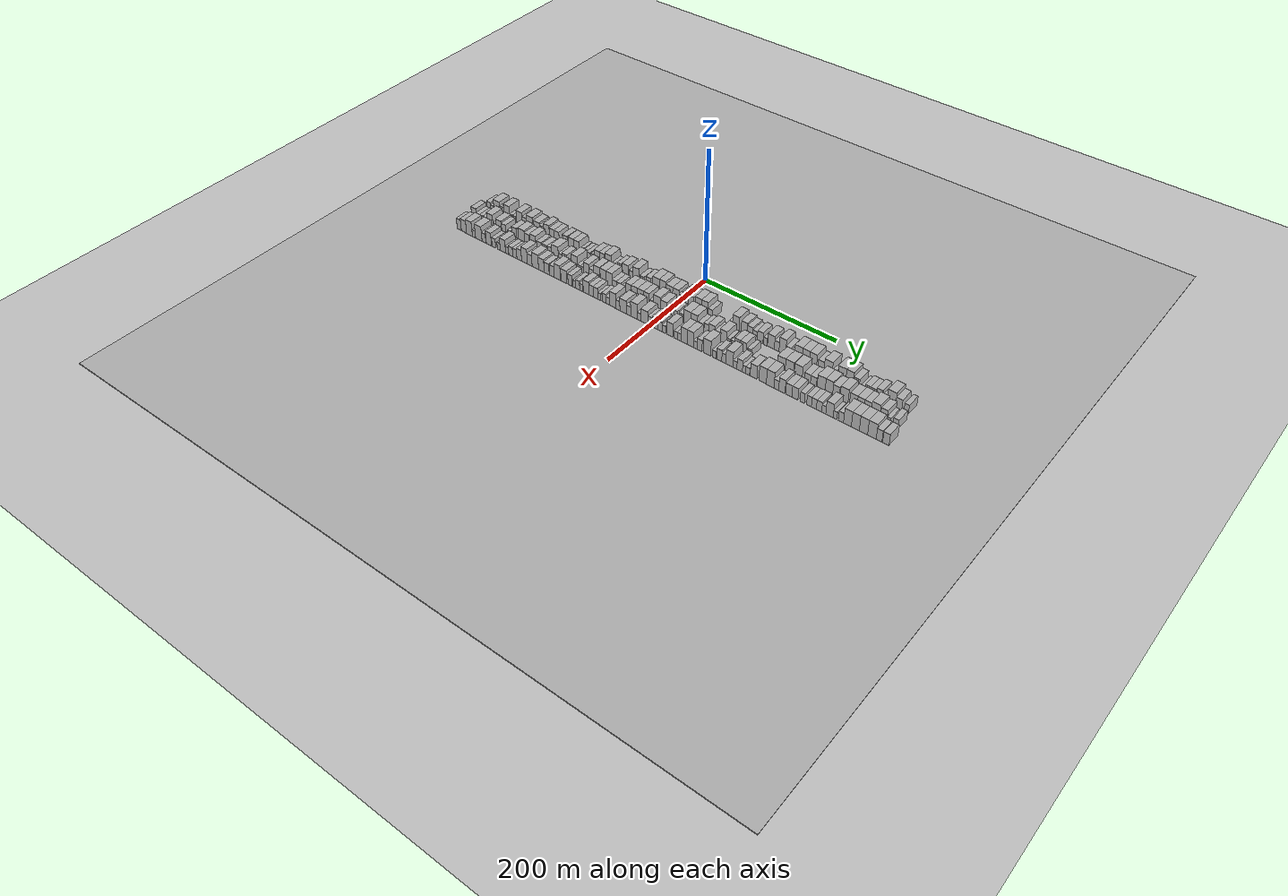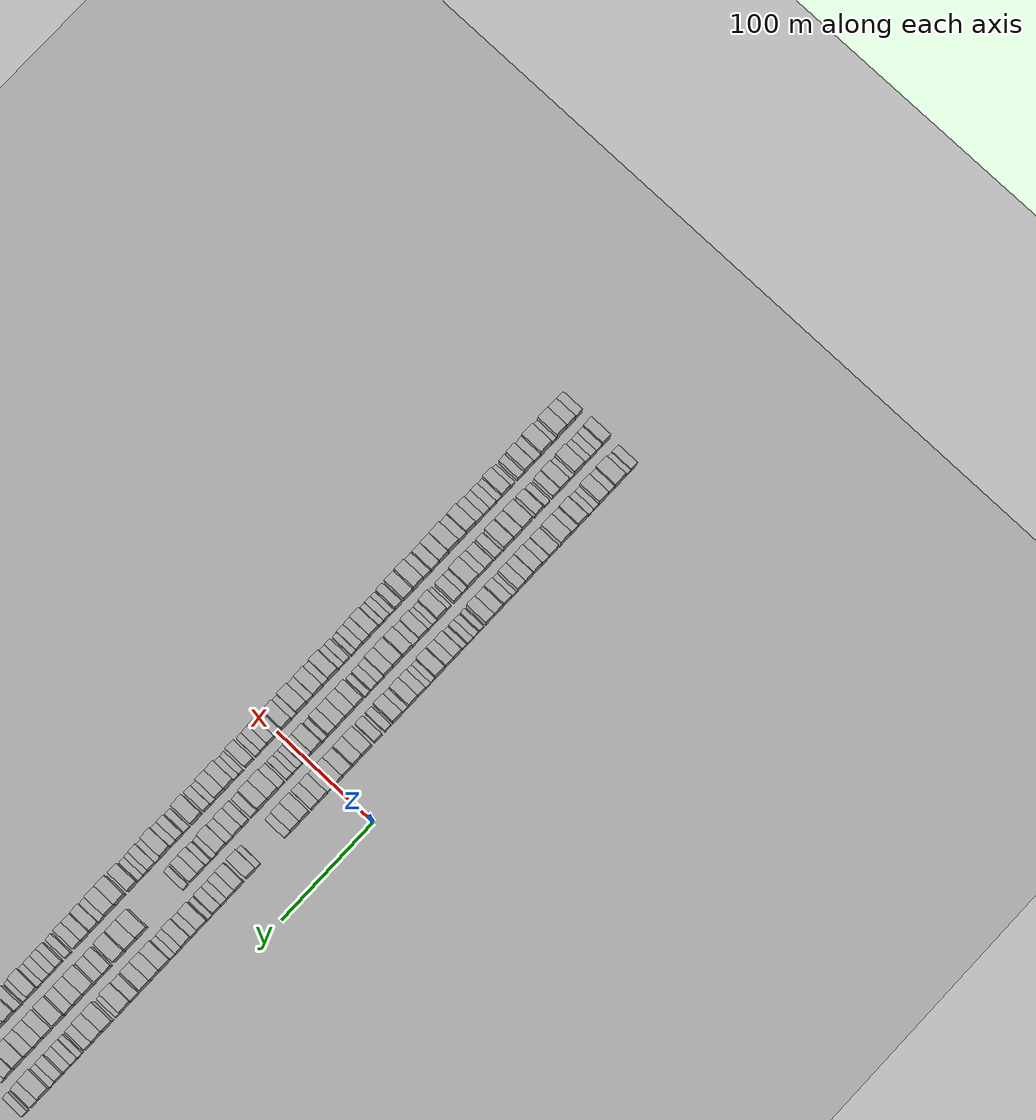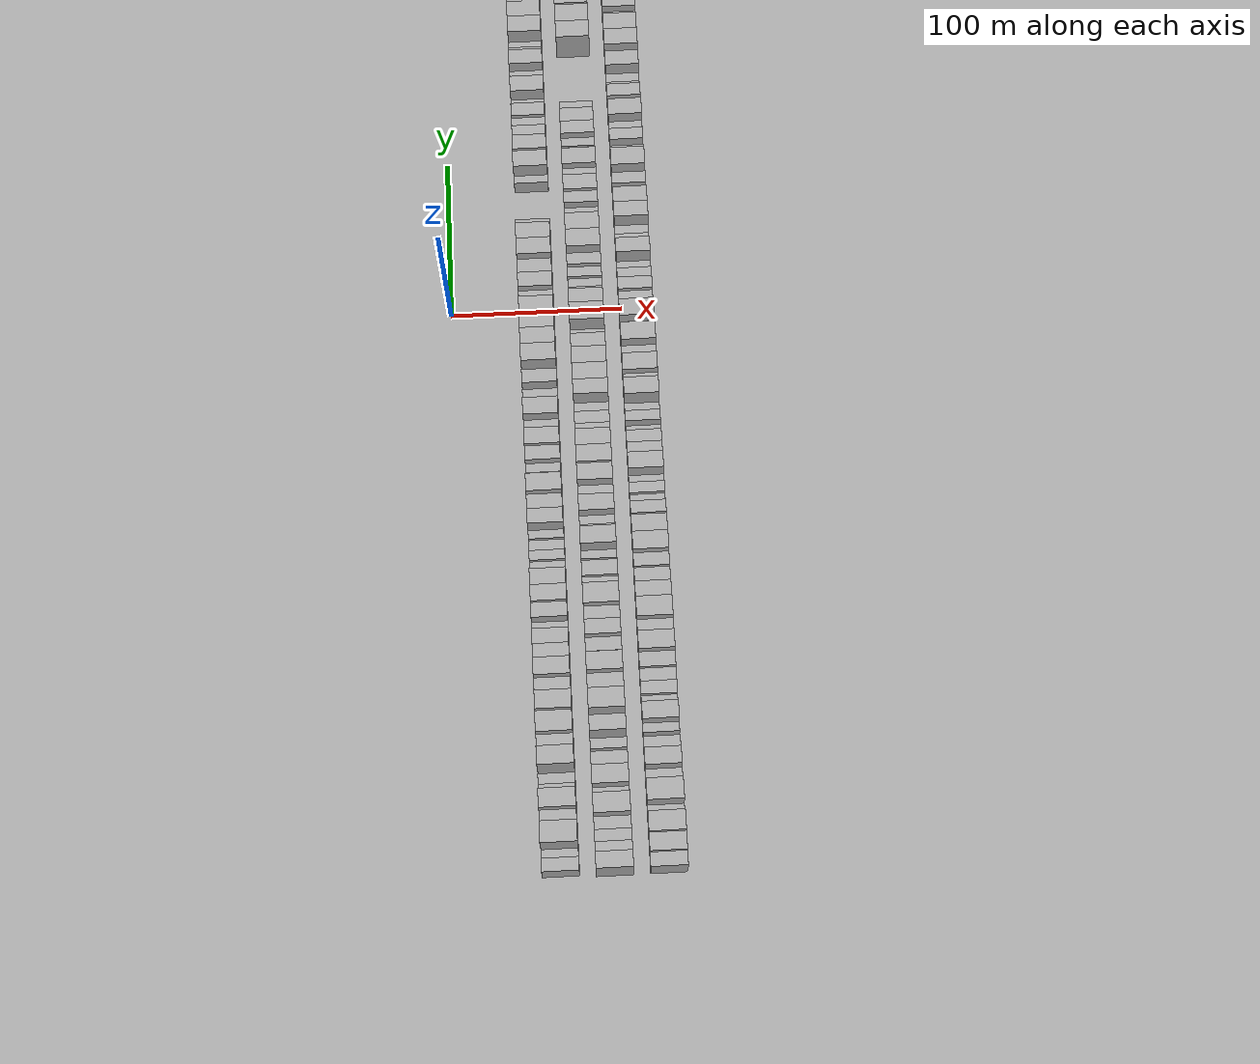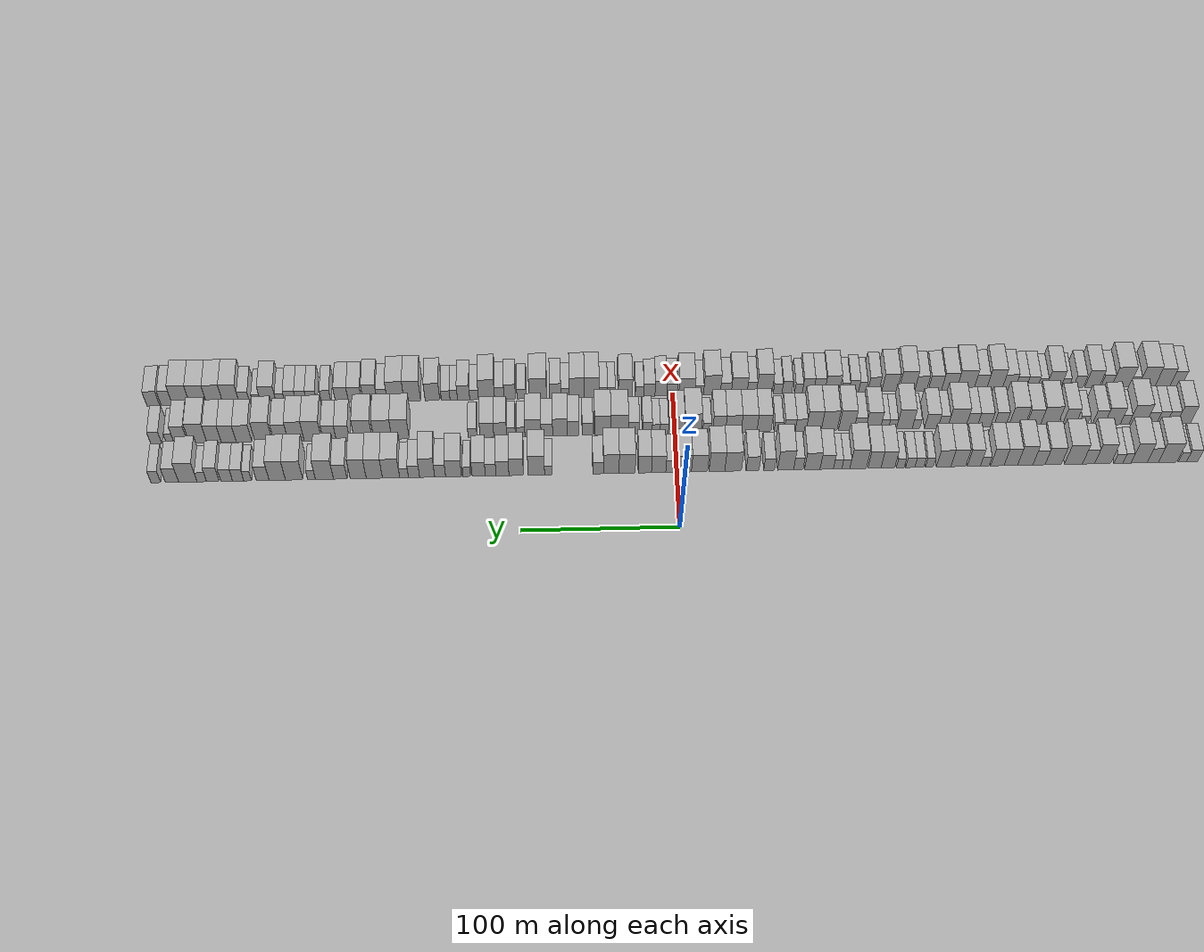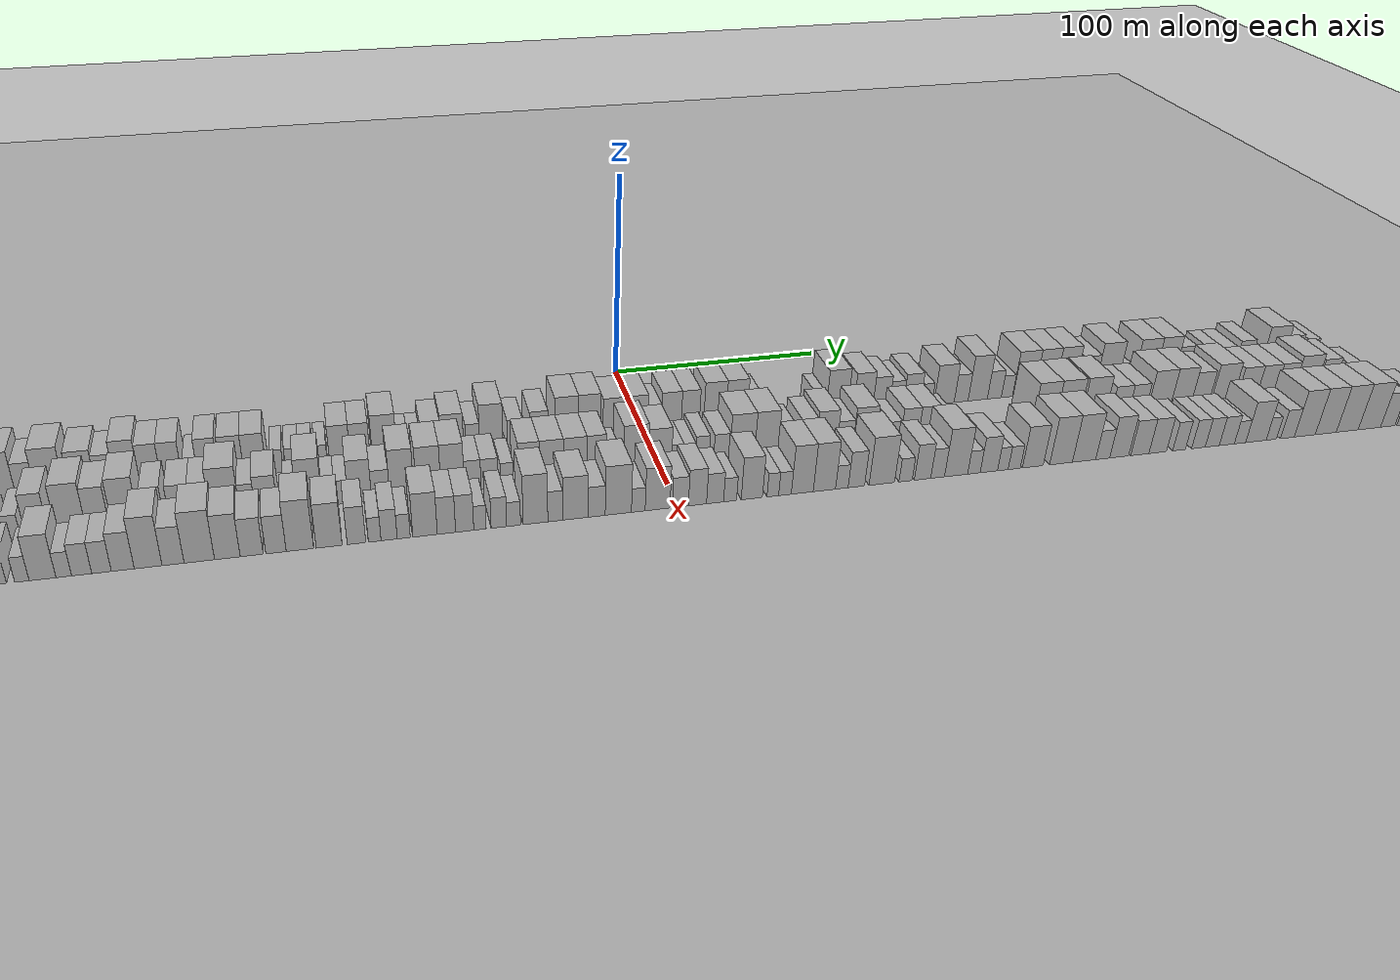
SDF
<?xml version="1.0" encoding="utf-8"?>

<sdf version="1.6">

   <world name="default">

      <gui fullscreen="0">

         <camera name="user_camera">

            <pose>-15 0 4.57585 0 0 0</pose>

            <view_controller>orbit</view_controller>

         </camera>

      </gui>

      <scene>

         <sky>

           <clouds>

             <speed>12</speed>

           </clouds>

         </sky>

         <ambient>0.4 0.4 0.4 1</ambient>

         <background>0.7 0.7 0.7 1</background>

         <shadows>1</shadows>

      </scene>

      <gravity>0 0 -9.8066</gravity>

      <magnetic_field>6e-06 2.3e-05 -4.2e-05</magnetic_field>

      <physics default="0" name="default_physics" type="ode">

         <ode>

            <solver>

               <type>quick</type>

               <iters>10</iters>

               <sor>1.0</sor>

               <use_dynamic_moi_rescaling>0</use_dynamic_moi_rescaling>

            </solver>

            <constraints>

               <cfm>0</cfm>

               <erp>0.2</erp>

               <contact_max_correcting_vel>100</contact_max_correcting_vel>

               <contact_surface_layer>0.001</contact_surface_layer>

            </constraints>

         </ode>

         <max_step_size>0.004</max_step_size>

         <real_time_factor>1</real_time_factor>

         <real_time_update_rate>250</real_time_update_rate>

      </physics>

      <light name="sun" type="directional">

         <cast_shadows>1</cast_shadows>

         <pose>0 0 10 0 0 0</pose>

         <diffuse>0.8 0.8 0.8 1</diffuse>

         <specular>0.2 0.2 0.2 1</specular>

         <attenuation>

            <range>1000</range>

            <constant>0.9</constant>

            <linear>0.01</linear>

            <quadratic>0.001</quadratic>

         </attenuation>

         <direction>-0.5 0.1 -0.9</direction>

      </light>

      <include>

         <name>ground_plane_1</name>

         <uri>model://HANNAS_ground_plane</uri>

         <pose>0 0 0  0 0 0</pose>

      </include>

      <include>

         <name>ground_plane_2</name>

         <uri>model://HANNAS_ground_plane</uri>

         <pose>100 0 0  0 0 0</pose>

      </include>

      <model name="building_1">

         <static>1</static>

         <pose frame="">50.0000 -331.3403 0 0.000000 0.000000 0.000000</pose>

         <link name="link">

            <pose frame="">0 0 7.50 0 0 0</pose>

            <collision name="collision">

               <geometry>

                  <box>

                     <size>20.0000 7.3194 15.0000</size>

                  </box>

               </geometry>

               <max_contacts>10</max_contacts>

               <surface>

                  <contact>

                     <ode/>

                  </contact>

                  <bounce/>

                  <friction>

                     <torsional>

                        <ode/>

                     </torsional>

                     <ode/>

                  </friction>

               </surface>

            </collision>

            <visual name="visual">

               <cast_shadows>0</cast_shadows>

               <geometry>

                  <box>

                     <size>20.0000 7.3194 15.0000</size>

                  </box>

               </geometry>

               <material>

                  <script>

                     <uri>model://HANNAS_wall/materials/scripts</uri>

                     <uri>model://HANNAS_wall/materials/textures</uri>

                     <name>vrc/HANNAS_wall</name>

                  </script>

               </material>

            </visual>

            <self_collide>0</self_collide>

            <enable_wind>0</enable_wind>

            <kinematic>0</kinematic>

         </link>

      </model>

      <model name="building_2">

         <static>1</static>

         <pose frame="">50.0000 -325.0429 0 0.000000 0.000000 0.000000</pose>

         <link name="link">

            <pose frame="">0 0 6.00 0 0 0</pose>

            <collision name="collision">

               <geometry>

                  <box>

                     <size>20.0000 5.2755 12.0000</size>

                  </box>

               </geometry>

               <max_contacts>10</max_contacts>

               <surface>

                  <contact>

                     <ode/>

                  </contact>

                  <bounce/>

                  <friction>

                     <torsional>

                        <ode/>

                     </torsional>

                     <ode/>

                  </friction>

               </surface>

            </collision>

            <visual name="visual">

               <cast_shadows>0</cast_shadows>

               <geometry>

                  <box>

                     <size>20.0000 5.2755 12.0000</size>

                  </box>

               </geometry>

               <material>

                  <script>

                     <uri>model://HANNAS_wall/materials/scripts</uri>

                     <uri>model://HANNAS_wall/materials/textures</uri>

                     <name>vrc/HANNAS_wall</name>

                  </script>

               </material>

            </visual>

            <self_collide>0</self_collide>

            <enable_wind>0</enable_wind>

            <kinematic>0</kinematic>

         </link>

      </model>

      <model name="building_3">

         <static>1</static>

         <pose frame="">50.0000 -315.4715 0 0.000000 0.000000 0.000000</pose>

         <link name="link">

            <pose frame="">0 0 12.00 0 0 0</pose>

            <collision name="collision">

               <geometry>

                  <box>

                     <size>20.0000 11.8673 24.0000</size>

                  </box>

               </geometry>

               <max_contacts>10</max_contacts>

               <surface>

                  <contact>

                     <ode/>

                  </contact>

                  <bounce/>

                  <friction>

                     <torsional>

                        <ode/>

                     </torsional>

                     <ode/>

                  </friction>

               </surface>

            </collision>

            <visual name="visual">

               <cast_shadows>0</cast_shadows>

               <geometry>

                  <box>

                     <size>20.0000 11.8673 24.0000</size>

                  </box>

               </geometry>

               <material>

                  <script>

                     <uri>model://HANNAS_wall/materials/scripts</uri>

                     <uri>model://HANNAS_wall/materials/textures</uri>

                     <name>vrc/HANNAS_wall</name>

                  </script>

               </material>

            </visual>

            <self_collide>0</self_collide>

            <enable_wind>0</enable_wind>

            <kinematic>0</kinematic>

         </link>

      </model>

      <model name="building_4">

         <static>1</static>

         <pose frame="">50.0000 -305.9180 0 0.000000 0.000000 0.000000</pose>

         <link name="link">

            <pose frame="">0 0 9.00 0 0 0</pose>

            <collision name="collision">

               <geometry>

                  <box>

                     <size>20.0000 7.2396 18.0000</size>

                  </box>

               </geometry>

               <max_contacts>10</max_contacts>

               <surface>

                  <contact>

                     <ode/>

                  </contact>

                  <bounce/>

                  <friction>

                     <torsional>

                        <ode/>

                     </torsional>

                     <ode/>

                  </friction>

               </surface>

            </collision>

            <visual name="visual">

               <cast_shadows>0</cast_shadows>

               <geometry>

                  <box>

                     <size>20.0000 7.2396 18.0000</size>

                  </box>

               </geometry>

               <material>

                  <script>

                     <uri>model://HANNAS_wall/materials/scripts</uri>

                     <uri>model://HANNAS_wall/materials/textures</uri>

                     <name>vrc/HANNAS_wall</name>

                  </script>

               </material>

            </visual>

            <self_collide>0</self_collide>

            <enable_wind>0</enable_wind>

            <kinematic>0</kinematic>

         </link>

      </model>

      <model name="building_5">

         <static>1</static>

         <pose frame="">50.0000 -297.0563 0 0.000000 0.000000 0.000000</pose>

         <link name="link">

            <pose frame="">0 0 12.00 0 0 0</pose>

            <collision name="collision">

               <geometry>

                  <box>

                     <size>20.0000 10.4839 24.0000</size>

                  </box>

               </geometry>

               <max_contacts>10</max_contacts>

               <surface>

                  <contact>

                     <ode/>

                  </contact>

                  <bounce/>

                  <friction>

                     <torsional>

                        <ode/>

                     </torsional>

                     <ode/>

                  </friction>

               </surface>

            </collision>

            <visual name="visual">

               <cast_shadows>0</cast_shadows>

               <geometry>

                  <box>

                     <size>20.0000 10.4839 24.0000</size>

                  </box>

               </geometry>

               <material>

                  <script>

                     <uri>model://HANNAS_wall/materials/scripts</uri>

                     <uri>model://HANNAS_wall/materials/textures</uri>

                     <name>vrc/HANNAS_wall</name>

                  </script>

               </material>

            </visual>

            <self_collide>0</self_collide>

            <enable_wind>0</enable_wind>

            <kinematic>0</kinematic>

         </link>

      </model>

      <model name="building_6">

         <static>1</static>

         <pose frame="">50.0000 -289.2177 0 0.000000 0.000000 0.000000</pose>

         <link name="link">

            <pose frame="">0 0 6.00 0 0 0</pose>

            <collision name="collision">

               <geometry>

                  <box>

                     <size>20.0000 5.1933 12.0000</size>

                  </box>

               </geometry>

               <max_contacts>10</max_contacts>

               <surface>

                  <contact>

                     <ode/>

                  </contact>

                  <bounce/>

                  <friction>

                     <torsional>

                        <ode/>

                     </torsional>

                     <ode/>

                  </friction>

               </surface>

            </collision>

            <visual name="visual">

               <cast_shadows>0</cast_shadows>

               <geometry>

                  <box>

                     <size>20.0000 5.1933 12.0000</size>

                  </box>

               </geometry>

               <material>

                  <script>

                     <uri>model://HANNAS_wall/materials/scripts</uri>

                     <uri>model://HANNAS_wall/materials/textures</uri>

                     <name>vrc/HANNAS_wall</name>

                  </script>

               </material>

            </visual>

            <self_collide>0</self_collide>

            <enable_wind>0</enable_wind>

            <kinematic>0</kinematic>

         </link>

      </model>

      <model name="building_7">

         <static>1</static>

         <pose frame="">50.0000 -283.7349 0 0.000000 0.000000 0.000000</pose>

         <link name="link">

            <pose frame="">0 0 6.00 0 0 0</pose>

            <collision name="collision">

               <geometry>

                  <box>

                     <size>20.0000 5.7723 12.0000</size>

                  </box>

               </geometry>

               <max_contacts>10</max_contacts>

               <surface>

                  <contact>

                     <ode/>

                  </contact>

                  <bounce/>

                  <friction>

                     <torsional>

                        <ode/>

                     </torsional>

                     <ode/>

                  </friction>

               </surface>

            </collision>

            <visual name="visual">

               <cast_shadows>0</cast_shadows>

               <geometry>

                  <box>

                     <size>20.0000 5.7723 12.0000</size>

                  </box>

               </geometry>

               <material>

                  <script>

                     <uri>model://HANNAS_wall/materials/scripts</uri>

                     <uri>model://HANNAS_wall/materials/textures</uri>

                     <name>vrc/HANNAS_wall</name>

                  </script>

               </material>

            </visual>

            <self_collide>0</self_collide>

            <enable_wind>0</enable_wind>

            <kinematic>0</kinematic>

         </link>

      </model>

      <model name="building_8">

         <static>1</static>

         <pose frame="">50.0000 -273.6569 0 0.000000 0.000000 0.000000</pose>

         <link name="link">

            <pose frame="">0 0 12.00 0 0 0</pose>

            <collision name="collision">

               <geometry>

                  <box>

                     <size>20.0000 10.3836 24.0000</size>

                  </box>

               </geometry>

               <max_contacts>10</max_contacts>

               <surface>

                  <contact>

                     <ode/>

                  </contact>

                  <bounce/>

                  <friction>

                     <torsional>

                        <ode/>

                     </torsional>

                     <ode/>

                  </friction>

               </surface>

            </collision>

            <visual name="visual">

               <cast_shadows>0</cast_shadows>

               <geometry>

                  <box>

                     <size>20.0000 10.3836 24.0000</size>

                  </box>

               </geometry>

               <material>

                  <script>

                     <uri>model://HANNAS_wall/materials/scripts</uri>

                     <uri>model://HANNAS_wall/materials/textures</uri>

                     <name>vrc/HANNAS_wall</name>

                  </script>

               </material>

            </visual>

            <self_collide>0</self_collide>

            <enable_wind>0</enable_wind>

            <kinematic>0</kinematic>

         </link>

      </model>

      <model name="building_9">

         <static>1</static>

         <pose frame="">50.0000 -264.5502 0 0.000000 0.000000 0.000000</pose>

         <link name="link">

            <pose frame="">0 0 9.00 0 0 0</pose>

            <collision name="collision">

               <geometry>

                  <box>

                     <size>20.0000 7.8298 18.0000</size>

                  </box>

               </geometry>

               <max_contacts>10</max_contacts>

               <surface>

                  <contact>

                     <ode/>

                  </contact>

                  <bounce/>

                  <friction>

                     <torsional>

                        <ode/>

                     </torsional>

                     <ode/>

                  </friction>

               </surface>

            </collision>

            <visual name="visual">

               <cast_shadows>0</cast_shadows>

               <geometry>

                  <box>

                     <size>20.0000 7.8298 18.0000</size>

                  </box>

               </geometry>

               <material>

                  <script>

                     <uri>model://HANNAS_wall/materials/scripts</uri>

                     <uri>model://HANNAS_wall/materials/textures</uri>

                     <name>vrc/HANNAS_wall</name>

                  </script>

               </material>

            </visual>

            <self_collide>0</self_collide>

            <enable_wind>0</enable_wind>

            <kinematic>0</kinematic>

         </link>

      </model>

      <model name="building_10">

         <static>1</static>

         <pose frame="">50.0000 -254.8177 0 0.000000 0.000000 0.000000</pose>

         <link name="link">

            <pose frame="">0 0 12.00 0 0 0</pose>

            <collision name="collision">

               <geometry>

                  <box>

                     <size>20.0000 11.6353 24.0000</size>

                  </box>

               </geometry>

               <max_contacts>10</max_contacts>

               <surface>

                  <contact>

                     <ode/>

                  </contact>

                  <bounce/>

                  <friction>

                     <torsional>

                        <ode/>

                     </torsional>

                     <ode/>

                  </friction>

               </surface>

            </collision>

            <visual name="visual">

               <cast_shadows>0</cast_shadows>

               <geometry>

                  <box>

                     <size>20.0000 11.6353 24.0000</size>

                  </box>

               </geometry>

               <material>

                  <script>

                     <uri>model://HANNAS_wall/materials/scripts</uri>

                     <uri>model://HANNAS_wall/materials/textures</uri>

                     <name>vrc/HANNAS_wall</name>

                  </script>

               </material>

            </visual>

            <self_collide>0</self_collide>

            <enable_wind>0</enable_wind>

            <kinematic>0</kinematic>

         </link>

      </model>

      <model name="building_11">

         <static>1</static>

         <pose frame="">50.0000 -241.7757 0 0.000000 0.000000 0.000000</pose>

         <link name="link">

            <pose frame="">0 0 10.50 0 0 0</pose>

            <collision name="collision">

               <geometry>

                  <box>

                     <size>20.0000 10.4486 21.0000</size>

                  </box>

               </geometry>

               <max_contacts>10</max_contacts>

               <surface>

                  <contact>

                     <ode/>

                  </contact>

                  <bounce/>

                  <friction>

                     <torsional>

                        <ode/>

                     </torsional>

                     <ode/>

                  </friction>

               </surface>

            </collision>

            <visual name="visual">

               <cast_shadows>0</cast_shadows>

               <geometry>

                  <box>

                     <size>20.0000 10.4486 21.0000</size>

                  </box>

               </geometry>

               <material>

                  <script>

                     <uri>model://HANNAS_wall/materials/scripts</uri>

                     <uri>model://HANNAS_wall/materials/textures</uri>

                     <name>vrc/HANNAS_wall</name>

                  </script>

               </material>

            </visual>

            <self_collide>0</self_collide>

            <enable_wind>0</enable_wind>

            <kinematic>0</kinematic>

         </link>

      </model>

      <model name="building_12">

         <static>1</static>

         <pose frame="">50.0000 -232.6239 0 0.000000 0.000000 0.000000</pose>

         <link name="link">

            <pose frame="">0 0 9.00 0 0 0</pose>

            <collision name="collision">

               <geometry>

                  <box>

                     <size>20.0000 7.8550 18.0000</size>

                  </box>

               </geometry>

               <max_contacts>10</max_contacts>

               <surface>

                  <contact>

                     <ode/>

                  </contact>

                  <bounce/>

                  <friction>

                     <torsional>

                        <ode/>

                     </torsional>

                     <ode/>

                  </friction>

               </surface>

            </collision>

            <visual name="visual">

               <cast_shadows>0</cast_shadows>

               <geometry>

                  <box>

                     <size>20.0000 7.8550 18.0000</size>

                  </box>

               </geometry>

               <material>

                  <script>

                     <uri>model://HANNAS_wall/materials/scripts</uri>

                     <uri>model://HANNAS_wall/materials/textures</uri>

                     <name>vrc/HANNAS_wall</name>

                  </script>

               </material>

            </visual>

            <self_collide>0</self_collide>

            <enable_wind>0</enable_wind>

            <kinematic>0</kinematic>

         </link>

      </model>

      <model name="building_13">

         <static>1</static>

         <pose frame="">50.0000 -223.7505 0 0.000000 0.000000 0.000000</pose>

         <link name="link">

            <pose frame="">0 0 12.00 0 0 0</pose>

            <collision name="collision">

               <geometry>

                  <box>

                     <size>20.0000 9.8918 24.0000</size>

                  </box>

               </geometry>

               <max_contacts>10</max_contacts>

               <surface>

                  <contact>

                     <ode/>

                  </contact>

                  <bounce/>

                  <friction>

                     <torsional>

                        <ode/>

                     </torsional>

                     <ode/>

                  </friction>

               </surface>

            </collision>

            <visual name="visual">

               <cast_shadows>0</cast_shadows>

               <geometry>

                  <box>

                     <size>20.0000 9.8918 24.0000</size>

                  </box>

               </geometry>

               <material>

                  <script>

                     <uri>model://HANNAS_wall/materials/scripts</uri>

                     <uri>model://HANNAS_wall/materials/textures</uri>

                     <name>vrc/HANNAS_wall</name>

                  </script>

               </material>

            </visual>

            <self_collide>0</self_collide>

            <enable_wind>0</enable_wind>

            <kinematic>0</kinematic>

         </link>

      </model>

      <model name="building_14">

         <static>1</static>

         <pose frame="">50.0000 -214.4361 0 0.000000 0.000000 0.000000</pose>

         <link name="link">

            <pose frame="">0 0 10.50 0 0 0</pose>

            <collision name="collision">

               <geometry>

                  <box>

                     <size>20.0000 8.7371 21.0000</size>

                  </box>

               </geometry>

               <max_contacts>10</max_contacts>

               <surface>

                  <contact>

                     <ode/>

                  </contact>

                  <bounce/>

                  <friction>

                     <torsional>

                        <ode/>

                     </torsional>

                     <ode/>

                  </friction>

               </surface>

            </collision>

            <visual name="visual">

               <cast_shadows>0</cast_shadows>

               <geometry>

                  <box>

                     <size>20.0000 8.7371 21.0000</size>

                  </box>

               </geometry>

               <material>

                  <script>

                     <uri>model://HANNAS_wall/materials/scripts</uri>

                     <uri>model://HANNAS_wall/materials/textures</uri>

                     <name>vrc/HANNAS_wall</name>

                  </script>

               </material>

            </visual>

            <self_collide>0</self_collide>

            <enable_wind>0</enable_wind>

            <kinematic>0</kinematic>

         </link>

      </model>

      <model name="building_15">

         <static>1</static>

         <pose frame="">50.0000 -205.7272 0 0.000000 0.000000 0.000000</pose>

         <link name="link">

            <pose frame="">0 0 10.50 0 0 0</pose>

            <collision name="collision">

               <geometry>

                  <box>

                     <size>20.0000 8.6808 21.0000</size>

                  </box>

               </geometry>

               <max_contacts>10</max_contacts>

               <surface>

                  <contact>

                     <ode/>

                  </contact>

                  <bounce/>

                  <friction>

                     <torsional>

                        <ode/>

                     </torsional>

                     <ode/>

                  </friction>

               </surface>

            </collision>

            <visual name="visual">

               <cast_shadows>0</cast_shadows>

               <geometry>

                  <box>

                     <size>20.0000 8.6808 21.0000</size>

                  </box>

               </geometry>

               <material>

                  <script>

                     <uri>model://HANNAS_wall/materials/scripts</uri>

                     <uri>model://HANNAS_wall/materials/textures</uri>

                     <name>vrc/HANNAS_wall</name>

                  </script>

               </material>

            </visual>

            <self_collide>0</self_collide>

            <enable_wind>0</enable_wind>

            <kinematic>0</kinematic>

         </link>

      </model>

      <model name="building_16">

         <static>1</static>

         <pose frame="">50.0000 -197.6600 0 0.000000 0.000000 0.000000</pose>

         <link name="link">

            <pose frame="">0 0 6.00 0 0 0</pose>

            <collision name="collision">

               <geometry>

                  <box>

                     <size>20.0000 5.4535 12.0000</size>

                  </box>

               </geometry>

               <max_contacts>10</max_contacts>

               <surface>

                  <contact>

                     <ode/>

                  </contact>

                  <bounce/>

                  <friction>

                     <torsional>

                        <ode/>

                     </torsional>

                     <ode/>

                  </friction>

               </surface>

            </collision>

            <visual name="visual">

               <cast_shadows>0</cast_shadows>

               <geometry>

                  <box>

                     <size>20.0000 5.4535 12.0000</size>

                  </box>

               </geometry>

               <material>

                  <script>

                     <uri>model://HANNAS_wall/materials/scripts</uri>

                     <uri>model://HANNAS_wall/materials/textures</uri>

                     <name>vrc/HANNAS_wall</name>

                  </script>

               </material>

            </visual>

            <self_collide>0</self_collide>

            <enable_wind>0</enable_wind>

            <kinematic>0</kinematic>

         </link>

      </model>

      <model name="building_17">

         <static>1</static>

         <pose frame="">50.0000 -190.6445 0 0.000000 0.000000 0.000000</pose>

         <link name="link">

            <pose frame="">0 0 10.50 0 0 0</pose>

            <collision name="collision">

               <geometry>

                  <box>

                     <size>20.0000 8.5775 21.0000</size>

                  </box>

               </geometry>

               <max_contacts>10</max_contacts>

               <surface>

                  <contact>

                     <ode/>

                  </contact>

                  <bounce/>

                  <friction>

                     <torsional>

                        <ode/>

                     </torsional>

                     <ode/>

                  </friction>

               </surface>

            </collision>

            <visual name="visual">

               <cast_shadows>0</cast_shadows>

               <geometry>

                  <box>

                     <size>20.0000 8.5775 21.0000</size>

                  </box>

               </geometry>

               <material>

                  <script>

                     <uri>model://HANNAS_wall/materials/scripts</uri>

                     <uri>model://HANNAS_wall/materials/textures</uri>

                     <name>vrc/HANNAS_wall</name>

                  </script>

               </material>

            </visual>

            <self_collide>0</self_collide>

            <enable_wind>0</enable_wind>

            <kinematic>0</kinematic>

         </link>

      </model>

      <model name="building_18">

         <static>1</static>

         <pose frame="">50.0000 -180.6054 0 0.000000 0.000000 0.000000</pose>

         <link name="link">

            <pose frame="">0 0 10.50 0 0 0</pose>

            <collision name="collision">

               <geometry>

                  <box>

                     <size>20.0000 9.5007 21.0000</size>

                  </box>

               </geometry>

               <max_contacts>10</max_contacts>

               <surface>

                  <contact>

                     <ode/>

                  </contact>

                  <bounce/>

                  <friction>

                     <torsional>

                        <ode/>

                     </torsional>

                     <ode/>

                  </friction>

               </surface>

            </collision>

            <visual name="visual">

               <cast_shadows>0</cast_shadows>

               <geometry>

                  <box>

                     <size>20.0000 9.5007 21.0000</size>

                  </box>

               </geometry>

               <material>

                  <script>

                     <uri>model://HANNAS_wall/materials/scripts</uri>

                     <uri>model://HANNAS_wall/materials/textures</uri>

                     <name>vrc/HANNAS_wall</name>

                  </script>

               </material>

            </visual>

            <self_collide>0</self_collide>

            <enable_wind>0</enable_wind>

            <kinematic>0</kinematic>

         </link>

      </model>

      <model name="building_19">

         <static>1</static>

         <pose frame="">50.0000 -171.1676 0 0.000000 0.000000 0.000000</pose>

         <link name="link">

            <pose frame="">0 0 10.50 0 0 0</pose>

            <collision name="collision">

               <geometry>

                  <box>

                     <size>20.0000 9.3747 21.0000</size>

                  </box>

               </geometry>

               <max_contacts>10</max_contacts>

               <surface>

                  <contact>

                     <ode/>

                  </contact>

                  <bounce/>

                  <friction>

                     <torsional>

                        <ode/>

                     </torsional>

                     <ode/>

                  </friction>

               </surface>

            </collision>

            <visual name="visual">

               <cast_shadows>0</cast_shadows>

               <geometry>

                  <box>

                     <size>20.0000 9.3747 21.0000</size>

                  </box>

               </geometry>

               <material>

                  <script>

                     <uri>model://HANNAS_wall/materials/scripts</uri>

                     <uri>model://HANNAS_wall/materials/textures</uri>

                     <name>vrc/HANNAS_wall</name>

                  </script>

               </material>

            </visual>

            <self_collide>0</self_collide>

            <enable_wind>0</enable_wind>

            <kinematic>0</kinematic>

         </link>

      </model>

      <model name="building_20">

         <static>1</static>

         <pose frame="">50.0000 -161.9651 0 0.000000 0.000000 0.000000</pose>

         <link name="link">

            <pose frame="">0 0 6.00 0 0 0</pose>

            <collision name="collision">

               <geometry>

                  <box>

                     <size>20.0000 5.0303 12.0000</size>

                  </box>

               </geometry>

               <max_contacts>10</max_contacts>

               <surface>

                  <contact>

                     <ode/>

                  </contact>

                  <bounce/>

                  <friction>

                     <torsional>

                        <ode/>

                     </torsional>

                     <ode/>

                  </friction>

               </surface>

            </collision>

            <visual name="visual">

               <cast_shadows>0</cast_shadows>

               <geometry>

                  <box>

                     <size>20.0000 5.0303 12.0000</size>

                  </box>

               </geometry>

               <material>

                  <script>

                     <uri>model://HANNAS_wall/materials/scripts</uri>

                     <uri>model://HANNAS_wall/materials/textures</uri>

                     <name>vrc/HANNAS_wall</name>

                  </script>

               </material>

            </visual>

            <self_collide>0</self_collide>

            <enable_wind>0</enable_wind>

            <kinematic>0</kinematic>

         </link>

      </model>

      <model name="building_21">

         <static>1</static>

         <pose frame="">50.0000 -155.5312 0 0.000000 0.000000 0.000000</pose>

         <link name="link">

            <pose frame="">0 0 6.00 0 0 0</pose>

            <collision name="collision">

               <geometry>

                  <box>

                     <size>20.0000 5.8376 12.0000</size>

                  </box>

               </geometry>

               <max_contacts>10</max_contacts>

               <surface>

                  <contact>

                     <ode/>

                  </contact>

                  <bounce/>

                  <friction>

                     <torsional>

                        <ode/>

                     </torsional>

                     <ode/>

                  </friction>

               </surface>

            </collision>

            <visual name="visual">

               <cast_shadows>0</cast_shadows>

               <geometry>

                  <box>

                     <size>20.0000 5.8376 12.0000</size>

                  </box>

               </geometry>

               <material>

                  <script>

                     <uri>model://HANNAS_wall/materials/scripts</uri>

                     <uri>model://HANNAS_wall/materials/textures</uri>

                     <name>vrc/HANNAS_wall</name>

                  </script>

               </material>

            </visual>

            <self_collide>0</self_collide>

            <enable_wind>0</enable_wind>

            <kinematic>0</kinematic>

         </link>

      </model>

      <model name="building_22">

         <static>1</static>

         <pose frame="">50.0000 -149.6704 0 0.000000 0.000000 0.000000</pose>

         <link name="link">

            <pose frame="">0 0 6.00 0 0 0</pose>

            <collision name="collision">

               <geometry>

                  <box>

                     <size>20.0000 5.8840 12.0000</size>

                  </box>

               </geometry>

               <max_contacts>10</max_contacts>

               <surface>

                  <contact>

                     <ode/>

                  </contact>

                  <bounce/>

                  <friction>

                     <torsional>

                        <ode/>

                     </torsional>

                     <ode/>

                  </friction>

               </surface>

            </collision>

            <visual name="visual">

               <cast_shadows>0</cast_shadows>

               <geometry>

                  <box>

                     <size>20.0000 5.8840 12.0000</size>

                  </box>

               </geometry>

               <material>

                  <script>

                     <uri>model://HANNAS_wall/materials/scripts</uri>

                     <uri>model://HANNAS_wall/materials/textures</uri>

                     <name>vrc/HANNAS_wall</name>

                  </script>

               </material>

            </visual>

            <self_collide>0</self_collide>

            <enable_wind>0</enable_wind>

            <kinematic>0</kinematic>

         </link>

      </model>

      <model name="building_23">

         <static>1</static>

         <pose frame="">50.0000 -143.2097 0 0.000000 0.000000 0.000000</pose>

         <link name="link">

            <pose frame="">0 0 6.00 0 0 0</pose>

            <collision name="collision">

               <geometry>

                  <box>

                     <size>20.0000 5.0373 12.0000</size>

                  </box>

               </geometry>

               <max_contacts>10</max_contacts>

               <surface>

                  <contact>

                     <ode/>

                  </contact>

                  <bounce/>

                  <friction>

                     <torsional>

                        <ode/>

                     </torsional>

                     <ode/>

                  </friction>

               </surface>

            </collision>

            <visual name="visual">

               <cast_shadows>0</cast_shadows>

               <geometry>

                  <box>

                     <size>20.0000 5.0373 12.0000</size>

                  </box>

               </geometry>

               <material>

                  <script>

                     <uri>model://HANNAS_wall/materials/scripts</uri>

                     <uri>model://HANNAS_wall/materials/textures</uri>

                     <name>vrc/HANNAS_wall</name>

                  </script>

               </material>

            </visual>

            <self_collide>0</self_collide>

            <enable_wind>0</enable_wind>

            <kinematic>0</kinematic>

         </link>

      </model>

      <model name="building_24">

         <static>1</static>

         <pose frame="">50.0000 -135.2551 0 0.000000 0.000000 0.000000</pose>

         <link name="link">

            <pose frame="">0 0 10.50 0 0 0</pose>

            <collision name="collision">

               <geometry>

                  <box>

                     <size>20.0000 8.8719 21.0000</size>

                  </box>

               </geometry>

               <max_contacts>10</max_contacts>

               <surface>

                  <contact>

                     <ode/>

                  </contact>

                  <bounce/>

                  <friction>

                     <torsional>

                        <ode/>

                     </torsional>

                     <ode/>

                  </friction>

               </surface>

            </collision>

            <visual name="visual">

               <cast_shadows>0</cast_shadows>

               <geometry>

                  <box>

                     <size>20.0000 8.8719 21.0000</size>

                  </box>

               </geometry>

               <material>

                  <script>

                     <uri>model://HANNAS_wall/materials/scripts</uri>

                     <uri>model://HANNAS_wall/materials/textures</uri>

                     <name>vrc/HANNAS_wall</name>

                  </script>

               </material>

            </visual>

            <self_collide>0</self_collide>

            <enable_wind>0</enable_wind>

            <kinematic>0</kinematic>

         </link>

      </model>

      <model name="building_25">

         <static>1</static>

         <pose frame="">50.0000 -126.5977 0 0.000000 0.000000 0.000000</pose>

         <link name="link">

            <pose frame="">0 0 10.50 0 0 0</pose>

            <collision name="collision">

               <geometry>

                  <box>

                     <size>20.0000 8.4429 21.0000</size>

                  </box>

               </geometry>

               <max_contacts>10</max_contacts>

               <surface>

                  <contact>

                     <ode/>

                  </contact>

                  <bounce/>

                  <friction>

                     <torsional>

                        <ode/>

                     </torsional>

                     <ode/>

                  </friction>

               </surface>

            </collision>

            <visual name="visual">

               <cast_shadows>0</cast_shadows>

               <geometry>

                  <box>

                     <size>20.0000 8.4429 21.0000</size>

                  </box>

               </geometry>

               <material>

                  <script>

                     <uri>model://HANNAS_wall/materials/scripts</uri>

                     <uri>model://HANNAS_wall/materials/textures</uri>

                     <name>vrc/HANNAS_wall</name>

                  </script>

               </material>

            </visual>

            <self_collide>0</self_collide>

            <enable_wind>0</enable_wind>

            <kinematic>0</kinematic>

         </link>

      </model>

      <model name="building_26">

         <static>1</static>

         <pose frame="">50.0000 -116.0989 0 0.000000 0.000000 0.000000</pose>

         <link name="link">

            <pose frame="">0 0 12.00 0 0 0</pose>

            <collision name="collision">

               <geometry>

                  <box>

                     <size>20.0000 10.5547 24.0000</size>

                  </box>

               </geometry>

               <max_contacts>10</max_contacts>

               <surface>

                  <contact>

                     <ode/>

                  </contact>

                  <bounce/>

                  <friction>

                     <torsional>

                        <ode/>

                     </torsional>

                     <ode/>

                  </friction>

               </surface>

            </collision>

            <visual name="visual">

               <cast_shadows>0</cast_shadows>

               <geometry>

                  <box>

                     <size>20.0000 10.5547 24.0000</size>

                  </box>

               </geometry>

               <material>

                  <script>

                     <uri>model://HANNAS_wall/materials/scripts</uri>

                     <uri>model://HANNAS_wall/materials/textures</uri>

                     <name>vrc/HANNAS_wall</name>

                  </script>

               </material>

            </visual>

            <self_collide>0</self_collide>

            <enable_wind>0</enable_wind>

            <kinematic>0</kinematic>

         </link>

      </model>

      <model name="building_27">

         <static>1</static>

         <pose frame="">50.0000 -108.2517 0 0.000000 0.000000 0.000000</pose>

         <link name="link">

            <pose frame="">0 0 6.00 0 0 0</pose>

            <collision name="collision">

               <geometry>

                  <box>

                     <size>20.0000 5.1396 12.0000</size>

                  </box>

               </geometry>

               <max_contacts>10</max_contacts>

               <surface>

                  <contact>

                     <ode/>

                  </contact>

                  <bounce/>

                  <friction>

                     <torsional>

                        <ode/>

                     </torsional>

                     <ode/>

                  </friction>

               </surface>

            </collision>

            <visual name="visual">

               <cast_shadows>0</cast_shadows>

               <geometry>

                  <box>

                     <size>20.0000 5.1396 12.0000</size>

                  </box>

               </geometry>

               <material>

                  <script>

                     <uri>model://HANNAS_wall/materials/scripts</uri>

                     <uri>model://HANNAS_wall/materials/textures</uri>

                     <name>vrc/HANNAS_wall</name>

                  </script>

               </material>

            </visual>

            <self_collide>0</self_collide>

            <enable_wind>0</enable_wind>

            <kinematic>0</kinematic>

         </link>

      </model>

      <model name="building_28">

         <static>1</static>

         <pose frame="">50.0000 -102.9619 0 0.000000 0.000000 0.000000</pose>

         <link name="link">

            <pose frame="">0 0 6.00 0 0 0</pose>

            <collision name="collision">

               <geometry>

                  <box>

                     <size>20.0000 5.4400 12.0000</size>

                  </box>

               </geometry>

               <max_contacts>10</max_contacts>

               <surface>

                  <contact>

                     <ode/>

                  </contact>

                  <bounce/>

                  <friction>

                     <torsional>

                        <ode/>

                     </torsional>

                     <ode/>

                  </friction>

               </surface>

            </collision>

            <visual name="visual">

               <cast_shadows>0</cast_shadows>

               <geometry>

                  <box>

                     <size>20.0000 5.4400 12.0000</size>

                  </box>

               </geometry>

               <material>

                  <script>

                     <uri>model://HANNAS_wall/materials/scripts</uri>

                     <uri>model://HANNAS_wall/materials/textures</uri>

                     <name>vrc/HANNAS_wall</name>

                  </script>

               </material>

            </visual>

            <self_collide>0</self_collide>

            <enable_wind>0</enable_wind>

            <kinematic>0</kinematic>

         </link>

      </model>

      <model name="building_29">

         <static>1</static>

         <pose frame="">50.0000 -95.9530 0 0.000000 0.000000 0.000000</pose>

         <link name="link">

            <pose frame="">0 0 9.00 0 0 0</pose>

            <collision name="collision">

               <geometry>

                  <box>

                     <size>20.0000 8.5779 18.0000</size>

                  </box>

               </geometry>

               <max_contacts>10</max_contacts>

               <surface>

                  <contact>

                     <ode/>

                  </contact>

                  <bounce/>

                  <friction>

                     <torsional>

                        <ode/>

                     </torsional>

                     <ode/>

                  </friction>

               </surface>

            </collision>

            <visual name="visual">

               <cast_shadows>0</cast_shadows>

               <geometry>

                  <box>

                     <size>20.0000 8.5779 18.0000</size>

                  </box>

               </geometry>

               <material>

                  <script>

                     <uri>model://HANNAS_wall/materials/scripts</uri>

                     <uri>model://HANNAS_wall/materials/textures</uri>

                     <name>vrc/HANNAS_wall</name>

                  </script>

               </material>

            </visual>

            <self_collide>0</self_collide>

            <enable_wind>0</enable_wind>

            <kinematic>0</kinematic>

         </link>

      </model>

      <model name="building_30">

         <static>1</static>

         <pose frame="">50.0000 -86.7007 0 0.000000 0.000000 0.000000</pose>

         <link name="link">

            <pose frame="">0 0 10.50 0 0 0</pose>

            <collision name="collision">

               <geometry>

                  <box>

                     <size>20.0000 9.9268 21.0000</size>

                  </box>

               </geometry>

               <max_contacts>10</max_contacts>

               <surface>

                  <contact>

                     <ode/>

                  </contact>

                  <bounce/>

                  <friction>

                     <torsional>

                        <ode/>

                     </torsional>

                     <ode/>

                  </friction>

               </surface>

            </collision>

            <visual name="visual">

               <cast_shadows>0</cast_shadows>

               <geometry>

                  <box>

                     <size>20.0000 9.9268 21.0000</size>

                  </box>

               </geometry>

               <material>

                  <script>

                     <uri>model://HANNAS_wall/materials/scripts</uri>

                     <uri>model://HANNAS_wall/materials/textures</uri>

                     <name>vrc/HANNAS_wall</name>

                  </script>

               </material>

            </visual>

            <self_collide>0</self_collide>

            <enable_wind>0</enable_wind>

            <kinematic>0</kinematic>

         </link>

      </model>

      <model name="building_31">

         <static>1</static>

         <pose frame="">50.0000 -77.7047 0 0.000000 0.000000 0.000000</pose>

         <link name="link">

            <pose frame="">0 0 7.50 0 0 0</pose>

            <collision name="collision">

               <geometry>

                  <box>

                     <size>20.0000 6.0651 15.0000</size>

                  </box>

               </geometry>

               <max_contacts>10</max_contacts>

               <surface>

                  <contact>

                     <ode/>

                  </contact>

                  <bounce/>

                  <friction>

                     <torsional>

                        <ode/>

                     </torsional>

                     <ode/>

                  </friction>

               </surface>

            </collision>

            <visual name="visual">

               <cast_shadows>0</cast_shadows>

               <geometry>

                  <box>

                     <size>20.0000 6.0651 15.0000</size>

                  </box>

               </geometry>

               <material>

                  <script>

                     <uri>model://HANNAS_wall/materials/scripts</uri>

                     <uri>model://HANNAS_wall/materials/textures</uri>

                     <name>vrc/HANNAS_wall</name>

                  </script>

               </material>

            </visual>

            <self_collide>0</self_collide>

            <enable_wind>0</enable_wind>

            <kinematic>0</kinematic>

         </link>

      </model>

      <model name="building_32">

         <static>1</static>

         <pose frame="">50.0000 -69.5270 0 0.000000 0.000000 0.000000</pose>

         <link name="link">

            <pose frame="">0 0 12.00 0 0 0</pose>

            <collision name="collision">

               <geometry>

                  <box>

                     <size>20.0000 10.2904 24.0000</size>

                  </box>

               </geometry>

               <max_contacts>10</max_contacts>

               <surface>

                  <contact>

                     <ode/>

                  </contact>

                  <bounce/>

                  <friction>

                     <torsional>

                        <ode/>

                     </torsional>

                     <ode/>

                  </friction>

               </surface>

            </collision>

            <visual name="visual">

               <cast_shadows>0</cast_shadows>

               <geometry>

                  <box>

                     <size>20.0000 10.2904 24.0000</size>

                  </box>

               </geometry>

               <material>

                  <script>

                     <uri>model://HANNAS_wall/materials/scripts</uri>

                     <uri>model://HANNAS_wall/materials/textures</uri>

                     <name>vrc/HANNAS_wall</name>

                  </script>

               </material>

            </visual>

            <self_collide>0</self_collide>

            <enable_wind>0</enable_wind>

            <kinematic>0</kinematic>

         </link>

      </model>

      <model name="building_33">

         <static>1</static>

         <pose frame="">50.0000 -58.9242 0 0.000000 0.000000 0.000000</pose>

         <link name="link">

            <pose frame="">0 0 7.50 0 0 0</pose>

            <collision name="collision">

               <geometry>

                  <box>

                     <size>20.0000 6.9151 15.0000</size>

                  </box>

               </geometry>

               <max_contacts>10</max_contacts>

               <surface>

                  <contact>

                     <ode/>

                  </contact>

                  <bounce/>

                  <friction>

                     <torsional>

                        <ode/>

                     </torsional>

                     <ode/>

                  </friction>

               </surface>

            </collision>

            <visual name="visual">

               <cast_shadows>0</cast_shadows>

               <geometry>

                  <box>

                     <size>20.0000 6.9151 15.0000</size>

                  </box>

               </geometry>

               <material>

                  <script>

                     <uri>model://HANNAS_wall/materials/scripts</uri>

                     <uri>model://HANNAS_wall/materials/textures</uri>

                     <name>vrc/HANNAS_wall</name>

                  </script>

               </material>

            </visual>

            <self_collide>0</self_collide>

            <enable_wind>0</enable_wind>

            <kinematic>0</kinematic>

         </link>

      </model>

      <model name="building_34">

         <static>1</static>

         <pose frame="">50.0000 -48.3323 0 0.000000 0.000000 0.000000</pose>

         <link name="link">

            <pose frame="">0 0 9.00 0 0 0</pose>

            <collision name="collision">

               <geometry>

                  <box>

                     <size>20.0000 8.2686 18.0000</size>

                  </box>

               </geometry>

               <max_contacts>10</max_contacts>

               <surface>

                  <contact>

                     <ode/>

                  </contact>

                  <bounce/>

                  <friction>

                     <torsional>

                        <ode/>

                     </torsional>

                     <ode/>

                  </friction>

               </surface>

            </collision>

            <visual name="visual">

               <cast_shadows>0</cast_shadows>

               <geometry>

                  <box>

                     <size>20.0000 8.2686 18.0000</size>

                  </box>

               </geometry>

               <material>

                  <script>

                     <uri>model://HANNAS_wall/materials/scripts</uri>

                     <uri>model://HANNAS_wall/materials/textures</uri>

                     <name>vrc/HANNAS_wall</name>

                  </script>

               </material>

            </visual>

            <self_collide>0</self_collide>

            <enable_wind>0</enable_wind>

            <kinematic>0</kinematic>

         </link>

      </model>

      <model name="building_35">

         <static>1</static>

         <pose frame="">50.0000 -35.8312 0 0.000000 0.000000 0.000000</pose>

         <link name="link">

            <pose frame="">0 0 12.00 0 0 0</pose>

            <collision name="collision">

               <geometry>

                  <box>

                     <size>20.0000 10.7336 24.0000</size>

                  </box>

               </geometry>

               <max_contacts>10</max_contacts>

               <surface>

                  <contact>

                     <ode/>

                  </contact>

                  <bounce/>

                  <friction>

                     <torsional>

                        <ode/>

                     </torsional>

                     <ode/>

                  </friction>

               </surface>

            </collision>

            <visual name="visual">

               <cast_shadows>0</cast_shadows>

               <geometry>

                  <box>

                     <size>20.0000 10.7336 24.0000</size>

                  </box>

               </geometry>

               <material>

                  <script>

                     <uri>model://HANNAS_wall/materials/scripts</uri>

                     <uri>model://HANNAS_wall/materials/textures</uri>

                     <name>vrc/HANNAS_wall</name>

                  </script>

               </material>

            </visual>

            <self_collide>0</self_collide>

            <enable_wind>0</enable_wind>

            <kinematic>0</kinematic>

         </link>

      </model>

      <model name="building_36">

         <static>1</static>

         <pose frame="">50.0000 -25.4489 0 0.000000 0.000000 0.000000</pose>

         <link name="link">

            <pose frame="">0 0 12.00 0 0 0</pose>

            <collision name="collision">

               <geometry>

                  <box>

                     <size>20.0000 10.0312 24.0000</size>

                  </box>

               </geometry>

               <max_contacts>10</max_contacts>

               <surface>

                  <contact>

                     <ode/>

                  </contact>

                  <bounce/>

                  <friction>

                     <torsional>

                        <ode/>

                     </torsional>

                     <ode/>

                  </friction>

               </surface>

            </collision>

            <visual name="visual">

               <cast_shadows>0</cast_shadows>

               <geometry>

                  <box>

                     <size>20.0000 10.0312 24.0000</size>

                  </box>

               </geometry>

               <material>

                  <script>

                     <uri>model://HANNAS_wall/materials/scripts</uri>

                     <uri>model://HANNAS_wall/materials/textures</uri>

                     <name>vrc/HANNAS_wall</name>

                  </script>

               </material>

            </visual>

            <self_collide>0</self_collide>

            <enable_wind>0</enable_wind>

            <kinematic>0</kinematic>

         </link>

      </model>

      <model name="building_37">

         <static>1</static>

         <pose frame="">50.0000 -14.2747 0 0.000000 0.000000 0.000000</pose>

         <link name="link">

            <pose frame="">0 0 10.50 0 0 0</pose>

            <collision name="collision">

               <geometry>

                  <box>

                     <size>20.0000 10.3172 21.0000</size>

                  </box>

               </geometry>

               <max_contacts>10</max_contacts>

               <surface>

                  <contact>

                     <ode/>

                  </contact>

                  <bounce/>

                  <friction>

                     <torsional>

                        <ode/>

                     </torsional>

                     <ode/>

                  </friction>

               </surface>

            </collision>

            <visual name="visual">

               <cast_shadows>0</cast_shadows>

               <geometry>

                  <box>

                     <size>20.0000 10.3172 21.0000</size>

                  </box>

               </geometry>

               <material>

                  <script>

                     <uri>model://HANNAS_wall/materials/scripts</uri>

                     <uri>model://HANNAS_wall/materials/textures</uri>

                     <name>vrc/HANNAS_wall</name>

                  </script>

               </material>

            </visual>

            <self_collide>0</self_collide>

            <enable_wind>0</enable_wind>

            <kinematic>0</kinematic>

         </link>

      </model>

      <model name="building_38">

         <static>1</static>

         <pose frame="">50.0000 -4.0690 0 0.000000 0.000000 0.000000</pose>

         <link name="link">

            <pose frame="">0 0 10.50 0 0 0</pose>

            <collision name="collision">

               <geometry>

                  <box>

                     <size>20.0000 10.0940 21.0000</size>

                  </box>

               </geometry>

               <max_contacts>10</max_contacts>

               <surface>

                  <contact>

                     <ode/>

                  </contact>

                  <bounce/>

                  <friction>

                     <torsional>

                        <ode/>

                     </torsional>

                     <ode/>

                  </friction>

               </surface>

            </collision>

            <visual name="visual">

               <cast_shadows>0</cast_shadows>

               <geometry>

                  <box>

                     <size>20.0000 10.0940 21.0000</size>

                  </box>

               </geometry>

               <material>

                  <script>

                     <uri>model://HANNAS_wall/materials/scripts</uri>

                     <uri>model://HANNAS_wall/materials/textures</uri>

                     <name>vrc/HANNAS_wall</name>

                  </script>

               </material>

            </visual>

            <self_collide>0</self_collide>

            <enable_wind>0</enable_wind>

            <kinematic>0</kinematic>

         </link>

      </model>

      <model name="building_39">

         <static>1</static>

         <pose frame="">50.0000 4.1592 0 0.000000 0.000000 0.000000</pose>

         <link name="link">

            <pose frame="">0 0 7.50 0 0 0</pose>

            <collision name="collision">

               <geometry>

                  <box>

                     <size>20.0000 6.3625 15.0000</size>

                  </box>

               </geometry>

               <max_contacts>10</max_contacts>

               <surface>

                  <contact>

                     <ode/>

                  </contact>

                  <bounce/>

                  <friction>

                     <torsional>

                        <ode/>

                     </torsional>

                     <ode/>

                  </friction>

               </surface>

            </collision>

            <visual name="visual">

               <cast_shadows>0</cast_shadows>

               <geometry>

                  <box>

                     <size>20.0000 6.3625 15.0000</size>

                  </box>

               </geometry>

               <material>

                  <script>

                     <uri>model://HANNAS_wall/materials/scripts</uri>

                     <uri>model://HANNAS_wall/materials/textures</uri>

                     <name>vrc/HANNAS_wall</name>

                  </script>

               </material>

            </visual>

            <self_collide>0</self_collide>

            <enable_wind>0</enable_wind>

            <kinematic>0</kinematic>

         </link>

      </model>

      <model name="building_40">

         <static>1</static>

         <pose frame="">50.0000 11.9197 0 0.000000 0.000000 0.000000</pose>

         <link name="link">

            <pose frame="">0 0 10.50 0 0 0</pose>

            <collision name="collision">

               <geometry>

                  <box>

                     <size>20.0000 9.1584 21.0000</size>

                  </box>

               </geometry>

               <max_contacts>10</max_contacts>

               <surface>

                  <contact>

                     <ode/>

                  </contact>

                  <bounce/>

                  <friction>

                     <torsional>

                        <ode/>

                     </torsional>

                     <ode/>

                  </friction>

               </surface>

            </collision>

            <visual name="visual">

               <cast_shadows>0</cast_shadows>

               <geometry>

                  <box>

                     <size>20.0000 9.1584 21.0000</size>

                  </box>

               </geometry>

               <material>

                  <script>

                     <uri>model://HANNAS_wall/materials/scripts</uri>

                     <uri>model://HANNAS_wall/materials/textures</uri>

                     <name>vrc/HANNAS_wall</name>

                  </script>

               </material>

            </visual>

            <self_collide>0</self_collide>

            <enable_wind>0</enable_wind>

            <kinematic>0</kinematic>

         </link>

      </model>

      <model name="building_41">

         <static>1</static>

         <pose frame="">50.0000 20.7276 0 0.000000 0.000000 0.000000</pose>

         <link name="link">

            <pose frame="">0 0 10.50 0 0 0</pose>

            <collision name="collision">

               <geometry>

                  <box>

                     <size>20.0000 8.4575 21.0000</size>

                  </box>

               </geometry>

               <max_contacts>10</max_contacts>

               <surface>

                  <contact>

                     <ode/>

                  </contact>

                  <bounce/>

                  <friction>

                     <torsional>

                        <ode/>

                     </torsional>

                     <ode/>

                  </friction>

               </surface>

            </collision>

            <visual name="visual">

               <cast_shadows>0</cast_shadows>

               <geometry>

                  <box>

                     <size>20.0000 8.4575 21.0000</size>

                  </box>

               </geometry>

               <material>

                  <script>

                     <uri>model://HANNAS_wall/materials/scripts</uri>

                     <uri>model://HANNAS_wall/materials/textures</uri>

                     <name>vrc/HANNAS_wall</name>

                  </script>

               </material>

            </visual>

            <self_collide>0</self_collide>

            <enable_wind>0</enable_wind>

            <kinematic>0</kinematic>

         </link>

      </model>

      <model name="building_42">

         <static>1</static>

         <pose frame="">50.0000 32.1395 0 0.000000 0.000000 0.000000</pose>

         <link name="link">

            <pose frame="">0 0 12.00 0 0 0</pose>

            <collision name="collision">

               <geometry>

                  <box>

                     <size>20.0000 10.3663 24.0000</size>

                  </box>

               </geometry>

               <max_contacts>10</max_contacts>

               <surface>

                  <contact>

                     <ode/>

                  </contact>

                  <bounce/>

                  <friction>

                     <torsional>

                        <ode/>

                     </torsional>

                     <ode/>

                  </friction>

               </surface>

            </collision>

            <visual name="visual">

               <cast_shadows>0</cast_shadows>

               <geometry>

                  <box>

                     <size>20.0000 10.3663 24.0000</size>

                  </box>

               </geometry>

               <material>

                  <script>

                     <uri>model://HANNAS_wall/materials/scripts</uri>

                     <uri>model://HANNAS_wall/materials/textures</uri>

                     <name>vrc/HANNAS_wall</name>

                  </script>

               </material>

            </visual>

            <self_collide>0</self_collide>

            <enable_wind>0</enable_wind>

            <kinematic>0</kinematic>

         </link>

      </model>

      <model name="building_43">

         <static>1</static>

         <pose frame="">50.0000 42.3265 0 0.000000 0.000000 0.000000</pose>

         <link name="link">

            <pose frame="">0 0 12.00 0 0 0</pose>

            <collision name="collision">

               <geometry>

                  <box>

                     <size>20.0000 10.0076 24.0000</size>

                  </box>

               </geometry>

               <max_contacts>10</max_contacts>

               <surface>

                  <contact>

                     <ode/>

                  </contact>

                  <bounce/>

                  <friction>

                     <torsional>

                        <ode/>

                     </torsional>

                     <ode/>

                  </friction>

               </surface>

            </collision>

            <visual name="visual">

               <cast_shadows>0</cast_shadows>

               <geometry>

                  <box>

                     <size>20.0000 10.0076 24.0000</size>

                  </box>

               </geometry>

               <material>

                  <script>

                     <uri>model://HANNAS_wall/materials/scripts</uri>

                     <uri>model://HANNAS_wall/materials/textures</uri>

                     <name>vrc/HANNAS_wall</name>

                  </script>

               </material>

            </visual>

            <self_collide>0</self_collide>

            <enable_wind>0</enable_wind>

            <kinematic>0</kinematic>

         </link>

      </model>

      <model name="building_44">

         <static>1</static>

         <pose frame="">50.0000 50.7054 0 0.000000 0.000000 0.000000</pose>

         <link name="link">

            <pose frame="">0 0 7.50 0 0 0</pose>

            <collision name="collision">

               <geometry>

                  <box>

                     <size>20.0000 6.7502 15.0000</size>

                  </box>

               </geometry>

               <max_contacts>10</max_contacts>

               <surface>

                  <contact>

                     <ode/>

                  </contact>

                  <bounce/>

                  <friction>

                     <torsional>

                        <ode/>

                     </torsional>

                     <ode/>

                  </friction>

               </surface>

            </collision>

            <visual name="visual">

               <cast_shadows>0</cast_shadows>

               <geometry>

                  <box>

                     <size>20.0000 6.7502 15.0000</size>

                  </box>

               </geometry>

               <material>

                  <script>

                     <uri>model://HANNAS_wall/materials/scripts</uri>

                     <uri>model://HANNAS_wall/materials/textures</uri>

                     <name>vrc/HANNAS_wall</name>

                  </script>

               </material>

            </visual>

            <self_collide>0</self_collide>

            <enable_wind>0</enable_wind>

            <kinematic>0</kinematic>

         </link>

      </model>

      <model name="building_45">

         <static>1</static>

         <pose frame="">50.0000 82.4860 0 0.000000 0.000000 0.000000</pose>

         <link name="link">

            <pose frame="">0 0 6.00 0 0 0</pose>

            <collision name="collision">

               <geometry>

                  <box>

                     <size>20.0000 4.9370 12.0000</size>

                  </box>

               </geometry>

               <max_contacts>10</max_contacts>

               <surface>

                  <contact>

                     <ode/>

                  </contact>

                  <bounce/>

                  <friction>

                     <torsional>

                        <ode/>

                     </torsional>

                     <ode/>

                  </friction>

               </surface>

            </collision>

            <visual name="visual">

               <cast_shadows>0</cast_shadows>

               <geometry>

                  <box>

                     <size>20.0000 4.9370 12.0000</size>

                  </box>

               </geometry>

               <material>

                  <script>

                     <uri>model://HANNAS_wall/materials/scripts</uri>

                     <uri>model://HANNAS_wall/materials/textures</uri>

                     <name>vrc/HANNAS_wall</name>

                  </script>

               </material>

            </visual>

            <self_collide>0</self_collide>

            <enable_wind>0</enable_wind>

            <kinematic>0</kinematic>

         </link>

      </model>

      <model name="building_46">

         <static>1</static>

         <pose frame="">50.0000 90.1778 0 0.000000 0.000000 0.000000</pose>

         <link name="link">

            <pose frame="">0 0 12.00 0 0 0</pose>

            <collision name="collision">

               <geometry>

                  <box>

                     <size>20.0000 10.4464 24.0000</size>

                  </box>

               </geometry>

               <max_contacts>10</max_contacts>

               <surface>

                  <contact>

                     <ode/>

                  </contact>

                  <bounce/>

                  <friction>

                     <torsional>

                        <ode/>

                     </torsional>

                     <ode/>

                  </friction>

               </surface>

            </collision>

            <visual name="visual">

               <cast_shadows>0</cast_shadows>

               <geometry>

                  <box>

                     <size>20.0000 10.4464 24.0000</size>

                  </box>

               </geometry>

               <material>

                  <script>

                     <uri>model://HANNAS_wall/materials/scripts</uri>

                     <uri>model://HANNAS_wall/materials/textures</uri>

                     <name>vrc/HANNAS_wall</name>

                  </script>

               </material>

            </visual>

            <self_collide>0</self_collide>

            <enable_wind>0</enable_wind>

            <kinematic>0</kinematic>

         </link>

      </model>

      <model name="building_47">

         <static>1</static>

         <pose frame="">50.0000 103.0657 0 0.000000 0.000000 0.000000</pose>

         <link name="link">

            <pose frame="">0 0 10.50 0 0 0</pose>

            <collision name="collision">

               <geometry>

                  <box>

                     <size>20.0000 9.3296 21.0000</size>

                  </box>

               </geometry>

               <max_contacts>10</max_contacts>

               <surface>

                  <contact>

                     <ode/>

                  </contact>

                  <bounce/>

                  <friction>

                     <torsional>

                        <ode/>

                     </torsional>

                     <ode/>

                  </friction>

               </surface>

            </collision>

            <visual name="visual">

               <cast_shadows>0</cast_shadows>

               <geometry>

                  <box>

                     <size>20.0000 9.3296 21.0000</size>

                  </box>

               </geometry>

               <material>

                  <script>

                     <uri>model://HANNAS_wall/materials/scripts</uri>

                     <uri>model://HANNAS_wall/materials/textures</uri>

                     <name>vrc/HANNAS_wall</name>

                  </script>

               </material>

            </visual>

            <self_collide>0</self_collide>

            <enable_wind>0</enable_wind>

            <kinematic>0</kinematic>

         </link>

      </model>

      <model name="building_48">

         <static>1</static>

         <pose frame="">50.0000 111.8211 0 0.000000 0.000000 0.000000</pose>

         <link name="link">

            <pose frame="">0 0 9.00 0 0 0</pose>

            <collision name="collision">

               <geometry>

                  <box>

                     <size>20.0000 8.1811 18.0000</size>

                  </box>

               </geometry>

               <max_contacts>10</max_contacts>

               <surface>

                  <contact>

                     <ode/>

                  </contact>

                  <bounce/>

                  <friction>

                     <torsional>

                        <ode/>

                     </torsional>

                     <ode/>

                  </friction>

               </surface>

            </collision>

            <visual name="visual">

               <cast_shadows>0</cast_shadows>

               <geometry>

                  <box>

                     <size>20.0000 8.1811 18.0000</size>

                  </box>

               </geometry>

               <material>

                  <script>

                     <uri>model://HANNAS_wall/materials/scripts</uri>

                     <uri>model://HANNAS_wall/materials/textures</uri>

                     <name>vrc/HANNAS_wall</name>

                  </script>

               </material>

            </visual>

            <self_collide>0</self_collide>

            <enable_wind>0</enable_wind>

            <kinematic>0</kinematic>

         </link>

      </model>

      <model name="building_49">

         <static>1</static>

         <pose frame="">50.0000 119.3543 0 0.000000 0.000000 0.000000</pose>

         <link name="link">

            <pose frame="">0 0 7.50 0 0 0</pose>

            <collision name="collision">

               <geometry>

                  <box>

                     <size>20.0000 6.8853 15.0000</size>

                  </box>

               </geometry>

               <max_contacts>10</max_contacts>

               <surface>

                  <contact>

                     <ode/>

                  </contact>

                  <bounce/>

                  <friction>

                     <torsional>

                        <ode/>

                     </torsional>

                     <ode/>

                  </friction>

               </surface>

            </collision>

            <visual name="visual">

               <cast_shadows>0</cast_shadows>

               <geometry>

                  <box>

                     <size>20.0000 6.8853 15.0000</size>

                  </box>

               </geometry>

               <material>

                  <script>

                     <uri>model://HANNAS_wall/materials/scripts</uri>

                     <uri>model://HANNAS_wall/materials/textures</uri>

                     <name>vrc/HANNAS_wall</name>

                  </script>

               </material>

            </visual>

            <self_collide>0</self_collide>

            <enable_wind>0</enable_wind>

            <kinematic>0</kinematic>

         </link>

      </model>

      <model name="building_50">

         <static>1</static>

         <pose frame="">50.0000 127.0319 0 0.000000 0.000000 0.000000</pose>

         <link name="link">

            <pose frame="">0 0 9.00 0 0 0</pose>

            <collision name="collision">

               <geometry>

                  <box>

                     <size>20.0000 8.4700 18.0000</size>

                  </box>

               </geometry>

               <max_contacts>10</max_contacts>

               <surface>

                  <contact>

                     <ode/>

                  </contact>

                  <bounce/>

                  <friction>

                     <torsional>

                        <ode/>

                     </torsional>

                     <ode/>

                  </friction>

               </surface>

            </collision>

            <visual name="visual">

               <cast_shadows>0</cast_shadows>

               <geometry>

                  <box>

                     <size>20.0000 8.4700 18.0000</size>

                  </box>

               </geometry>

               <material>

                  <script>

                     <uri>model://HANNAS_wall/materials/scripts</uri>

                     <uri>model://HANNAS_wall/materials/textures</uri>

                     <name>vrc/HANNAS_wall</name>

                  </script>

               </material>

            </visual>

            <self_collide>0</self_collide>

            <enable_wind>0</enable_wind>

            <kinematic>0</kinematic>

         </link>

      </model>

      <model name="building_51">

         <static>1</static>

         <pose frame="">50.0000 134.6706 0 0.000000 0.000000 0.000000</pose>

         <link name="link">

            <pose frame="">0 0 6.00 0 0 0</pose>

            <collision name="collision">

               <geometry>

                  <box>

                     <size>20.0000 4.8075 12.0000</size>

                  </box>

               </geometry>

               <max_contacts>10</max_contacts>

               <surface>

                  <contact>

                     <ode/>

                  </contact>

                  <bounce/>

                  <friction>

                     <torsional>

                        <ode/>

                     </torsional>

                     <ode/>

                  </friction>

               </surface>

            </collision>

            <visual name="visual">

               <cast_shadows>0</cast_shadows>

               <geometry>

                  <box>

                     <size>20.0000 4.8075 12.0000</size>

                  </box>

               </geometry>

               <material>

                  <script>

                     <uri>model://HANNAS_wall/materials/scripts</uri>

                     <uri>model://HANNAS_wall/materials/textures</uri>

                     <name>vrc/HANNAS_wall</name>

                  </script>

               </material>

            </visual>

            <self_collide>0</self_collide>

            <enable_wind>0</enable_wind>

            <kinematic>0</kinematic>

         </link>

      </model>

      <model name="building_52">

         <static>1</static>

         <pose frame="">50.0000 143.1510 0 0.000000 0.000000 0.000000</pose>

         <link name="link">

            <pose frame="">0 0 10.50 0 0 0</pose>

            <collision name="collision">

               <geometry>

                  <box>

                     <size>20.0000 10.1533 21.0000</size>

                  </box>

               </geometry>

               <max_contacts>10</max_contacts>

               <surface>

                  <contact>

                     <ode/>

                  </contact>

                  <bounce/>

                  <friction>

                     <torsional>

                        <ode/>

                     </torsional>

                     <ode/>

                  </friction>

               </surface>

            </collision>

            <visual name="visual">

               <cast_shadows>0</cast_shadows>

               <geometry>

                  <box>

                     <size>20.0000 10.1533 21.0000</size>

                  </box>

               </geometry>

               <material>

                  <script>

                     <uri>model://HANNAS_wall/materials/scripts</uri>

                     <uri>model://HANNAS_wall/materials/textures</uri>

                     <name>vrc/HANNAS_wall</name>

                  </script>

               </material>

            </visual>

            <self_collide>0</self_collide>

            <enable_wind>0</enable_wind>

            <kinematic>0</kinematic>

         </link>

      </model>

      <model name="building_53">

         <static>1</static>

         <pose frame="">50.0000 151.7000 0 0.000000 0.000000 0.000000</pose>

         <link name="link">

            <pose frame="">0 0 7.50 0 0 0</pose>

            <collision name="collision">

               <geometry>

                  <box>

                     <size>20.0000 6.9446 15.0000</size>

                  </box>

               </geometry>

               <max_contacts>10</max_contacts>

               <surface>

                  <contact>

                     <ode/>

                  </contact>

                  <bounce/>

                  <friction>

                     <torsional>

                        <ode/>

                     </torsional>

                     <ode/>

                  </friction>

               </surface>

            </collision>

            <visual name="visual">

               <cast_shadows>0</cast_shadows>

               <geometry>

                  <box>

                     <size>20.0000 6.9446 15.0000</size>

                  </box>

               </geometry>

               <material>

                  <script>

                     <uri>model://HANNAS_wall/materials/scripts</uri>

                     <uri>model://HANNAS_wall/materials/textures</uri>

                     <name>vrc/HANNAS_wall</name>

                  </script>

               </material>

            </visual>

            <self_collide>0</self_collide>

            <enable_wind>0</enable_wind>

            <kinematic>0</kinematic>

         </link>

      </model>

      <model name="building_54">

         <static>1</static>

         <pose frame="">50.0000 160.0127 0 0.000000 0.000000 0.000000</pose>

         <link name="link">

            <pose frame="">0 0 12.00 0 0 0</pose>

            <collision name="collision">

               <geometry>

                  <box>

                     <size>20.0000 9.6808 24.0000</size>

                  </box>

               </geometry>

               <max_contacts>10</max_contacts>

               <surface>

                  <contact>

                     <ode/>

                  </contact>

                  <bounce/>

                  <friction>

                     <torsional>

                        <ode/>

                     </torsional>

                     <ode/>

                  </friction>

               </surface>

            </collision>

            <visual name="visual">

               <cast_shadows>0</cast_shadows>

               <geometry>

                  <box>

                     <size>20.0000 9.6808 24.0000</size>

                  </box>

               </geometry>

               <material>

                  <script>

                     <uri>model://HANNAS_wall/materials/scripts</uri>

                     <uri>model://HANNAS_wall/materials/textures</uri>

                     <name>vrc/HANNAS_wall</name>

                  </script>

               </material>

            </visual>

            <self_collide>0</self_collide>

            <enable_wind>0</enable_wind>

            <kinematic>0</kinematic>

         </link>

      </model>

      <model name="building_55">

         <static>1</static>

         <pose frame="">50.0000 168.3861 0 0.000000 0.000000 0.000000</pose>

         <link name="link">

            <pose frame="">0 0 7.50 0 0 0</pose>

            <collision name="collision">

               <geometry>

                  <box>

                     <size>20.0000 7.0662 15.0000</size>

                  </box>

               </geometry>

               <max_contacts>10</max_contacts>

               <surface>

                  <contact>

                     <ode/>

                  </contact>

                  <bounce/>

                  <friction>

                     <torsional>

                        <ode/>

                     </torsional>

                     <ode/>

                  </friction>

               </surface>

            </collision>

            <visual name="visual">

               <cast_shadows>0</cast_shadows>

               <geometry>

                  <box>

                     <size>20.0000 7.0662 15.0000</size>

                  </box>

               </geometry>

               <material>

                  <script>

                     <uri>model://HANNAS_wall/materials/scripts</uri>

                     <uri>model://HANNAS_wall/materials/textures</uri>

                     <name>vrc/HANNAS_wall</name>

                  </script>

               </material>

            </visual>

            <self_collide>0</self_collide>

            <enable_wind>0</enable_wind>

            <kinematic>0</kinematic>

         </link>

      </model>

      <model name="building_56">

         <static>1</static>

         <pose frame="">50.0000 174.7349 0 0.000000 0.000000 0.000000</pose>

         <link name="link">

            <pose frame="">0 0 6.00 0 0 0</pose>

            <collision name="collision">

               <geometry>

                  <box>

                     <size>20.0000 5.6313 12.0000</size>

                  </box>

               </geometry>

               <max_contacts>10</max_contacts>

               <surface>

                  <contact>

                     <ode/>

                  </contact>

                  <bounce/>

                  <friction>

                     <torsional>

                        <ode/>

                     </torsional>

                     <ode/>

                  </friction>

               </surface>

            </collision>

            <visual name="visual">

               <cast_shadows>0</cast_shadows>

               <geometry>

                  <box>

                     <size>20.0000 5.6313 12.0000</size>

                  </box>

               </geometry>

               <material>

                  <script>

                     <uri>model://HANNAS_wall/materials/scripts</uri>

                     <uri>model://HANNAS_wall/materials/textures</uri>

                     <name>vrc/HANNAS_wall</name>

                  </script>

               </material>

            </visual>

            <self_collide>0</self_collide>

            <enable_wind>0</enable_wind>

            <kinematic>0</kinematic>

         </link>

      </model>

      <model name="building_57">

         <static>1</static>

         <pose frame="">50.0000 183.0591 0 0.000000 0.000000 0.000000</pose>

         <link name="link">

            <pose frame="">0 0 12.00 0 0 0</pose>

            <collision name="collision">

               <geometry>

                  <box>

                     <size>20.0000 11.0171 24.0000</size>

                  </box>

               </geometry>

               <max_contacts>10</max_contacts>

               <surface>

                  <contact>

                     <ode/>

                  </contact>

                  <bounce/>

                  <friction>

                     <torsional>

                        <ode/>

                     </torsional>

                     <ode/>

                  </friction>

               </surface>

            </collision>

            <visual name="visual">

               <cast_shadows>0</cast_shadows>

               <geometry>

                  <box>

                     <size>20.0000 11.0171 24.0000</size>

                  </box>

               </geometry>

               <material>

                  <script>

                     <uri>model://HANNAS_wall/materials/scripts</uri>

                     <uri>model://HANNAS_wall/materials/textures</uri>

                     <name>vrc/HANNAS_wall</name>

                  </script>

               </material>

            </visual>

            <self_collide>0</self_collide>

            <enable_wind>0</enable_wind>

            <kinematic>0</kinematic>

         </link>

      </model>

      <model name="building_58">

         <static>1</static>

         <pose frame="">50.0000 193.7491 0 0.000000 0.000000 0.000000</pose>

         <link name="link">

            <pose frame="">0 0 12.00 0 0 0</pose>

            <collision name="collision">

               <geometry>

                  <box>

                     <size>20.0000 10.3629 24.0000</size>

                  </box>

               </geometry>

               <max_contacts>10</max_contacts>

               <surface>

                  <contact>

                     <ode/>

                  </contact>

                  <bounce/>

                  <friction>

                     <torsional>

                        <ode/>

                     </torsional>

                     <ode/>

                  </friction>

               </surface>

            </collision>

            <visual name="visual">

               <cast_shadows>0</cast_shadows>

               <geometry>

                  <box>

                     <size>20.0000 10.3629 24.0000</size>

                  </box>

               </geometry>

               <material>

                  <script>

                     <uri>model://HANNAS_wall/materials/scripts</uri>

                     <uri>model://HANNAS_wall/materials/textures</uri>

                     <name>vrc/HANNAS_wall</name>

                  </script>

               </material>

            </visual>

            <self_collide>0</self_collide>

            <enable_wind>0</enable_wind>

            <kinematic>0</kinematic>

         </link>

      </model>

      <model name="building_59">

         <static>1</static>

         <pose frame="">50.0000 204.0609 0 0.000000 0.000000 0.000000</pose>

         <link name="link">

            <pose frame="">0 0 12.00 0 0 0</pose>

            <collision name="collision">

               <geometry>

                  <box>

                     <size>20.0000 10.2606 24.0000</size>

                  </box>

               </geometry>

               <max_contacts>10</max_contacts>

               <surface>

                  <contact>

                     <ode/>

                  </contact>

                  <bounce/>

                  <friction>

                     <torsional>

                        <ode/>

                     </torsional>

                     <ode/>

                  </friction>

               </surface>

            </collision>

            <visual name="visual">

               <cast_shadows>0</cast_shadows>

               <geometry>

                  <box>

                     <size>20.0000 10.2606 24.0000</size>

                  </box>

               </geometry>

               <material>

                  <script>

                     <uri>model://HANNAS_wall/materials/scripts</uri>

                     <uri>model://HANNAS_wall/materials/textures</uri>

                     <name>vrc/HANNAS_wall</name>

                  </script>

               </material>

            </visual>

            <self_collide>0</self_collide>

            <enable_wind>0</enable_wind>

            <kinematic>0</kinematic>

         </link>

      </model>

      <model name="building_60">

         <static>1</static>

         <pose frame="">50.0000 215.5393 0 0.000000 0.000000 0.000000</pose>

         <link name="link">

            <pose frame="">0 0 9.00 0 0 0</pose>

            <collision name="collision">

               <geometry>

                  <box>

                     <size>20.0000 8.6963 18.0000</size>

                  </box>

               </geometry>

               <max_contacts>10</max_contacts>

               <surface>

                  <contact>

                     <ode/>

                  </contact>

                  <bounce/>

                  <friction>

                     <torsional>

                        <ode/>

                     </torsional>

                     <ode/>

                  </friction>

               </surface>

            </collision>

            <visual name="visual">

               <cast_shadows>0</cast_shadows>

               <geometry>

                  <box>

                     <size>20.0000 8.6963 18.0000</size>

                  </box>

               </geometry>

               <material>

                  <script>

                     <uri>model://HANNAS_wall/materials/scripts</uri>

                     <uri>model://HANNAS_wall/materials/textures</uri>

                     <name>vrc/HANNAS_wall</name>

                  </script>

               </material>

            </visual>

            <self_collide>0</self_collide>

            <enable_wind>0</enable_wind>

            <kinematic>0</kinematic>

         </link>

      </model>

      <model name="building_61">

         <static>1</static>

         <pose frame="">50.0000 225.6269 0 0.000000 0.000000 0.000000</pose>

         <link name="link">

            <pose frame="">0 0 12.00 0 0 0</pose>

            <collision name="collision">

               <geometry>

                  <box>

                     <size>20.0000 11.4789 24.0000</size>

                  </box>

               </geometry>

               <max_contacts>10</max_contacts>

               <surface>

                  <contact>

                     <ode/>

                  </contact>

                  <bounce/>

                  <friction>

                     <torsional>

                        <ode/>

                     </torsional>

                     <ode/>

                  </friction>

               </surface>

            </collision>

            <visual name="visual">

               <cast_shadows>0</cast_shadows>

               <geometry>

                  <box>

                     <size>20.0000 11.4789 24.0000</size>

                  </box>

               </geometry>

               <material>

                  <script>

                     <uri>model://HANNAS_wall/materials/scripts</uri>

                     <uri>model://HANNAS_wall/materials/textures</uri>

                     <name>vrc/HANNAS_wall</name>

                  </script>

               </material>

            </visual>

            <self_collide>0</self_collide>

            <enable_wind>0</enable_wind>

            <kinematic>0</kinematic>

         </link>

      </model>

      <model name="building_62">

         <static>1</static>

         <pose frame="">50.0000 233.8528 0 0.000000 0.000000 0.000000</pose>

         <link name="link">

            <pose frame="">0 0 6.00 0 0 0</pose>

            <collision name="collision">

               <geometry>

                  <box>

                     <size>20.0000 4.9729 12.0000</size>

                  </box>

               </geometry>

               <max_contacts>10</max_contacts>

               <surface>

                  <contact>

                     <ode/>

                  </contact>

                  <bounce/>

                  <friction>

                     <torsional>

                        <ode/>

                     </torsional>

                     <ode/>

                  </friction>

               </surface>

            </collision>

            <visual name="visual">

               <cast_shadows>0</cast_shadows>

               <geometry>

                  <box>

                     <size>20.0000 4.9729 12.0000</size>

                  </box>

               </geometry>

               <material>

                  <script>

                     <uri>model://HANNAS_wall/materials/scripts</uri>

                     <uri>model://HANNAS_wall/materials/textures</uri>

                     <name>vrc/HANNAS_wall</name>

                  </script>

               </material>

            </visual>

            <self_collide>0</self_collide>

            <enable_wind>0</enable_wind>

            <kinematic>0</kinematic>

         </link>

      </model>

      <model name="building_63">

         <static>1</static>

         <pose frame="">50.0000 244.9158 0 0.000000 0.000000 0.000000</pose>

         <link name="link">

            <pose frame="">0 0 12.00 0 0 0</pose>

            <collision name="collision">

               <geometry>

                  <box>

                     <size>20.0000 11.1530 24.0000</size>

                  </box>

               </geometry>

               <max_contacts>10</max_contacts>

               <surface>

                  <contact>

                     <ode/>

                  </contact>

                  <bounce/>

                  <friction>

                     <torsional>

                        <ode/>

                     </torsional>

                     <ode/>

                  </friction>

               </surface>

            </collision>

            <visual name="visual">

               <cast_shadows>0</cast_shadows>

               <geometry>

                  <box>

                     <size>20.0000 11.1530 24.0000</size>

                  </box>

               </geometry>

               <material>

                  <script>

                     <uri>model://HANNAS_wall/materials/scripts</uri>

                     <uri>model://HANNAS_wall/materials/textures</uri>

                     <name>vrc/HANNAS_wall</name>

                  </script>

               </material>

            </visual>

            <self_collide>0</self_collide>

            <enable_wind>0</enable_wind>

            <kinematic>0</kinematic>

         </link>

      </model>

      <model name="building_64">

         <static>1</static>

         <pose frame="">50.0000 255.7028 0 0.000000 0.000000 0.000000</pose>

         <link name="link">

            <pose frame="">0 0 12.00 0 0 0</pose>

            <collision name="collision">

               <geometry>

                  <box>

                     <size>20.0000 10.4210 24.0000</size>

                  </box>

               </geometry>

               <max_contacts>10</max_contacts>

               <surface>

                  <contact>

                     <ode/>

                  </contact>

                  <bounce/>

                  <friction>

                     <torsional>

                        <ode/>

                     </torsional>

                     <ode/>

                  </friction>

               </surface>

            </collision>

            <visual name="visual">

               <cast_shadows>0</cast_shadows>

               <geometry>

                  <box>

                     <size>20.0000 10.4210 24.0000</size>

                  </box>

               </geometry>

               <material>

                  <script>

                     <uri>model://HANNAS_wall/materials/scripts</uri>

                     <uri>model://HANNAS_wall/materials/textures</uri>

                     <name>vrc/HANNAS_wall</name>

                  </script>

               </material>

            </visual>

            <self_collide>0</self_collide>

            <enable_wind>0</enable_wind>

            <kinematic>0</kinematic>

         </link>

      </model>

      <model name="building_65">

         <static>1</static>

         <pose frame="">50.0000 264.9927 0 0.000000 0.000000 0.000000</pose>

         <link name="link">

            <pose frame="">0 0 9.00 0 0 0</pose>

            <collision name="collision">

               <geometry>

                  <box>

                     <size>20.0000 8.1589 18.0000</size>

                  </box>

               </geometry>

               <max_contacts>10</max_contacts>

               <surface>

                  <contact>

                     <ode/>

                  </contact>

                  <bounce/>

                  <friction>

                     <torsional>

                        <ode/>

                     </torsional>

                     <ode/>

                  </friction>

               </surface>

            </collision>

            <visual name="visual">

               <cast_shadows>0</cast_shadows>

               <geometry>

                  <box>

                     <size>20.0000 8.1589 18.0000</size>

                  </box>

               </geometry>

               <material>

                  <script>

                     <uri>model://HANNAS_wall/materials/scripts</uri>

                     <uri>model://HANNAS_wall/materials/textures</uri>

                     <name>vrc/HANNAS_wall</name>

                  </script>

               </material>

            </visual>

            <self_collide>0</self_collide>

            <enable_wind>0</enable_wind>

            <kinematic>0</kinematic>

         </link>

      </model>

      <model name="building_66">

         <static>1</static>

         <pose frame="">50.0000 274.5761 0 0.000000 0.000000 0.000000</pose>

         <link name="link">

            <pose frame="">0 0 6.00 0 0 0</pose>

            <collision name="collision">

               <geometry>

                  <box>

                     <size>20.0000 5.0078 12.0000</size>

                  </box>

               </geometry>

               <max_contacts>10</max_contacts>

               <surface>

                  <contact>

                     <ode/>

                  </contact>

                  <bounce/>

                  <friction>

                     <torsional>

                        <ode/>

                     </torsional>

                     <ode/>

                  </friction>

               </surface>

            </collision>

            <visual name="visual">

               <cast_shadows>0</cast_shadows>

               <geometry>

                  <box>

                     <size>20.0000 5.0078 12.0000</size>

                  </box>

               </geometry>

               <material>

                  <script>

                     <uri>model://HANNAS_wall/materials/scripts</uri>

                     <uri>model://HANNAS_wall/materials/textures</uri>

                     <name>vrc/HANNAS_wall</name>

                  </script>

               </material>

            </visual>

            <self_collide>0</self_collide>

            <enable_wind>0</enable_wind>

            <kinematic>0</kinematic>

         </link>

      </model>

      <model name="building_67">

         <static>1</static>

         <pose frame="">50.0000 280.6419 0 0.000000 0.000000 0.000000</pose>

         <link name="link">

            <pose frame="">0 0 7.50 0 0 0</pose>

            <collision name="collision">

               <geometry>

                  <box>

                     <size>20.0000 7.1239 15.0000</size>

                  </box>

               </geometry>

               <max_contacts>10</max_contacts>

               <surface>

                  <contact>

                     <ode/>

                  </contact>

                  <bounce/>

                  <friction>

                     <torsional>

                        <ode/>

                     </torsional>

                     <ode/>

                  </friction>

               </surface>

            </collision>

            <visual name="visual">

               <cast_shadows>0</cast_shadows>

               <geometry>

                  <box>

                     <size>20.0000 7.1239 15.0000</size>

                  </box>

               </geometry>

               <material>

                  <script>

                     <uri>model://HANNAS_wall/materials/scripts</uri>

                     <uri>model://HANNAS_wall/materials/textures</uri>

                     <name>vrc/HANNAS_wall</name>

                  </script>

               </material>

            </visual>

            <self_collide>0</self_collide>

            <enable_wind>0</enable_wind>

            <kinematic>0</kinematic>

         </link>

      </model>

      <model name="building_68">

         <static>1</static>

         <pose frame="">50.0000 287.9480 0 0.000000 0.000000 0.000000</pose>

         <link name="link">

            <pose frame="">0 0 7.50 0 0 0</pose>

            <collision name="collision">

               <geometry>

                  <box>

                     <size>20.0000 7.4883 15.0000</size>

                  </box>

               </geometry>

               <max_contacts>10</max_contacts>

               <surface>

                  <contact>

                     <ode/>

                  </contact>

                  <bounce/>

                  <friction>

                     <torsional>

                        <ode/>

                     </torsional>

                     <ode/>

                  </friction>

               </surface>

            </collision>

            <visual name="visual">

               <cast_shadows>0</cast_shadows>

               <geometry>

                  <box>

                     <size>20.0000 7.4883 15.0000</size>

                  </box>

               </geometry>

               <material>

                  <script>

                     <uri>model://HANNAS_wall/materials/scripts</uri>

                     <uri>model://HANNAS_wall/materials/textures</uri>

                     <name>vrc/HANNAS_wall</name>

                  </script>

               </material>

            </visual>

            <self_collide>0</self_collide>

            <enable_wind>0</enable_wind>

            <kinematic>0</kinematic>

         </link>

      </model>

      <model name="building_69">

         <static>1</static>

         <pose frame="">50.0000 296.7629 0 0.000000 0.000000 0.000000</pose>

         <link name="link">

            <pose frame="">0 0 9.00 0 0 0</pose>

            <collision name="collision">

               <geometry>

                  <box>

                     <size>20.0000 8.1414 18.0000</size>

                  </box>

               </geometry>

               <max_contacts>10</max_contacts>

               <surface>

                  <contact>

                     <ode/>

                  </contact>

                  <bounce/>

                  <friction>

                     <torsional>

                        <ode/>

                     </torsional>

                     <ode/>

                  </friction>

               </surface>

            </collision>

            <visual name="visual">

               <cast_shadows>0</cast_shadows>

               <geometry>

                  <box>

                     <size>20.0000 8.1414 18.0000</size>

                  </box>

               </geometry>

               <material>

                  <script>

                     <uri>model://HANNAS_wall/materials/scripts</uri>

                     <uri>model://HANNAS_wall/materials/textures</uri>

                     <name>vrc/HANNAS_wall</name>

                  </script>

               </material>

            </visual>

            <self_collide>0</self_collide>

            <enable_wind>0</enable_wind>

            <kinematic>0</kinematic>

         </link>

      </model>

      <model name="building_70">

         <static>1</static>

         <pose frame="">50.0000 303.8157 0 0.000000 0.000000 0.000000</pose>

         <link name="link">

            <pose frame="">0 0 6.00 0 0 0</pose>

            <collision name="collision">

               <geometry>

                  <box>

                     <size>20.0000 5.9644 12.0000</size>

                  </box>

               </geometry>

               <max_contacts>10</max_contacts>

               <surface>

                  <contact>

                     <ode/>

                  </contact>

                  <bounce/>

                  <friction>

                     <torsional>

                        <ode/>

                     </torsional>

                     <ode/>

                  </friction>

               </surface>

            </collision>

            <visual name="visual">

               <cast_shadows>0</cast_shadows>

               <geometry>

                  <box>

                     <size>20.0000 5.9644 12.0000</size>

                  </box>

               </geometry>

               <material>

                  <script>

                     <uri>model://HANNAS_wall/materials/scripts</uri>

                     <uri>model://HANNAS_wall/materials/textures</uri>

                     <name>vrc/HANNAS_wall</name>

                  </script>

               </material>

            </visual>

            <self_collide>0</self_collide>

            <enable_wind>0</enable_wind>

            <kinematic>0</kinematic>

         </link>

      </model>

      <model name="building_71">

         <static>1</static>

         <pose frame="">50.0000 312.6770 0 0.000000 0.000000 0.000000</pose>

         <link name="link">

            <pose frame="">0 0 12.00 0 0 0</pose>

            <collision name="collision">

               <geometry>

                  <box>

                     <size>20.0000 11.7581 24.0000</size>

                  </box>

               </geometry>

               <max_contacts>10</max_contacts>

               <surface>

                  <contact>

                     <ode/>

                  </contact>

                  <bounce/>

                  <friction>

                     <torsional>

                        <ode/>

                     </torsional>

                     <ode/>

                  </friction>

               </surface>

            </collision>

            <visual name="visual">

               <cast_shadows>0</cast_shadows>

               <geometry>

                  <box>

                     <size>20.0000 11.7581 24.0000</size>

                  </box>

               </geometry>

               <material>

                  <script>

                     <uri>model://HANNAS_wall/materials/scripts</uri>

                     <uri>model://HANNAS_wall/materials/textures</uri>

                     <name>vrc/HANNAS_wall</name>

                  </script>

               </material>

            </visual>

            <self_collide>0</self_collide>

            <enable_wind>0</enable_wind>

            <kinematic>0</kinematic>

         </link>

      </model>

      <model name="building_72">

         <static>1</static>

         <pose frame="">50.0000 322.7922 0 0.000000 0.000000 0.000000</pose>

         <link name="link">

            <pose frame="">0 0 9.00 0 0 0</pose>

            <collision name="collision">

               <geometry>

                  <box>

                     <size>20.0000 8.4723 18.0000</size>

                  </box>

               </geometry>

               <max_contacts>10</max_contacts>

               <surface>

                  <contact>

                     <ode/>

                  </contact>

                  <bounce/>

                  <friction>

                     <torsional>

                        <ode/>

                     </torsional>

                     <ode/>

                  </friction>

               </surface>

            </collision>

            <visual name="visual">

               <cast_shadows>0</cast_shadows>

               <geometry>

                  <box>

                     <size>20.0000 8.4723 18.0000</size>

                  </box>

               </geometry>

               <material>

                  <script>

                     <uri>model://HANNAS_wall/materials/scripts</uri>

                     <uri>model://HANNAS_wall/materials/textures</uri>

                     <name>vrc/HANNAS_wall</name>

                  </script>

               </material>

            </visual>

            <self_collide>0</self_collide>

            <enable_wind>0</enable_wind>

            <kinematic>0</kinematic>

         </link>

      </model>

      <model name="building_73">

         <static>1</static>

         <pose frame="">50.0000 333.0899 0 0.000000 0.000000 0.000000</pose>

         <link name="link">

            <pose frame="">0 0 7.50 0 0 0</pose>

            <collision name="collision">

               <geometry>

                  <box>

                     <size>20.0000 6.1232 15.0000</size>

                  </box>

               </geometry>

               <max_contacts>10</max_contacts>

               <surface>

                  <contact>

                     <ode/>

                  </contact>

                  <bounce/>

                  <friction>

                     <torsional>

                        <ode/>

                     </torsional>

                     <ode/>

                  </friction>

               </surface>

            </collision>

            <visual name="visual">

               <cast_shadows>0</cast_shadows>

               <geometry>

                  <box>

                     <size>20.0000 6.1232 15.0000</size>

                  </box>

               </geometry>

               <material>

                  <script>

                     <uri>model://HANNAS_wall/materials/scripts</uri>

                     <uri>model://HANNAS_wall/materials/textures</uri>

                     <name>vrc/HANNAS_wall</name>

                  </script>

               </material>

            </visual>

            <self_collide>0</self_collide>

            <enable_wind>0</enable_wind>

            <kinematic>0</kinematic>

         </link>

      </model>

      <model name="building_74">

         <static>1</static>

         <pose frame="">79.0000 -331.4682 0 0.000000 0.000000 0.000000</pose>

         <link name="link">

            <pose frame="">0 0 10.50 0 0 0</pose>

            <collision name="collision">

               <geometry>

                  <box>

                     <size>20.0000 9.0637 21.0000</size>

                  </box>

               </geometry>

               <max_contacts>10</max_contacts>

               <surface>

                  <contact>

                     <ode/>

                  </contact>

                  <bounce/>

                  <friction>

                     <torsional>

                        <ode/>

                     </torsional>

                     <ode/>

                  </friction>

               </surface>

            </collision>

            <visual name="visual">

               <cast_shadows>0</cast_shadows>

               <geometry>

                  <box>

                     <size>20.0000 9.0637 21.0000</size>

                  </box>

               </geometry>

               <material>

                  <script>

                     <uri>model://HANNAS_wall/materials/scripts</uri>

                     <uri>model://HANNAS_wall/materials/textures</uri>

                     <name>vrc/HANNAS_wall</name>

                  </script>

               </material>

            </visual>

            <self_collide>0</self_collide>

            <enable_wind>0</enable_wind>

            <kinematic>0</kinematic>

         </link>

      </model>

      <model name="building_75">

         <static>1</static>

         <pose frame="">79.0000 -323.6014 0 0.000000 0.000000 0.000000</pose>

         <link name="link">

            <pose frame="">0 0 7.50 0 0 0</pose>

            <collision name="collision">

               <geometry>

                  <box>

                     <size>20.0000 6.6699 15.0000</size>

                  </box>

               </geometry>

               <max_contacts>10</max_contacts>

               <surface>

                  <contact>

                     <ode/>

                  </contact>

                  <bounce/>

                  <friction>

                     <torsional>

                        <ode/>

                     </torsional>

                     <ode/>

                  </friction>

               </surface>

            </collision>

            <visual name="visual">

               <cast_shadows>0</cast_shadows>

               <geometry>

                  <box>

                     <size>20.0000 6.6699 15.0000</size>

                  </box>

               </geometry>

               <material>

                  <script>

                     <uri>model://HANNAS_wall/materials/scripts</uri>

                     <uri>model://HANNAS_wall/materials/textures</uri>

                     <name>vrc/HANNAS_wall</name>

                  </script>

               </material>

            </visual>

            <self_collide>0</self_collide>

            <enable_wind>0</enable_wind>

            <kinematic>0</kinematic>

         </link>

      </model>

      <model name="building_76">

         <static>1</static>

         <pose frame="">79.0000 -317.0089 0 0.000000 0.000000 0.000000</pose>

         <link name="link">

            <pose frame="">0 0 7.50 0 0 0</pose>

            <collision name="collision">

               <geometry>

                  <box>

                     <size>20.0000 6.5151 15.0000</size>

                  </box>

               </geometry>

               <max_contacts>10</max_contacts>

               <surface>

                  <contact>

                     <ode/>

                  </contact>

                  <bounce/>

                  <friction>

                     <torsional>

                        <ode/>

                     </torsional>

                     <ode/>

                  </friction>

               </surface>

            </collision>

            <visual name="visual">

               <cast_shadows>0</cast_shadows>

               <geometry>

                  <box>

                     <size>20.0000 6.5151 15.0000</size>

                  </box>

               </geometry>

               <material>

                  <script>

                     <uri>model://HANNAS_wall/materials/scripts</uri>

                     <uri>model://HANNAS_wall/materials/textures</uri>

                     <name>vrc/HANNAS_wall</name>

                  </script>

               </material>

            </visual>

            <self_collide>0</self_collide>

            <enable_wind>0</enable_wind>

            <kinematic>0</kinematic>

         </link>

      </model>

      <model name="building_77">

         <static>1</static>

         <pose frame="">79.0000 -310.2614 0 0.000000 0.000000 0.000000</pose>

         <link name="link">

            <pose frame="">0 0 7.50 0 0 0</pose>

            <collision name="collision">

               <geometry>

                  <box>

                     <size>20.0000 6.9800 15.0000</size>

                  </box>

               </geometry>

               <max_contacts>10</max_contacts>

               <surface>

                  <contact>

                     <ode/>

                  </contact>

                  <bounce/>

                  <friction>

                     <torsional>

                        <ode/>

                     </torsional>

                     <ode/>

                  </friction>

               </surface>

            </collision>

            <visual name="visual">

               <cast_shadows>0</cast_shadows>

               <geometry>

                  <box>

                     <size>20.0000 6.9800 15.0000</size>

                  </box>

               </geometry>

               <material>

                  <script>

                     <uri>model://HANNAS_wall/materials/scripts</uri>

                     <uri>model://HANNAS_wall/materials/textures</uri>

                     <name>vrc/HANNAS_wall</name>

                  </script>

               </material>

            </visual>

            <self_collide>0</self_collide>

            <enable_wind>0</enable_wind>

            <kinematic>0</kinematic>

         </link>

      </model>

      <model name="building_78">

         <static>1</static>

         <pose frame="">79.0000 -301.2172 0 0.000000 0.000000 0.000000</pose>

         <link name="link">

            <pose frame="">0 0 12.00 0 0 0</pose>

            <collision name="collision">

               <geometry>

                  <box>

                     <size>20.0000 11.1084 24.0000</size>

                  </box>

               </geometry>

               <max_contacts>10</max_contacts>

               <surface>

                  <contact>

                     <ode/>

                  </contact>

                  <bounce/>

                  <friction>

                     <torsional>

                        <ode/>

                     </torsional>

                     <ode/>

                  </friction>

               </surface>

            </collision>

            <visual name="visual">

               <cast_shadows>0</cast_shadows>

               <geometry>

                  <box>

                     <size>20.0000 11.1084 24.0000</size>

                  </box>

               </geometry>

               <material>

                  <script>

                     <uri>model://HANNAS_wall/materials/scripts</uri>

                     <uri>model://HANNAS_wall/materials/textures</uri>

                     <name>vrc/HANNAS_wall</name>

                  </script>

               </material>

            </visual>

            <self_collide>0</self_collide>

            <enable_wind>0</enable_wind>

            <kinematic>0</kinematic>

         </link>

      </model>

      <model name="building_79">

         <static>1</static>

         <pose frame="">79.0000 -292.8633 0 0.000000 0.000000 0.000000</pose>

         <link name="link">

            <pose frame="">0 0 6.00 0 0 0</pose>

            <collision name="collision">

               <geometry>

                  <box>

                     <size>20.0000 5.5992 12.0000</size>

                  </box>

               </geometry>

               <max_contacts>10</max_contacts>

               <surface>

                  <contact>

                     <ode/>

                  </contact>

                  <bounce/>

                  <friction>

                     <torsional>

                        <ode/>

                     </torsional>

                     <ode/>

                  </friction>

               </surface>

            </collision>

            <visual name="visual">

               <cast_shadows>0</cast_shadows>

               <geometry>

                  <box>

                     <size>20.0000 5.5992 12.0000</size>

                  </box>

               </geometry>

               <material>

                  <script>

                     <uri>model://HANNAS_wall/materials/scripts</uri>

                     <uri>model://HANNAS_wall/materials/textures</uri>

                     <name>vrc/HANNAS_wall</name>

                  </script>

               </material>

            </visual>

            <self_collide>0</self_collide>

            <enable_wind>0</enable_wind>

            <kinematic>0</kinematic>

         </link>

      </model>

      <model name="building_80">

         <static>1</static>

         <pose frame="">79.0000 -284.8547 0 0.000000 0.000000 0.000000</pose>

         <link name="link">

            <pose frame="">0 0 10.50 0 0 0</pose>

            <collision name="collision">

               <geometry>

                  <box>

                     <size>20.0000 10.4182 21.0000</size>

                  </box>

               </geometry>

               <max_contacts>10</max_contacts>

               <surface>

                  <contact>

                     <ode/>

                  </contact>

                  <bounce/>

                  <friction>

                     <torsional>

                        <ode/>

                     </torsional>

                     <ode/>

                  </friction>

               </surface>

            </collision>

            <visual name="visual">

               <cast_shadows>0</cast_shadows>

               <geometry>

                  <box>

                     <size>20.0000 10.4182 21.0000</size>

                  </box>

               </geometry>

               <material>

                  <script>

                     <uri>model://HANNAS_wall/materials/scripts</uri>

                     <uri>model://HANNAS_wall/materials/textures</uri>

                     <name>vrc/HANNAS_wall</name>

                  </script>

               </material>

            </visual>

            <self_collide>0</self_collide>

            <enable_wind>0</enable_wind>

            <kinematic>0</kinematic>

         </link>

      </model>

      <model name="building_81">

         <static>1</static>

         <pose frame="">79.0000 -275.6218 0 0.000000 0.000000 0.000000</pose>

         <link name="link">

            <pose frame="">0 0 9.00 0 0 0</pose>

            <collision name="collision">

               <geometry>

                  <box>

                     <size>20.0000 8.0475 18.0000</size>

                  </box>

               </geometry>

               <max_contacts>10</max_contacts>

               <surface>

                  <contact>

                     <ode/>

                  </contact>

                  <bounce/>

                  <friction>

                     <torsional>

                        <ode/>

                     </torsional>

                     <ode/>

                  </friction>

               </surface>

            </collision>

            <visual name="visual">

               <cast_shadows>0</cast_shadows>

               <geometry>

                  <box>

                     <size>20.0000 8.0475 18.0000</size>

                  </box>

               </geometry>

               <material>

                  <script>

                     <uri>model://HANNAS_wall/materials/scripts</uri>

                     <uri>model://HANNAS_wall/materials/textures</uri>

                     <name>vrc/HANNAS_wall</name>

                  </script>

               </material>

            </visual>

            <self_collide>0</self_collide>

            <enable_wind>0</enable_wind>

            <kinematic>0</kinematic>

         </link>

      </model>

      <model name="building_82">

         <static>1</static>

         <pose frame="">79.0000 -265.6651 0 0.000000 0.000000 0.000000</pose>

         <link name="link">

            <pose frame="">0 0 6.00 0 0 0</pose>

            <collision name="collision">

               <geometry>

                  <box>

                     <size>20.0000 5.8658 12.0000</size>

                  </box>

               </geometry>

               <max_contacts>10</max_contacts>

               <surface>

                  <contact>

                     <ode/>

                  </contact>

                  <bounce/>

                  <friction>

                     <torsional>

                        <ode/>

                     </torsional>

                     <ode/>

                  </friction>

               </surface>

            </collision>

            <visual name="visual">

               <cast_shadows>0</cast_shadows>

               <geometry>

                  <box>

                     <size>20.0000 5.8658 12.0000</size>

                  </box>

               </geometry>

               <material>

                  <script>

                     <uri>model://HANNAS_wall/materials/scripts</uri>

                     <uri>model://HANNAS_wall/materials/textures</uri>

                     <name>vrc/HANNAS_wall</name>

                  </script>

               </material>

            </visual>

            <self_collide>0</self_collide>

            <enable_wind>0</enable_wind>

            <kinematic>0</kinematic>

         </link>

      </model>

      <model name="building_83">

         <static>1</static>

         <pose frame="">79.0000 -256.3546 0 0.000000 0.000000 0.000000</pose>

         <link name="link">

            <pose frame="">0 0 10.50 0 0 0</pose>

            <collision name="collision">

               <geometry>

                  <box>

                     <size>20.0000 8.7552 21.0000</size>

                  </box>

               </geometry>

               <max_contacts>10</max_contacts>

               <surface>

                  <contact>

                     <ode/>

                  </contact>

                  <bounce/>

                  <friction>

                     <torsional>

                        <ode/>

                     </torsional>

                     <ode/>

                  </friction>

               </surface>

            </collision>

            <visual name="visual">

               <cast_shadows>0</cast_shadows>

               <geometry>

                  <box>

                     <size>20.0000 8.7552 21.0000</size>

                  </box>

               </geometry>

               <material>

                  <script>

                     <uri>model://HANNAS_wall/materials/scripts</uri>

                     <uri>model://HANNAS_wall/materials/textures</uri>

                     <name>vrc/HANNAS_wall</name>

                  </script>

               </material>

            </visual>

            <self_collide>0</self_collide>

            <enable_wind>0</enable_wind>

            <kinematic>0</kinematic>

         </link>

      </model>

      <model name="building_84">

         <static>1</static>

         <pose frame="">79.0000 -243.2946 0 0.000000 0.000000 0.000000</pose>

         <link name="link">

            <pose frame="">0 0 12.00 0 0 0</pose>

            <collision name="collision">

               <geometry>

                  <box>

                     <size>20.0000 11.3648 24.0000</size>

                  </box>

               </geometry>

               <max_contacts>10</max_contacts>

               <surface>

                  <contact>

                     <ode/>

                  </contact>

                  <bounce/>

                  <friction>

                     <torsional>

                        <ode/>

                     </torsional>

                     <ode/>

                  </friction>

               </surface>

            </collision>

            <visual name="visual">

               <cast_shadows>0</cast_shadows>

               <geometry>

                  <box>

                     <size>20.0000 11.3648 24.0000</size>

                  </box>

               </geometry>

               <material>

                  <script>

                     <uri>model://HANNAS_wall/materials/scripts</uri>

                     <uri>model://HANNAS_wall/materials/textures</uri>

                     <name>vrc/HANNAS_wall</name>

                  </script>

               </material>

            </visual>

            <self_collide>0</self_collide>

            <enable_wind>0</enable_wind>

            <kinematic>0</kinematic>

         </link>

      </model>

      <model name="building_85">

         <static>1</static>

         <pose frame="">79.0000 -233.1048 0 0.000000 0.000000 0.000000</pose>

         <link name="link">

            <pose frame="">0 0 10.50 0 0 0</pose>

            <collision name="collision">

               <geometry>

                  <box>

                     <size>20.0000 9.0148 21.0000</size>

                  </box>

               </geometry>

               <max_contacts>10</max_contacts>

               <surface>

                  <contact>

                     <ode/>

                  </contact>

                  <bounce/>

                  <friction>

                     <torsional>

                        <ode/>

                     </torsional>

                     <ode/>

                  </friction>

               </surface>

            </collision>

            <visual name="visual">

               <cast_shadows>0</cast_shadows>

               <geometry>

                  <box>

                     <size>20.0000 9.0148 21.0000</size>

                  </box>

               </geometry>

               <material>

                  <script>

                     <uri>model://HANNAS_wall/materials/scripts</uri>

                     <uri>model://HANNAS_wall/materials/textures</uri>

                     <name>vrc/HANNAS_wall</name>

                  </script>

               </material>

            </visual>

            <self_collide>0</self_collide>

            <enable_wind>0</enable_wind>

            <kinematic>0</kinematic>

         </link>

      </model>

      <model name="building_86">

         <static>1</static>

         <pose frame="">79.0000 -222.3572 0 0.000000 0.000000 0.000000</pose>

         <link name="link">

            <pose frame="">0 0 12.00 0 0 0</pose>

            <collision name="collision">

               <geometry>

                  <box>

                     <size>20.0000 10.4803 24.0000</size>

                  </box>

               </geometry>

               <max_contacts>10</max_contacts>

               <surface>

                  <contact>

                     <ode/>

                  </contact>

                  <bounce/>

                  <friction>

                     <torsional>

                        <ode/>

                     </torsional>

                     <ode/>

                  </friction>

               </surface>

            </collision>

            <visual name="visual">

               <cast_shadows>0</cast_shadows>

               <geometry>

                  <box>

                     <size>20.0000 10.4803 24.0000</size>

                  </box>

               </geometry>

               <material>

                  <script>

                     <uri>model://HANNAS_wall/materials/scripts</uri>

                     <uri>model://HANNAS_wall/materials/textures</uri>

                     <name>vrc/HANNAS_wall</name>

                  </script>

               </material>

            </visual>

            <self_collide>0</self_collide>

            <enable_wind>0</enable_wind>

            <kinematic>0</kinematic>

         </link>

      </model>

      <model name="building_87">

         <static>1</static>

         <pose frame="">79.0000 -211.1659 0 0.000000 0.000000 0.000000</pose>

         <link name="link">

            <pose frame="">0 0 9.00 0 0 0</pose>

            <collision name="collision">

               <geometry>

                  <box>

                     <size>20.0000 7.9023 18.0000</size>

                  </box>

               </geometry>

               <max_contacts>10</max_contacts>

               <surface>

                  <contact>

                     <ode/>

                  </contact>

                  <bounce/>

                  <friction>

                     <torsional>

                        <ode/>

                     </torsional>

                     <ode/>

                  </friction>

               </surface>

            </collision>

            <visual name="visual">

               <cast_shadows>0</cast_shadows>

               <geometry>

                  <box>

                     <size>20.0000 7.9023 18.0000</size>

                  </box>

               </geometry>

               <material>

                  <script>

                     <uri>model://HANNAS_wall/materials/scripts</uri>

                     <uri>model://HANNAS_wall/materials/textures</uri>

                     <name>vrc/HANNAS_wall</name>

                  </script>

               </material>

            </visual>

            <self_collide>0</self_collide>

            <enable_wind>0</enable_wind>

            <kinematic>0</kinematic>

         </link>

      </model>

      <model name="building_88">

         <static>1</static>

         <pose frame="">79.0000 -200.8583 0 0.000000 0.000000 0.000000</pose>

         <link name="link">

            <pose frame="">0 0 9.00 0 0 0</pose>

            <collision name="collision">

               <geometry>

                  <box>

                     <size>20.0000 8.7130 18.0000</size>

                  </box>

               </geometry>

               <max_contacts>10</max_contacts>

               <surface>

                  <contact>

                     <ode/>

                  </contact>

                  <bounce/>

                  <friction>

                     <torsional>

                        <ode/>

                     </torsional>

                     <ode/>

                  </friction>

               </surface>

            </collision>

            <visual name="visual">

               <cast_shadows>0</cast_shadows>

               <geometry>

                  <box>

                     <size>20.0000 8.7130 18.0000</size>

                  </box>

               </geometry>

               <material>

                  <script>

                     <uri>model://HANNAS_wall/materials/scripts</uri>

                     <uri>model://HANNAS_wall/materials/textures</uri>

                     <name>vrc/HANNAS_wall</name>

                  </script>

               </material>

            </visual>

            <self_collide>0</self_collide>

            <enable_wind>0</enable_wind>

            <kinematic>0</kinematic>

         </link>

      </model>

      <model name="building_89">

         <static>1</static>

         <pose frame="">79.0000 -192.8027 0 0.000000 0.000000 0.000000</pose>

         <link name="link">

            <pose frame="">0 0 9.00 0 0 0</pose>

            <collision name="collision">

               <geometry>

                  <box>

                     <size>20.0000 7.3981 18.0000</size>

                  </box>

               </geometry>

               <max_contacts>10</max_contacts>

               <surface>

                  <contact>

                     <ode/>

                  </contact>

                  <bounce/>

                  <friction>

                     <torsional>

                        <ode/>

                     </torsional>

                     <ode/>

                  </friction>

               </surface>

            </collision>

            <visual name="visual">

               <cast_shadows>0</cast_shadows>

               <geometry>

                  <box>

                     <size>20.0000 7.3981 18.0000</size>

                  </box>

               </geometry>

               <material>

                  <script>

                     <uri>model://HANNAS_wall/materials/scripts</uri>

                     <uri>model://HANNAS_wall/materials/textures</uri>

                     <name>vrc/HANNAS_wall</name>

                  </script>

               </material>

            </visual>

            <self_collide>0</self_collide>

            <enable_wind>0</enable_wind>

            <kinematic>0</kinematic>

         </link>

      </model>

      <model name="building_90">

         <static>1</static>

         <pose frame="">79.0000 -183.2197 0 0.000000 0.000000 0.000000</pose>

         <link name="link">

            <pose frame="">0 0 12.00 0 0 0</pose>

            <collision name="collision">

               <geometry>

                  <box>

                     <size>20.0000 11.7679 24.0000</size>

                  </box>

               </geometry>

               <max_contacts>10</max_contacts>

               <surface>

                  <contact>

                     <ode/>

                  </contact>

                  <bounce/>

                  <friction>

                     <torsional>

                        <ode/>

                     </torsional>

                     <ode/>

                  </friction>

               </surface>

            </collision>

            <visual name="visual">

               <cast_shadows>0</cast_shadows>

               <geometry>

                  <box>

                     <size>20.0000 11.7679 24.0000</size>

                  </box>

               </geometry>

               <material>

                  <script>

                     <uri>model://HANNAS_wall/materials/scripts</uri>

                     <uri>model://HANNAS_wall/materials/textures</uri>

                     <name>vrc/HANNAS_wall</name>

                  </script>

               </material>

            </visual>

            <self_collide>0</self_collide>

            <enable_wind>0</enable_wind>

            <kinematic>0</kinematic>

         </link>

      </model>

      <model name="building_91">

         <static>1</static>

         <pose frame="">79.0000 -174.2411 0 0.000000 0.000000 0.000000</pose>

         <link name="link">

            <pose frame="">0 0 7.50 0 0 0</pose>

            <collision name="collision">

               <geometry>

                  <box>

                     <size>20.0000 6.1894 15.0000</size>

                  </box>

               </geometry>

               <max_contacts>10</max_contacts>

               <surface>

                  <contact>

                     <ode/>

                  </contact>

                  <bounce/>

                  <friction>

                     <torsional>

                        <ode/>

                     </torsional>

                     <ode/>

                  </friction>

               </surface>

            </collision>

            <visual name="visual">

               <cast_shadows>0</cast_shadows>

               <geometry>

                  <box>

                     <size>20.0000 6.1894 15.0000</size>

                  </box>

               </geometry>

               <material>

                  <script>

                     <uri>model://HANNAS_wall/materials/scripts</uri>

                     <uri>model://HANNAS_wall/materials/textures</uri>

                     <name>vrc/HANNAS_wall</name>

                  </script>

               </material>

            </visual>

            <self_collide>0</self_collide>

            <enable_wind>0</enable_wind>

            <kinematic>0</kinematic>

         </link>

      </model>

      <model name="building_92">

         <static>1</static>

         <pose frame="">79.0000 -166.6821 0 0.000000 0.000000 0.000000</pose>

         <link name="link">

            <pose frame="">0 0 9.00 0 0 0</pose>

            <collision name="collision">

               <geometry>

                  <box>

                     <size>20.0000 8.9285 18.0000</size>

                  </box>

               </geometry>

               <max_contacts>10</max_contacts>

               <surface>

                  <contact>

                     <ode/>

                  </contact>

                  <bounce/>

                  <friction>

                     <torsional>

                        <ode/>

                     </torsional>

                     <ode/>

                  </friction>

               </surface>

            </collision>

            <visual name="visual">

               <cast_shadows>0</cast_shadows>

               <geometry>

                  <box>

                     <size>20.0000 8.9285 18.0000</size>

                  </box>

               </geometry>

               <material>

                  <script>

                     <uri>model://HANNAS_wall/materials/scripts</uri>

                     <uri>model://HANNAS_wall/materials/textures</uri>

                     <name>vrc/HANNAS_wall</name>

                  </script>

               </material>

            </visual>

            <self_collide>0</self_collide>

            <enable_wind>0</enable_wind>

            <kinematic>0</kinematic>

         </link>

      </model>

      <model name="building_93">

         <static>1</static>

         <pose frame="">79.0000 -156.7479 0 0.000000 0.000000 0.000000</pose>

         <link name="link">

            <pose frame="">0 0 6.00 0 0 0</pose>

            <collision name="collision">

               <geometry>

                  <box>

                     <size>20.0000 4.9399 12.0000</size>

                  </box>

               </geometry>

               <max_contacts>10</max_contacts>

               <surface>

                  <contact>

                     <ode/>

                  </contact>

                  <bounce/>

                  <friction>

                     <torsional>

                        <ode/>

                     </torsional>

                     <ode/>

                  </friction>

               </surface>

            </collision>

            <visual name="visual">

               <cast_shadows>0</cast_shadows>

               <geometry>

                  <box>

                     <size>20.0000 4.9399 12.0000</size>

                  </box>

               </geometry>

               <material>

                  <script>

                     <uri>model://HANNAS_wall/materials/scripts</uri>

                     <uri>model://HANNAS_wall/materials/textures</uri>

                     <name>vrc/HANNAS_wall</name>

                  </script>

               </material>

            </visual>

            <self_collide>0</self_collide>

            <enable_wind>0</enable_wind>

            <kinematic>0</kinematic>

         </link>

      </model>

      <model name="building_94">

         <static>1</static>

         <pose frame="">79.0000 -149.1250 0 0.000000 0.000000 0.000000</pose>

         <link name="link">

            <pose frame="">0 0 12.00 0 0 0</pose>

            <collision name="collision">

               <geometry>

                  <box>

                     <size>20.0000 10.3059 24.0000</size>

                  </box>

               </geometry>

               <max_contacts>10</max_contacts>

               <surface>

                  <contact>

                     <ode/>

                  </contact>

                  <bounce/>

                  <friction>

                     <torsional>

                        <ode/>

                     </torsional>

                     <ode/>

                  </friction>

               </surface>

            </collision>

            <visual name="visual">

               <cast_shadows>0</cast_shadows>

               <geometry>

                  <box>

                     <size>20.0000 10.3059 24.0000</size>

                  </box>

               </geometry>

               <material>

                  <script>

                     <uri>model://HANNAS_wall/materials/scripts</uri>

                     <uri>model://HANNAS_wall/materials/textures</uri>

                     <name>vrc/HANNAS_wall</name>

                  </script>

               </material>

            </visual>

            <self_collide>0</self_collide>

            <enable_wind>0</enable_wind>

            <kinematic>0</kinematic>

         </link>

      </model>

      <model name="building_95">

         <static>1</static>

         <pose frame="">79.0000 -141.3375 0 0.000000 0.000000 0.000000</pose>

         <link name="link">

            <pose frame="">0 0 6.00 0 0 0</pose>

            <collision name="collision">

               <geometry>

                  <box>

                     <size>20.0000 5.2692 12.0000</size>

                  </box>

               </geometry>

               <max_contacts>10</max_contacts>

               <surface>

                  <contact>

                     <ode/>

                  </contact>

                  <bounce/>

                  <friction>

                     <torsional>

                        <ode/>

                     </torsional>

                     <ode/>

                  </friction>

               </surface>

            </collision>

            <visual name="visual">

               <cast_shadows>0</cast_shadows>

               <geometry>

                  <box>

                     <size>20.0000 5.2692 12.0000</size>

                  </box>

               </geometry>

               <material>

                  <script>

                     <uri>model://HANNAS_wall/materials/scripts</uri>

                     <uri>model://HANNAS_wall/materials/textures</uri>

                     <name>vrc/HANNAS_wall</name>

                  </script>

               </material>

            </visual>

            <self_collide>0</self_collide>

            <enable_wind>0</enable_wind>

            <kinematic>0</kinematic>

         </link>

      </model>

      <model name="building_96">

         <static>1</static>

         <pose frame="">79.0000 -136.0979 0 0.000000 0.000000 0.000000</pose>

         <link name="link">

            <pose frame="">0 0 6.00 0 0 0</pose>

            <collision name="collision">

               <geometry>

                  <box>

                     <size>20.0000 5.2100 12.0000</size>

                  </box>

               </geometry>

               <max_contacts>10</max_contacts>

               <surface>

                  <contact>

                     <ode/>

                  </contact>

                  <bounce/>

                  <friction>

                     <torsional>

                        <ode/>

                     </torsional>

                     <ode/>

                  </friction>

               </surface>

            </collision>

            <visual name="visual">

               <cast_shadows>0</cast_shadows>

               <geometry>

                  <box>

                     <size>20.0000 5.2100 12.0000</size>

                  </box>

               </geometry>

               <material>

                  <script>

                     <uri>model://HANNAS_wall/materials/scripts</uri>

                     <uri>model://HANNAS_wall/materials/textures</uri>

                     <name>vrc/HANNAS_wall</name>

                  </script>

               </material>

            </visual>

            <self_collide>0</self_collide>

            <enable_wind>0</enable_wind>

            <kinematic>0</kinematic>

         </link>

      </model>

      <model name="building_97">

         <static>1</static>

         <pose frame="">79.0000 -128.6765 0 0.000000 0.000000 0.000000</pose>

         <link name="link">

            <pose frame="">0 0 10.50 0 0 0</pose>

            <collision name="collision">

               <geometry>

                  <box>

                     <size>20.0000 9.6329 21.0000</size>

                  </box>

               </geometry>

               <max_contacts>10</max_contacts>

               <surface>

                  <contact>

                     <ode/>

                  </contact>

                  <bounce/>

                  <friction>

                     <torsional>

                        <ode/>

                     </torsional>

                     <ode/>

                  </friction>

               </surface>

            </collision>

            <visual name="visual">

               <cast_shadows>0</cast_shadows>

               <geometry>

                  <box>

                     <size>20.0000 9.6329 21.0000</size>

                  </box>

               </geometry>

               <material>

                  <script>

                     <uri>model://HANNAS_wall/materials/scripts</uri>

                     <uri>model://HANNAS_wall/materials/textures</uri>

                     <name>vrc/HANNAS_wall</name>

                  </script>

               </material>

            </visual>

            <self_collide>0</self_collide>

            <enable_wind>0</enable_wind>

            <kinematic>0</kinematic>

         </link>

      </model>

      <model name="building_98">

         <static>1</static>

         <pose frame="">79.0000 -120.1163 0 0.000000 0.000000 0.000000</pose>

         <link name="link">

            <pose frame="">0 0 7.50 0 0 0</pose>

            <collision name="collision">

               <geometry>

                  <box>

                     <size>20.0000 7.4874 15.0000</size>

                  </box>

               </geometry>

               <max_contacts>10</max_contacts>

               <surface>

                  <contact>

                     <ode/>

                  </contact>

                  <bounce/>

                  <friction>

                     <torsional>

                        <ode/>

                     </torsional>

                     <ode/>

                  </friction>

               </surface>

            </collision>

            <visual name="visual">

               <cast_shadows>0</cast_shadows>

               <geometry>

                  <box>

                     <size>20.0000 7.4874 15.0000</size>

                  </box>

               </geometry>

               <material>

                  <script>

                     <uri>model://HANNAS_wall/materials/scripts</uri>

                     <uri>model://HANNAS_wall/materials/textures</uri>

                     <name>vrc/HANNAS_wall</name>

                  </script>

               </material>

            </visual>

            <self_collide>0</self_collide>

            <enable_wind>0</enable_wind>

            <kinematic>0</kinematic>

         </link>

      </model>

      <model name="building_99">

         <static>1</static>

         <pose frame="">79.0000 -111.3327 0 0.000000 0.000000 0.000000</pose>

         <link name="link">

            <pose frame="">0 0 12.00 0 0 0</pose>

            <collision name="collision">

               <geometry>

                  <box>

                     <size>20.0000 10.0798 24.0000</size>

                  </box>

               </geometry>

               <max_contacts>10</max_contacts>

               <surface>

                  <contact>

                     <ode/>

                  </contact>

                  <bounce/>

                  <friction>

                     <torsional>

                        <ode/>

                     </torsional>

                     <ode/>

                  </friction>

               </surface>

            </collision>

            <visual name="visual">

               <cast_shadows>0</cast_shadows>

               <geometry>

                  <box>

                     <size>20.0000 10.0798 24.0000</size>

                  </box>

               </geometry>

               <material>

                  <script>

                     <uri>model://HANNAS_wall/materials/scripts</uri>

                     <uri>model://HANNAS_wall/materials/textures</uri>

                     <name>vrc/HANNAS_wall</name>

                  </script>

               </material>

            </visual>

            <self_collide>0</self_collide>

            <enable_wind>0</enable_wind>

            <kinematic>0</kinematic>

         </link>

      </model>

      <model name="building_100">

         <static>1</static>

         <pose frame="">79.0000 -100.1573 0 0.000000 0.000000 0.000000</pose>

         <link name="link">

            <pose frame="">0 0 12.00 0 0 0</pose>

            <collision name="collision">

               <geometry>

                  <box>

                     <size>20.0000 10.2710 24.0000</size>

                  </box>

               </geometry>

               <max_contacts>10</max_contacts>

               <surface>

                  <contact>

                     <ode/>

                  </contact>

                  <bounce/>

                  <friction>

                     <torsional>

                        <ode/>

                     </torsional>

                     <ode/>

                  </friction>

               </surface>

            </collision>

            <visual name="visual">

               <cast_shadows>0</cast_shadows>

               <geometry>

                  <box>

                     <size>20.0000 10.2710 24.0000</size>

                  </box>

               </geometry>

               <material>

                  <script>

                     <uri>model://HANNAS_wall/materials/scripts</uri>

                     <uri>model://HANNAS_wall/materials/textures</uri>

                     <name>vrc/HANNAS_wall</name>

                  </script>

               </material>

            </visual>

            <self_collide>0</self_collide>

            <enable_wind>0</enable_wind>

            <kinematic>0</kinematic>

         </link>

      </model>

      <model name="building_101">

         <static>1</static>

         <pose frame="">79.0000 -90.1085 0 0.000000 0.000000 0.000000</pose>

         <link name="link">

            <pose frame="">0 0 12.00 0 0 0</pose>

            <collision name="collision">

               <geometry>

                  <box>

                     <size>20.0000 9.8265 24.0000</size>

                  </box>

               </geometry>

               <max_contacts>10</max_contacts>

               <surface>

                  <contact>

                     <ode/>

                  </contact>

                  <bounce/>

                  <friction>

                     <torsional>

                        <ode/>

                     </torsional>

                     <ode/>

                  </friction>

               </surface>

            </collision>

            <visual name="visual">

               <cast_shadows>0</cast_shadows>

               <geometry>

                  <box>

                     <size>20.0000 9.8265 24.0000</size>

                  </box>

               </geometry>

               <material>

                  <script>

                     <uri>model://HANNAS_wall/materials/scripts</uri>

                     <uri>model://HANNAS_wall/materials/textures</uri>

                     <name>vrc/HANNAS_wall</name>

                  </script>

               </material>

            </visual>

            <self_collide>0</self_collide>

            <enable_wind>0</enable_wind>

            <kinematic>0</kinematic>

         </link>

      </model>

      <model name="building_102">

         <static>1</static>

         <pose frame="">79.0000 -81.6660 0 0.000000 0.000000 0.000000</pose>

         <link name="link">

            <pose frame="">0 0 7.50 0 0 0</pose>

            <collision name="collision">

               <geometry>

                  <box>

                     <size>20.0000 7.0586 15.0000</size>

                  </box>

               </geometry>

               <max_contacts>10</max_contacts>

               <surface>

                  <contact>

                     <ode/>

                  </contact>

                  <bounce/>

                  <friction>

                     <torsional>

                        <ode/>

                     </torsional>

                     <ode/>

                  </friction>

               </surface>

            </collision>

            <visual name="visual">

               <cast_shadows>0</cast_shadows>

               <geometry>

                  <box>

                     <size>20.0000 7.0586 15.0000</size>

                  </box>

               </geometry>

               <material>

                  <script>

                     <uri>model://HANNAS_wall/materials/scripts</uri>

                     <uri>model://HANNAS_wall/materials/textures</uri>

                     <name>vrc/HANNAS_wall</name>

                  </script>

               </material>

            </visual>

            <self_collide>0</self_collide>

            <enable_wind>0</enable_wind>

            <kinematic>0</kinematic>

         </link>

      </model>

      <model name="building_103">

         <static>1</static>

         <pose frame="">79.0000 -74.4767 0 0.000000 0.000000 0.000000</pose>

         <link name="link">

            <pose frame="">0 0 7.50 0 0 0</pose>

            <collision name="collision">

               <geometry>

                  <box>

                     <size>20.0000 7.3200 15.0000</size>

                  </box>

               </geometry>

               <max_contacts>10</max_contacts>

               <surface>

                  <contact>

                     <ode/>

                  </contact>

                  <bounce/>

                  <friction>

                     <torsional>

                        <ode/>

                     </torsional>

                     <ode/>

                  </friction>

               </surface>

            </collision>

            <visual name="visual">

               <cast_shadows>0</cast_shadows>

               <geometry>

                  <box>

                     <size>20.0000 7.3200 15.0000</size>

                  </box>

               </geometry>

               <material>

                  <script>

                     <uri>model://HANNAS_wall/materials/scripts</uri>

                     <uri>model://HANNAS_wall/materials/textures</uri>

                     <name>vrc/HANNAS_wall</name>

                  </script>

               </material>

            </visual>

            <self_collide>0</self_collide>

            <enable_wind>0</enable_wind>

            <kinematic>0</kinematic>

         </link>

      </model>

      <model name="building_104">

         <static>1</static>

         <pose frame="">79.0000 -67.0640 0 0.000000 0.000000 0.000000</pose>

         <link name="link">

            <pose frame="">0 0 6.00 0 0 0</pose>

            <collision name="collision">

               <geometry>

                  <box>

                     <size>20.0000 5.5054 12.0000</size>

                  </box>

               </geometry>

               <max_contacts>10</max_contacts>

               <surface>

                  <contact>

                     <ode/>

                  </contact>

                  <bounce/>

                  <friction>

                     <torsional>

                        <ode/>

                     </torsional>

                     <ode/>

                  </friction>

               </surface>

            </collision>

            <visual name="visual">

               <cast_shadows>0</cast_shadows>

               <geometry>

                  <box>

                     <size>20.0000 5.5054 12.0000</size>

                  </box>

               </geometry>

               <material>

                  <script>

                     <uri>model://HANNAS_wall/materials/scripts</uri>

                     <uri>model://HANNAS_wall/materials/textures</uri>

                     <name>vrc/HANNAS_wall</name>

                  </script>

               </material>

            </visual>

            <self_collide>0</self_collide>

            <enable_wind>0</enable_wind>

            <kinematic>0</kinematic>

         </link>

      </model>

      <model name="building_105">

         <static>1</static>

         <pose frame="">79.0000 -57.7347 0 0.000000 0.000000 0.000000</pose>

         <link name="link">

            <pose frame="">0 0 10.50 0 0 0</pose>

            <collision name="collision">

               <geometry>

                  <box>

                     <size>20.0000 9.1532 21.0000</size>

                  </box>

               </geometry>

               <max_contacts>10</max_contacts>

               <surface>

                  <contact>

                     <ode/>

                  </contact>

                  <bounce/>

                  <friction>

                     <torsional>

                        <ode/>

                     </torsional>

                     <ode/>

                  </friction>

               </surface>

            </collision>

            <visual name="visual">

               <cast_shadows>0</cast_shadows>

               <geometry>

                  <box>

                     <size>20.0000 9.1532 21.0000</size>

                  </box>

               </geometry>

               <material>

                  <script>

                     <uri>model://HANNAS_wall/materials/scripts</uri>

                     <uri>model://HANNAS_wall/materials/textures</uri>

                     <name>vrc/HANNAS_wall</name>

                  </script>

               </material>

            </visual>

            <self_collide>0</self_collide>

            <enable_wind>0</enable_wind>

            <kinematic>0</kinematic>

         </link>

      </model>

      <model name="building_106">

         <static>1</static>

         <pose frame="">79.0000 -48.0310 0 0.000000 0.000000 0.000000</pose>

         <link name="link">

            <pose frame="">0 0 10.50 0 0 0</pose>

            <collision name="collision">

               <geometry>

                  <box>

                     <size>20.0000 10.2543 21.0000</size>

                  </box>

               </geometry>

               <max_contacts>10</max_contacts>

               <surface>

                  <contact>

                     <ode/>

                  </contact>

                  <bounce/>

                  <friction>

                     <torsional>

                        <ode/>

                     </torsional>

                     <ode/>

                  </friction>

               </surface>

            </collision>

            <visual name="visual">

               <cast_shadows>0</cast_shadows>

               <geometry>

                  <box>

                     <size>20.0000 10.2543 21.0000</size>

                  </box>

               </geometry>

               <material>

                  <script>

                     <uri>model://HANNAS_wall/materials/scripts</uri>

                     <uri>model://HANNAS_wall/materials/textures</uri>

                     <name>vrc/HANNAS_wall</name>

                  </script>

               </material>

            </visual>

            <self_collide>0</self_collide>

            <enable_wind>0</enable_wind>

            <kinematic>0</kinematic>

         </link>

      </model>

      <model name="building_107">

         <static>1</static>

         <pose frame="">79.0000 -37.8188 0 0.000000 0.000000 0.000000</pose>

         <link name="link">

            <pose frame="">0 0 10.50 0 0 0</pose>

            <collision name="collision">

               <geometry>

                  <box>

                     <size>20.0000 10.1700 21.0000</size>

                  </box>

               </geometry>

               <max_contacts>10</max_contacts>

               <surface>

                  <contact>

                     <ode/>

                  </contact>

                  <bounce/>

                  <friction>

                     <torsional>

                        <ode/>

                     </torsional>

                     <ode/>

                  </friction>

               </surface>

            </collision>

            <visual name="visual">

               <cast_shadows>0</cast_shadows>

               <geometry>

                  <box>

                     <size>20.0000 10.1700 21.0000</size>

                  </box>

               </geometry>

               <material>

                  <script>

                     <uri>model://HANNAS_wall/materials/scripts</uri>

                     <uri>model://HANNAS_wall/materials/textures</uri>

                     <name>vrc/HANNAS_wall</name>

                  </script>

               </material>

            </visual>

            <self_collide>0</self_collide>

            <enable_wind>0</enable_wind>

            <kinematic>0</kinematic>

         </link>

      </model>

      <model name="building_108">

         <static>1</static>

         <pose frame="">79.0000 -28.5317 0 0.000000 0.000000 0.000000</pose>

         <link name="link">

            <pose frame="">0 0 10.50 0 0 0</pose>

            <collision name="collision">

               <geometry>

                  <box>

                     <size>20.0000 8.4044 21.0000</size>

                  </box>

               </geometry>

               <max_contacts>10</max_contacts>

               <surface>

                  <contact>

                     <ode/>

                  </contact>

                  <bounce/>

                  <friction>

                     <torsional>

                        <ode/>

                     </torsional>

                     <ode/>

                  </friction>

               </surface>

            </collision>

            <visual name="visual">

               <cast_shadows>0</cast_shadows>

               <geometry>

                  <box>

                     <size>20.0000 8.4044 21.0000</size>

                  </box>

               </geometry>

               <material>

                  <script>

                     <uri>model://HANNAS_wall/materials/scripts</uri>

                     <uri>model://HANNAS_wall/materials/textures</uri>

                     <name>vrc/HANNAS_wall</name>

                  </script>

               </material>

            </visual>

            <self_collide>0</self_collide>

            <enable_wind>0</enable_wind>

            <kinematic>0</kinematic>

         </link>

      </model>

      <model name="building_109">

         <static>1</static>

         <pose frame="">79.0000 -20.6096 0 0.000000 0.000000 0.000000</pose>

         <link name="link">

            <pose frame="">0 0 6.00 0 0 0</pose>

            <collision name="collision">

               <geometry>

                  <box>

                     <size>20.0000 5.4398 12.0000</size>

                  </box>

               </geometry>

               <max_contacts>10</max_contacts>

               <surface>

                  <contact>

                     <ode/>

                  </contact>

                  <bounce/>

                  <friction>

                     <torsional>

                        <ode/>

                     </torsional>

                     <ode/>

                  </friction>

               </surface>

            </collision>

            <visual name="visual">

               <cast_shadows>0</cast_shadows>

               <geometry>

                  <box>

                     <size>20.0000 5.4398 12.0000</size>

                  </box>

               </geometry>

               <material>

                  <script>

                     <uri>model://HANNAS_wall/materials/scripts</uri>

                     <uri>model://HANNAS_wall/materials/textures</uri>

                     <name>vrc/HANNAS_wall</name>

                  </script>

               </material>

            </visual>

            <self_collide>0</self_collide>

            <enable_wind>0</enable_wind>

            <kinematic>0</kinematic>

         </link>

      </model>

      <model name="building_110">

         <static>1</static>

         <pose frame="">79.0000 -11.3676 0 0.000000 0.000000 0.000000</pose>

         <link name="link">

            <pose frame="">0 0 12.00 0 0 0</pose>

            <collision name="collision">

               <geometry>

                  <box>

                     <size>20.0000 11.0440 24.0000</size>

                  </box>

               </geometry>

               <max_contacts>10</max_contacts>

               <surface>

                  <contact>

                     <ode/>

                  </contact>

                  <bounce/>

                  <friction>

                     <torsional>

                        <ode/>

                     </torsional>

                     <ode/>

                  </friction>

               </surface>

            </collision>

            <visual name="visual">

               <cast_shadows>0</cast_shadows>

               <geometry>

                  <box>

                     <size>20.0000 11.0440 24.0000</size>

                  </box>

               </geometry>

               <material>

                  <script>

                     <uri>model://HANNAS_wall/materials/scripts</uri>

                     <uri>model://HANNAS_wall/materials/textures</uri>

                     <name>vrc/HANNAS_wall</name>

                  </script>

               </material>

            </visual>

            <self_collide>0</self_collide>

            <enable_wind>0</enable_wind>

            <kinematic>0</kinematic>

         </link>

      </model>

      <model name="building_111">

         <static>1</static>

         <pose frame="">79.0000 -0.7210 0 0.000000 0.000000 0.000000</pose>

         <link name="link">

            <pose frame="">0 0 10.50 0 0 0</pose>

            <collision name="collision">

               <geometry>

                  <box>

                     <size>20.0000 10.2492 21.0000</size>

                  </box>

               </geometry>

               <max_contacts>10</max_contacts>

               <surface>

                  <contact>

                     <ode/>

                  </contact>

                  <bounce/>

                  <friction>

                     <torsional>

                        <ode/>

                     </torsional>

                     <ode/>

                  </friction>

               </surface>

            </collision>

            <visual name="visual">

               <cast_shadows>0</cast_shadows>

               <geometry>

                  <box>

                     <size>20.0000 10.2492 21.0000</size>

                  </box>

               </geometry>

               <material>

                  <script>

                     <uri>model://HANNAS_wall/materials/scripts</uri>

                     <uri>model://HANNAS_wall/materials/textures</uri>

                     <name>vrc/HANNAS_wall</name>

                  </script>

               </material>

            </visual>

            <self_collide>0</self_collide>

            <enable_wind>0</enable_wind>

            <kinematic>0</kinematic>

         </link>

      </model>

      <model name="building_112">

         <static>1</static>

         <pose frame="">79.0000 7.0913 0 0.000000 0.000000 0.000000</pose>

         <link name="link">

            <pose frame="">0 0 6.00 0 0 0</pose>

            <collision name="collision">

               <geometry>

                  <box>

                     <size>20.0000 5.3755 12.0000</size>

                  </box>

               </geometry>

               <max_contacts>10</max_contacts>

               <surface>

                  <contact>

                     <ode/>

                  </contact>

                  <bounce/>

                  <friction>

                     <torsional>

                        <ode/>

                     </torsional>

                     <ode/>

                  </friction>

               </surface>

            </collision>

            <visual name="visual">

               <cast_shadows>0</cast_shadows>

               <geometry>

                  <box>

                     <size>20.0000 5.3755 12.0000</size>

                  </box>

               </geometry>

               <material>

                  <script>

                     <uri>model://HANNAS_wall/materials/scripts</uri>

                     <uri>model://HANNAS_wall/materials/textures</uri>

                     <name>vrc/HANNAS_wall</name>

                  </script>

               </material>

            </visual>

            <self_collide>0</self_collide>

            <enable_wind>0</enable_wind>

            <kinematic>0</kinematic>

         </link>

      </model>

      <model name="building_113">

         <static>1</static>

         <pose frame="">79.0000 12.3919 0 0.000000 0.000000 0.000000</pose>

         <link name="link">

            <pose frame="">0 0 6.00 0 0 0</pose>

            <collision name="collision">

               <geometry>

                  <box>

                     <size>20.0000 5.2257 12.0000</size>

                  </box>

               </geometry>

               <max_contacts>10</max_contacts>

               <surface>

                  <contact>

                     <ode/>

                  </contact>

                  <bounce/>

                  <friction>

                     <torsional>

                        <ode/>

                     </torsional>

                     <ode/>

                  </friction>

               </surface>

            </collision>

            <visual name="visual">

               <cast_shadows>0</cast_shadows>

               <geometry>

                  <box>

                     <size>20.0000 5.2257 12.0000</size>

                  </box>

               </geometry>

               <material>

                  <script>

                     <uri>model://HANNAS_wall/materials/scripts</uri>

                     <uri>model://HANNAS_wall/materials/textures</uri>

                     <name>vrc/HANNAS_wall</name>

                  </script>

               </material>

            </visual>

            <self_collide>0</self_collide>

            <enable_wind>0</enable_wind>

            <kinematic>0</kinematic>

         </link>

      </model>

      <model name="building_114">

         <static>1</static>

         <pose frame="">79.0000 18.1081 0 0.000000 0.000000 0.000000</pose>

         <link name="link">

            <pose frame="">0 0 7.50 0 0 0</pose>

            <collision name="collision">

               <geometry>

                  <box>

                     <size>20.0000 6.2067 15.0000</size>

                  </box>

               </geometry>

               <max_contacts>10</max_contacts>

               <surface>

                  <contact>

                     <ode/>

                  </contact>

                  <bounce/>

                  <friction>

                     <torsional>

                        <ode/>

                     </torsional>

                     <ode/>

                  </friction>

               </surface>

            </collision>

            <visual name="visual">

               <cast_shadows>0</cast_shadows>

               <geometry>

                  <box>

                     <size>20.0000 6.2067 15.0000</size>

                  </box>

               </geometry>

               <material>

                  <script>

                     <uri>model://HANNAS_wall/materials/scripts</uri>

                     <uri>model://HANNAS_wall/materials/textures</uri>

                     <name>vrc/HANNAS_wall</name>

                  </script>

               </material>

            </visual>

            <self_collide>0</self_collide>

            <enable_wind>0</enable_wind>

            <kinematic>0</kinematic>

         </link>

      </model>

      <model name="building_115">

         <static>1</static>

         <pose frame="">79.0000 26.8116 0 0.000000 0.000000 0.000000</pose>

         <link name="link">

            <pose frame="">0 0 7.50 0 0 0</pose>

            <collision name="collision">

               <geometry>

                  <box>

                     <size>20.0000 7.2002 15.0000</size>

                  </box>

               </geometry>

               <max_contacts>10</max_contacts>

               <surface>

                  <contact>

                     <ode/>

                  </contact>

                  <bounce/>

                  <friction>

                     <torsional>

                        <ode/>

                     </torsional>

                     <ode/>

                  </friction>

               </surface>

            </collision>

            <visual name="visual">

               <cast_shadows>0</cast_shadows>

               <geometry>

                  <box>

                     <size>20.0000 7.2002 15.0000</size>

                  </box>

               </geometry>

               <material>

                  <script>

                     <uri>model://HANNAS_wall/materials/scripts</uri>

                     <uri>model://HANNAS_wall/materials/textures</uri>

                     <name>vrc/HANNAS_wall</name>

                  </script>

               </material>

            </visual>

            <self_collide>0</self_collide>

            <enable_wind>0</enable_wind>

            <kinematic>0</kinematic>

         </link>

      </model>

      <model name="building_116">

         <static>1</static>

         <pose frame="">79.0000 36.0334 0 0.000000 0.000000 0.000000</pose>

         <link name="link">

            <pose frame="">0 0 12.00 0 0 0</pose>

            <collision name="collision">

               <geometry>

                  <box>

                     <size>20.0000 11.2434 24.0000</size>

                  </box>

               </geometry>

               <max_contacts>10</max_contacts>

               <surface>

                  <contact>

                     <ode/>

                  </contact>

                  <bounce/>

                  <friction>

                     <torsional>

                        <ode/>

                     </torsional>

                     <ode/>

                  </friction>

               </surface>

            </collision>

            <visual name="visual">

               <cast_shadows>0</cast_shadows>

               <geometry>

                  <box>

                     <size>20.0000 11.2434 24.0000</size>

                  </box>

               </geometry>

               <material>

                  <script>

                     <uri>model://HANNAS_wall/materials/scripts</uri>

                     <uri>model://HANNAS_wall/materials/textures</uri>

                     <name>vrc/HANNAS_wall</name>

                  </script>

               </material>

            </visual>

            <self_collide>0</self_collide>

            <enable_wind>0</enable_wind>

            <kinematic>0</kinematic>

         </link>

      </model>

      <model name="building_117">

         <static>1</static>

         <pose frame="">79.0000 46.9865 0 0.000000 0.000000 0.000000</pose>

         <link name="link">

            <pose frame="">0 0 12.00 0 0 0</pose>

            <collision name="collision">

               <geometry>

                  <box>

                     <size>20.0000 10.6627 24.0000</size>

                  </box>

               </geometry>

               <max_contacts>10</max_contacts>

               <surface>

                  <contact>

                     <ode/>

                  </contact>

                  <bounce/>

                  <friction>

                     <torsional>

                        <ode/>

                     </torsional>

                     <ode/>

                  </friction>

               </surface>

            </collision>

            <visual name="visual">

               <cast_shadows>0</cast_shadows>

               <geometry>

                  <box>

                     <size>20.0000 10.6627 24.0000</size>

                  </box>

               </geometry>

               <material>

                  <script>

                     <uri>model://HANNAS_wall/materials/scripts</uri>

                     <uri>model://HANNAS_wall/materials/textures</uri>

                     <name>vrc/HANNAS_wall</name>

                  </script>

               </material>

            </visual>

            <self_collide>0</self_collide>

            <enable_wind>0</enable_wind>

            <kinematic>0</kinematic>

         </link>

      </model>

      <model name="building_118">

         <static>1</static>

         <pose frame="">79.0000 56.7984 0 0.000000 0.000000 0.000000</pose>

         <link name="link">

            <pose frame="">0 0 7.50 0 0 0</pose>

            <collision name="collision">

               <geometry>

                  <box>

                     <size>20.0000 6.9612 15.0000</size>

                  </box>

               </geometry>

               <max_contacts>10</max_contacts>

               <surface>

                  <contact>

                     <ode/>

                  </contact>

                  <bounce/>

                  <friction>

                     <torsional>

                        <ode/>

                     </torsional>

                     <ode/>

                  </friction>

               </surface>

            </collision>

            <visual name="visual">

               <cast_shadows>0</cast_shadows>

               <geometry>

                  <box>

                     <size>20.0000 6.9612 15.0000</size>

                  </box>

               </geometry>

               <material>

                  <script>

                     <uri>model://HANNAS_wall/materials/scripts</uri>

                     <uri>model://HANNAS_wall/materials/textures</uri>

                     <name>vrc/HANNAS_wall</name>

                  </script>

               </material>

            </visual>

            <self_collide>0</self_collide>

            <enable_wind>0</enable_wind>

            <kinematic>0</kinematic>

         </link>

      </model>

      <model name="building_119">

         <static>1</static>

         <pose frame="">79.0000 66.0045 0 0.000000 0.000000 0.000000</pose>

         <link name="link">

            <pose frame="">0 0 9.00 0 0 0</pose>

            <collision name="collision">

               <geometry>

                  <box>

                     <size>20.0000 7.4509 18.0000</size>

                  </box>

               </geometry>

               <max_contacts>10</max_contacts>

               <surface>

                  <contact>

                     <ode/>

                  </contact>

                  <bounce/>

                  <friction>

                     <torsional>

                        <ode/>

                     </torsional>

                     <ode/>

                  </friction>

               </surface>

            </collision>

            <visual name="visual">

               <cast_shadows>0</cast_shadows>

               <geometry>

                  <box>

                     <size>20.0000 7.4509 18.0000</size>

                  </box>

               </geometry>

               <material>

                  <script>

                     <uri>model://HANNAS_wall/materials/scripts</uri>

                     <uri>model://HANNAS_wall/materials/textures</uri>

                     <name>vrc/HANNAS_wall</name>

                  </script>

               </material>

            </visual>

            <self_collide>0</self_collide>

            <enable_wind>0</enable_wind>

            <kinematic>0</kinematic>

         </link>

      </model>

      <model name="building_120">

         <static>1</static>

         <pose frame="">79.0000 74.5468 0 0.000000 0.000000 0.000000</pose>

         <link name="link">

            <pose frame="">0 0 10.50 0 0 0</pose>

            <collision name="collision">

               <geometry>

                  <box>

                     <size>20.0000 9.6337 21.0000</size>

                  </box>

               </geometry>

               <max_contacts>10</max_contacts>

               <surface>

                  <contact>

                     <ode/>

                  </contact>

                  <bounce/>

                  <friction>

                     <torsional>

                        <ode/>

                     </torsional>

                     <ode/>

                  </friction>

               </surface>

            </collision>

            <visual name="visual">

               <cast_shadows>0</cast_shadows>

               <geometry>

                  <box>

                     <size>20.0000 9.6337 21.0000</size>

                  </box>

               </geometry>

               <material>

                  <script>

                     <uri>model://HANNAS_wall/materials/scripts</uri>

                     <uri>model://HANNAS_wall/materials/textures</uri>

                     <name>vrc/HANNAS_wall</name>

                  </script>

               </material>

            </visual>

            <self_collide>0</self_collide>

            <enable_wind>0</enable_wind>

            <kinematic>0</kinematic>

         </link>

      </model>

      <model name="building_121">

         <static>1</static>

         <pose frame="">79.0000 83.1096 0 0.000000 0.000000 0.000000</pose>

         <link name="link">

            <pose frame="">0 0 7.50 0 0 0</pose>

            <collision name="collision">

               <geometry>

                  <box>

                     <size>20.0000 7.4921 15.0000</size>

                  </box>

               </geometry>

               <max_contacts>10</max_contacts>

               <surface>

                  <contact>

                     <ode/>

                  </contact>

                  <bounce/>

                  <friction>

                     <torsional>

                        <ode/>

                     </torsional>

                     <ode/>

                  </friction>

               </surface>

            </collision>

            <visual name="visual">

               <cast_shadows>0</cast_shadows>

               <geometry>

                  <box>

                     <size>20.0000 7.4921 15.0000</size>

                  </box>

               </geometry>

               <material>

                  <script>

                     <uri>model://HANNAS_wall/materials/scripts</uri>

                     <uri>model://HANNAS_wall/materials/textures</uri>

                     <name>vrc/HANNAS_wall</name>

                  </script>

               </material>

            </visual>

            <self_collide>0</self_collide>

            <enable_wind>0</enable_wind>

            <kinematic>0</kinematic>

         </link>

      </model>

      <model name="building_122">

         <static>1</static>

         <pose frame="">79.0000 92.1041 0 0.000000 0.000000 0.000000</pose>

         <link name="link">

            <pose frame="">0 0 10.50 0 0 0</pose>

            <collision name="collision">

               <geometry>

                  <box>

                     <size>20.0000 10.4968 21.0000</size>

                  </box>

               </geometry>

               <max_contacts>10</max_contacts>

               <surface>

                  <contact>

                     <ode/>

                  </contact>

                  <bounce/>

                  <friction>

                     <torsional>

                        <ode/>

                     </torsional>

                     <ode/>

                  </friction>

               </surface>

            </collision>

            <visual name="visual">

               <cast_shadows>0</cast_shadows>

               <geometry>

                  <box>

                     <size>20.0000 10.4968 21.0000</size>

                  </box>

               </geometry>

               <material>

                  <script>

                     <uri>model://HANNAS_wall/materials/scripts</uri>

                     <uri>model://HANNAS_wall/materials/textures</uri>

                     <name>vrc/HANNAS_wall</name>

                  </script>

               </material>

            </visual>

            <self_collide>0</self_collide>

            <enable_wind>0</enable_wind>

            <kinematic>0</kinematic>

         </link>

      </model>

      <model name="building_123">

         <static>1</static>

         <pose frame="">79.0000 99.9424 0 0.000000 0.000000 0.000000</pose>

         <link name="link">

            <pose frame="">0 0 6.00 0 0 0</pose>

            <collision name="collision">

               <geometry>

                  <box>

                     <size>20.0000 5.1799 12.0000</size>

                  </box>

               </geometry>

               <max_contacts>10</max_contacts>

               <surface>

                  <contact>

                     <ode/>

                  </contact>

                  <bounce/>

                  <friction>

                     <torsional>

                        <ode/>

                     </torsional>

                     <ode/>

                  </friction>

               </surface>

            </collision>

            <visual name="visual">

               <cast_shadows>0</cast_shadows>

               <geometry>

                  <box>

                     <size>20.0000 5.1799 12.0000</size>

                  </box>

               </geometry>

               <material>

                  <script>

                     <uri>model://HANNAS_wall/materials/scripts</uri>

                     <uri>model://HANNAS_wall/materials/textures</uri>

                     <name>vrc/HANNAS_wall</name>

                  </script>

               </material>

            </visual>

            <self_collide>0</self_collide>

            <enable_wind>0</enable_wind>

            <kinematic>0</kinematic>

         </link>

      </model>

      <model name="building_124">

         <static>1</static>

         <pose frame="">79.0000 106.3053 0 0.000000 0.000000 0.000000</pose>

         <link name="link">

            <pose frame="">0 0 6.00 0 0 0</pose>

            <collision name="collision">

               <geometry>

                  <box>

                     <size>20.0000 5.5459 12.0000</size>

                  </box>

               </geometry>

               <max_contacts>10</max_contacts>

               <surface>

                  <contact>

                     <ode/>

                  </contact>

                  <bounce/>

                  <friction>

                     <torsional>

                        <ode/>

                     </torsional>

                     <ode/>

                  </friction>

               </surface>

            </collision>

            <visual name="visual">

               <cast_shadows>0</cast_shadows>

               <geometry>

                  <box>

                     <size>20.0000 5.5459 12.0000</size>

                  </box>

               </geometry>

               <material>

                  <script>

                     <uri>model://HANNAS_wall/materials/scripts</uri>

                     <uri>model://HANNAS_wall/materials/textures</uri>

                     <name>vrc/HANNAS_wall</name>

                  </script>

               </material>

            </visual>

            <self_collide>0</self_collide>

            <enable_wind>0</enable_wind>

            <kinematic>0</kinematic>

         </link>

      </model>

      <model name="building_125">

         <static>1</static>

         <pose frame="">79.0000 113.2709 0 0.000000 0.000000 0.000000</pose>

         <link name="link">

            <pose frame="">0 0 9.00 0 0 0</pose>

            <collision name="collision">

               <geometry>

                  <box>

                     <size>20.0000 8.3852 18.0000</size>

                  </box>

               </geometry>

               <max_contacts>10</max_contacts>

               <surface>

                  <contact>

                     <ode/>

                  </contact>

                  <bounce/>

                  <friction>

                     <torsional>

                        <ode/>

                     </torsional>

                     <ode/>

                  </friction>

               </surface>

            </collision>

            <visual name="visual">

               <cast_shadows>0</cast_shadows>

               <geometry>

                  <box>

                     <size>20.0000 8.3852 18.0000</size>

                  </box>

               </geometry>

               <material>

                  <script>

                     <uri>model://HANNAS_wall/materials/scripts</uri>

                     <uri>model://HANNAS_wall/materials/textures</uri>

                     <name>vrc/HANNAS_wall</name>

                  </script>

               </material>

            </visual>

            <self_collide>0</self_collide>

            <enable_wind>0</enable_wind>

            <kinematic>0</kinematic>

         </link>

      </model>

      <model name="building_126">

         <static>1</static>

         <pose frame="">79.0000 121.8980 0 0.000000 0.000000 0.000000</pose>

         <link name="link">

            <pose frame="">0 0 9.00 0 0 0</pose>

            <collision name="collision">

               <geometry>

                  <box>

                     <size>20.0000 8.8690 18.0000</size>

                  </box>

               </geometry>

               <max_contacts>10</max_contacts>

               <surface>

                  <contact>

                     <ode/>

                  </contact>

                  <bounce/>

                  <friction>

                     <torsional>

                        <ode/>

                     </torsional>

                     <ode/>

                  </friction>

               </surface>

            </collision>

            <visual name="visual">

               <cast_shadows>0</cast_shadows>

               <geometry>

                  <box>

                     <size>20.0000 8.8690 18.0000</size>

                  </box>

               </geometry>

               <material>

                  <script>

                     <uri>model://HANNAS_wall/materials/scripts</uri>

                     <uri>model://HANNAS_wall/materials/textures</uri>

                     <name>vrc/HANNAS_wall</name>

                  </script>

               </material>

            </visual>

            <self_collide>0</self_collide>

            <enable_wind>0</enable_wind>

            <kinematic>0</kinematic>

         </link>

      </model>

      <model name="building_127">

         <static>1</static>

         <pose frame="">79.0000 131.2078 0 0.000000 0.000000 0.000000</pose>

         <link name="link">

            <pose frame="">0 0 6.00 0 0 0</pose>

            <collision name="collision">

               <geometry>

                  <box>

                     <size>20.0000 5.7507 12.0000</size>

                  </box>

               </geometry>

               <max_contacts>10</max_contacts>

               <surface>

                  <contact>

                     <ode/>

                  </contact>

                  <bounce/>

                  <friction>

                     <torsional>

                        <ode/>

                     </torsional>

                     <ode/>

                  </friction>

               </surface>

            </collision>

            <visual name="visual">

               <cast_shadows>0</cast_shadows>

               <geometry>

                  <box>

                     <size>20.0000 5.7507 12.0000</size>

                  </box>

               </geometry>

               <material>

                  <script>

                     <uri>model://HANNAS_wall/materials/scripts</uri>

                     <uri>model://HANNAS_wall/materials/textures</uri>

                     <name>vrc/HANNAS_wall</name>

                  </script>

               </material>

            </visual>

            <self_collide>0</self_collide>

            <enable_wind>0</enable_wind>

            <kinematic>0</kinematic>

         </link>

      </model>

      <model name="building_128">

         <static>1</static>

         <pose frame="">79.0000 177.8788 0 0.000000 0.000000 0.000000</pose>

         <link name="link">

            <pose frame="">0 0 12.00 0 0 0</pose>

            <collision name="collision">

               <geometry>

                  <box>

                     <size>20.0000 11.1970 24.0000</size>

                  </box>

               </geometry>

               <max_contacts>10</max_contacts>

               <surface>

                  <contact>

                     <ode/>

                  </contact>

                  <bounce/>

                  <friction>

                     <torsional>

                        <ode/>

                     </torsional>

                     <ode/>

                  </friction>

               </surface>

            </collision>

            <visual name="visual">

               <cast_shadows>0</cast_shadows>

               <geometry>

                  <box>

                     <size>20.0000 11.1970 24.0000</size>

                  </box>

               </geometry>

               <material>

                  <script>

                     <uri>model://HANNAS_wall/materials/scripts</uri>

                     <uri>model://HANNAS_wall/materials/textures</uri>

                     <name>vrc/HANNAS_wall</name>

                  </script>

               </material>

            </visual>

            <self_collide>0</self_collide>

            <enable_wind>0</enable_wind>

            <kinematic>0</kinematic>

         </link>

      </model>

      <model name="building_129">

         <static>1</static>

         <pose frame="">79.0000 189.3049 0 0.000000 0.000000 0.000000</pose>

         <link name="link">

            <pose frame="">0 0 12.00 0 0 0</pose>

            <collision name="collision">

               <geometry>

                  <box>

                     <size>20.0000 11.6552 24.0000</size>

                  </box>

               </geometry>

               <max_contacts>10</max_contacts>

               <surface>

                  <contact>

                     <ode/>

                  </contact>

                  <bounce/>

                  <friction>

                     <torsional>

                        <ode/>

                     </torsional>

                     <ode/>

                  </friction>

               </surface>

            </collision>

            <visual name="visual">

               <cast_shadows>0</cast_shadows>

               <geometry>

                  <box>

                     <size>20.0000 11.6552 24.0000</size>

                  </box>

               </geometry>

               <material>

                  <script>

                     <uri>model://HANNAS_wall/materials/scripts</uri>

                     <uri>model://HANNAS_wall/materials/textures</uri>

                     <name>vrc/HANNAS_wall</name>

                  </script>

               </material>

            </visual>

            <self_collide>0</self_collide>

            <enable_wind>0</enable_wind>

            <kinematic>0</kinematic>

         </link>

      </model>

      <model name="building_130">

         <static>1</static>

         <pose frame="">79.0000 201.9460 0 0.000000 0.000000 0.000000</pose>

         <link name="link">

            <pose frame="">0 0 12.00 0 0 0</pose>

            <collision name="collision">

               <geometry>

                  <box>

                     <size>20.0000 11.6270 24.0000</size>

                  </box>

               </geometry>

               <max_contacts>10</max_contacts>

               <surface>

                  <contact>

                     <ode/>

                  </contact>

                  <bounce/>

                  <friction>

                     <torsional>

                        <ode/>

                     </torsional>

                     <ode/>

                  </friction>

               </surface>

            </collision>

            <visual name="visual">

               <cast_shadows>0</cast_shadows>

               <geometry>

                  <box>

                     <size>20.0000 11.6270 24.0000</size>

                  </box>

               </geometry>

               <material>

                  <script>

                     <uri>model://HANNAS_wall/materials/scripts</uri>

                     <uri>model://HANNAS_wall/materials/textures</uri>

                     <name>vrc/HANNAS_wall</name>

                  </script>

               </material>

            </visual>

            <self_collide>0</self_collide>

            <enable_wind>0</enable_wind>

            <kinematic>0</kinematic>

         </link>

      </model>

      <model name="building_131">

         <static>1</static>

         <pose frame="">79.0000 215.1276 0 0.000000 0.000000 0.000000</pose>

         <link name="link">

            <pose frame="">0 0 9.00 0 0 0</pose>

            <collision name="collision">

               <geometry>

                  <box>

                     <size>20.0000 8.7361 18.0000</size>

                  </box>

               </geometry>

               <max_contacts>10</max_contacts>

               <surface>

                  <contact>

                     <ode/>

                  </contact>

                  <bounce/>

                  <friction>

                     <torsional>

                        <ode/>

                     </torsional>

                     <ode/>

                  </friction>

               </surface>

            </collision>

            <visual name="visual">

               <cast_shadows>0</cast_shadows>

               <geometry>

                  <box>

                     <size>20.0000 8.7361 18.0000</size>

                  </box>

               </geometry>

               <material>

                  <script>

                     <uri>model://HANNAS_wall/materials/scripts</uri>

                     <uri>model://HANNAS_wall/materials/textures</uri>

                     <name>vrc/HANNAS_wall</name>

                  </script>

               </material>

            </visual>

            <self_collide>0</self_collide>

            <enable_wind>0</enable_wind>

            <kinematic>0</kinematic>

         </link>

      </model>

      <model name="building_132">

         <static>1</static>

         <pose frame="">79.0000 223.6908 0 0.000000 0.000000 0.000000</pose>

         <link name="link">

            <pose frame="">0 0 9.00 0 0 0</pose>

            <collision name="collision">

               <geometry>

                  <box>

                     <size>20.0000 8.3902 18.0000</size>

                  </box>

               </geometry>

               <max_contacts>10</max_contacts>

               <surface>

                  <contact>

                     <ode/>

                  </contact>

                  <bounce/>

                  <friction>

                     <torsional>

                        <ode/>

                     </torsional>

                     <ode/>

                  </friction>

               </surface>

            </collision>

            <visual name="visual">

               <cast_shadows>0</cast_shadows>

               <geometry>

                  <box>

                     <size>20.0000 8.3902 18.0000</size>

                  </box>

               </geometry>

               <material>

                  <script>

                     <uri>model://HANNAS_wall/materials/scripts</uri>

                     <uri>model://HANNAS_wall/materials/textures</uri>

                     <name>vrc/HANNAS_wall</name>

                  </script>

               </material>

            </visual>

            <self_collide>0</self_collide>

            <enable_wind>0</enable_wind>

            <kinematic>0</kinematic>

         </link>

      </model>

      <model name="building_133">

         <static>1</static>

         <pose frame="">79.0000 234.5435 0 0.000000 0.000000 0.000000</pose>

         <link name="link">

            <pose frame="">0 0 12.00 0 0 0</pose>

            <collision name="collision">

               <geometry>

                  <box>

                     <size>20.0000 11.3152 24.0000</size>

                  </box>

               </geometry>

               <max_contacts>10</max_contacts>

               <surface>

                  <contact>

                     <ode/>

                  </contact>

                  <bounce/>

                  <friction>

                     <torsional>

                        <ode/>

                     </torsional>

                     <ode/>

                  </friction>

               </surface>

            </collision>

            <visual name="visual">

               <cast_shadows>0</cast_shadows>

               <geometry>

                  <box>

                     <size>20.0000 11.3152 24.0000</size>

                  </box>

               </geometry>

               <material>

                  <script>

                     <uri>model://HANNAS_wall/materials/scripts</uri>

                     <uri>model://HANNAS_wall/materials/textures</uri>

                     <name>vrc/HANNAS_wall</name>

                  </script>

               </material>

            </visual>

            <self_collide>0</self_collide>

            <enable_wind>0</enable_wind>

            <kinematic>0</kinematic>

         </link>

      </model>

      <model name="building_134">

         <static>1</static>

         <pose frame="">79.0000 245.4208 0 0.000000 0.000000 0.000000</pose>

         <link name="link">

            <pose frame="">0 0 12.00 0 0 0</pose>

            <collision name="collision">

               <geometry>

                  <box>

                     <size>20.0000 10.4394 24.0000</size>

                  </box>

               </geometry>

               <max_contacts>10</max_contacts>

               <surface>

                  <contact>

                     <ode/>

                  </contact>

                  <bounce/>

                  <friction>

                     <torsional>

                        <ode/>

                     </torsional>

                     <ode/>

                  </friction>

               </surface>

            </collision>

            <visual name="visual">

               <cast_shadows>0</cast_shadows>

               <geometry>

                  <box>

                     <size>20.0000 10.4394 24.0000</size>

                  </box>

               </geometry>

               <material>

                  <script>

                     <uri>model://HANNAS_wall/materials/scripts</uri>

                     <uri>model://HANNAS_wall/materials/textures</uri>

                     <name>vrc/HANNAS_wall</name>

                  </script>

               </material>

            </visual>

            <self_collide>0</self_collide>

            <enable_wind>0</enable_wind>

            <kinematic>0</kinematic>

         </link>

      </model>

      <model name="building_135">

         <static>1</static>

         <pose frame="">79.0000 255.1900 0 0.000000 0.000000 0.000000</pose>

         <link name="link">

            <pose frame="">0 0 10.50 0 0 0</pose>

            <collision name="collision">

               <geometry>

                  <box>

                     <size>20.0000 9.0991 21.0000</size>

                  </box>

               </geometry>

               <max_contacts>10</max_contacts>

               <surface>

                  <contact>

                     <ode/>

                  </contact>

                  <bounce/>

                  <friction>

                     <torsional>

                        <ode/>

                     </torsional>

                     <ode/>

                  </friction>

               </surface>

            </collision>

            <visual name="visual">

               <cast_shadows>0</cast_shadows>

               <geometry>

                  <box>

                     <size>20.0000 9.0991 21.0000</size>

                  </box>

               </geometry>

               <material>

                  <script>

                     <uri>model://HANNAS_wall/materials/scripts</uri>

                     <uri>model://HANNAS_wall/materials/textures</uri>

                     <name>vrc/HANNAS_wall</name>

                  </script>

               </material>

            </visual>

            <self_collide>0</self_collide>

            <enable_wind>0</enable_wind>

            <kinematic>0</kinematic>

         </link>

      </model>

      <model name="building_136">

         <static>1</static>

         <pose frame="">79.0000 266.3542 0 0.000000 0.000000 0.000000</pose>

         <link name="link">

            <pose frame="">0 0 12.00 0 0 0</pose>

            <collision name="collision">

               <geometry>

                  <box>

                     <size>20.0000 11.2293 24.0000</size>

                  </box>

               </geometry>

               <max_contacts>10</max_contacts>

               <surface>

                  <contact>

                     <ode/>

                  </contact>

                  <bounce/>

                  <friction>

                     <torsional>

                        <ode/>

                     </torsional>

                     <ode/>

                  </friction>

               </surface>

            </collision>

            <visual name="visual">

               <cast_shadows>0</cast_shadows>

               <geometry>

                  <box>

                     <size>20.0000 11.2293 24.0000</size>

                  </box>

               </geometry>

               <material>

                  <script>

                     <uri>model://HANNAS_wall/materials/scripts</uri>

                     <uri>model://HANNAS_wall/materials/textures</uri>

                     <name>vrc/HANNAS_wall</name>

                  </script>

               </material>

            </visual>

            <self_collide>0</self_collide>

            <enable_wind>0</enable_wind>

            <kinematic>0</kinematic>

         </link>

      </model>

      <model name="building_137">

         <static>1</static>

         <pose frame="">79.0000 279.0151 0 0.000000 0.000000 0.000000</pose>

         <link name="link">

            <pose frame="">0 0 10.50 0 0 0</pose>

            <collision name="collision">

               <geometry>

                  <box>

                     <size>20.0000 10.0925 21.0000</size>

                  </box>

               </geometry>

               <max_contacts>10</max_contacts>

               <surface>

                  <contact>

                     <ode/>

                  </contact>

                  <bounce/>

                  <friction>

                     <torsional>

                        <ode/>

                     </torsional>

                     <ode/>

                  </friction>

               </surface>

            </collision>

            <visual name="visual">

               <cast_shadows>0</cast_shadows>

               <geometry>

                  <box>

                     <size>20.0000 10.0925 21.0000</size>

                  </box>

               </geometry>

               <material>

                  <script>

                     <uri>model://HANNAS_wall/materials/scripts</uri>

                     <uri>model://HANNAS_wall/materials/textures</uri>

                     <name>vrc/HANNAS_wall</name>

                  </script>

               </material>

            </visual>

            <self_collide>0</self_collide>

            <enable_wind>0</enable_wind>

            <kinematic>0</kinematic>

         </link>

      </model>

      <model name="building_138">

         <static>1</static>

         <pose frame="">79.0000 288.8775 0 0.000000 0.000000 0.000000</pose>

         <link name="link">

            <pose frame="">0 0 10.50 0 0 0</pose>

            <collision name="collision">

               <geometry>

                  <box>

                     <size>20.0000 9.6322 21.0000</size>

                  </box>

               </geometry>

               <max_contacts>10</max_contacts>

               <surface>

                  <contact>

                     <ode/>

                  </contact>

                  <bounce/>

                  <friction>

                     <torsional>

                        <ode/>

                     </torsional>

                     <ode/>

                  </friction>

               </surface>

            </collision>

            <visual name="visual">

               <cast_shadows>0</cast_shadows>

               <geometry>

                  <box>

                     <size>20.0000 9.6322 21.0000</size>

                  </box>

               </geometry>

               <material>

                  <script>

                     <uri>model://HANNAS_wall/materials/scripts</uri>

                     <uri>model://HANNAS_wall/materials/textures</uri>

                     <name>vrc/HANNAS_wall</name>

                  </script>

               </material>

            </visual>

            <self_collide>0</self_collide>

            <enable_wind>0</enable_wind>

            <kinematic>0</kinematic>

         </link>

      </model>

      <model name="building_139">

         <static>1</static>

         <pose frame="">79.0000 298.3473 0 0.000000 0.000000 0.000000</pose>

         <link name="link">

            <pose frame="">0 0 10.50 0 0 0</pose>

            <collision name="collision">

               <geometry>

                  <box>

                     <size>20.0000 9.3076 21.0000</size>

                  </box>

               </geometry>

               <max_contacts>10</max_contacts>

               <surface>

                  <contact>

                     <ode/>

                  </contact>

                  <bounce/>

                  <friction>

                     <torsional>

                        <ode/>

                     </torsional>

                     <ode/>

                  </friction>

               </surface>

            </collision>

            <visual name="visual">

               <cast_shadows>0</cast_shadows>

               <geometry>

                  <box>

                     <size>20.0000 9.3076 21.0000</size>

                  </box>

               </geometry>

               <material>

                  <script>

                     <uri>model://HANNAS_wall/materials/scripts</uri>

                     <uri>model://HANNAS_wall/materials/textures</uri>

                     <name>vrc/HANNAS_wall</name>

                  </script>

               </material>

            </visual>

            <self_collide>0</self_collide>

            <enable_wind>0</enable_wind>

            <kinematic>0</kinematic>

         </link>

      </model>

      <model name="building_140">

         <static>1</static>

         <pose frame="">79.0000 308.6902 0 0.000000 0.000000 0.000000</pose>

         <link name="link">

            <pose frame="">0 0 12.00 0 0 0</pose>

            <collision name="collision">

               <geometry>

                  <box>

                     <size>20.0000 11.3782 24.0000</size>

                  </box>

               </geometry>

               <max_contacts>10</max_contacts>

               <surface>

                  <contact>

                     <ode/>

                  </contact>

                  <bounce/>

                  <friction>

                     <torsional>

                        <ode/>

                     </torsional>

                     <ode/>

                  </friction>

               </surface>

            </collision>

            <visual name="visual">

               <cast_shadows>0</cast_shadows>

               <geometry>

                  <box>

                     <size>20.0000 11.3782 24.0000</size>

                  </box>

               </geometry>

               <material>

                  <script>

                     <uri>model://HANNAS_wall/materials/scripts</uri>

                     <uri>model://HANNAS_wall/materials/textures</uri>

                     <name>vrc/HANNAS_wall</name>

                  </script>

               </material>

            </visual>

            <self_collide>0</self_collide>

            <enable_wind>0</enable_wind>

            <kinematic>0</kinematic>

         </link>

      </model>

      <model name="building_141">

         <static>1</static>

         <pose frame="">79.0000 319.7892 0 0.000000 0.000000 0.000000</pose>

         <link name="link">

            <pose frame="">0 0 10.50 0 0 0</pose>

            <collision name="collision">

               <geometry>

                  <box>

                     <size>20.0000 8.8197 21.0000</size>

                  </box>

               </geometry>

               <max_contacts>10</max_contacts>

               <surface>

                  <contact>

                     <ode/>

                  </contact>

                  <bounce/>

                  <friction>

                     <torsional>

                        <ode/>

                     </torsional>

                     <ode/>

                  </friction>

               </surface>

            </collision>

            <visual name="visual">

               <cast_shadows>0</cast_shadows>

               <geometry>

                  <box>

                     <size>20.0000 8.8197 21.0000</size>

                  </box>

               </geometry>

               <material>

                  <script>

                     <uri>model://HANNAS_wall/materials/scripts</uri>

                     <uri>model://HANNAS_wall/materials/textures</uri>

                     <name>vrc/HANNAS_wall</name>

                  </script>

               </material>

            </visual>

            <self_collide>0</self_collide>

            <enable_wind>0</enable_wind>

            <kinematic>0</kinematic>

         </link>

      </model>

      <model name="building_142">

         <static>1</static>

         <pose frame="">79.0000 326.6696 0 0.000000 0.000000 0.000000</pose>

         <link name="link">

            <pose frame="">0 0 6.00 0 0 0</pose>

            <collision name="collision">

               <geometry>

                  <box>

                     <size>20.0000 4.9411 12.0000</size>

                  </box>

               </geometry>

               <max_contacts>10</max_contacts>

               <surface>

                  <contact>

                     <ode/>

                  </contact>

                  <bounce/>

                  <friction>

                     <torsional>

                        <ode/>

                     </torsional>

                     <ode/>

                  </friction>

               </surface>

            </collision>

            <visual name="visual">

               <cast_shadows>0</cast_shadows>

               <geometry>

                  <box>

                     <size>20.0000 4.9411 12.0000</size>

                  </box>

               </geometry>

               <material>

                  <script>

                     <uri>model://HANNAS_wall/materials/scripts</uri>

                     <uri>model://HANNAS_wall/materials/textures</uri>

                     <name>vrc/HANNAS_wall</name>

                  </script>

               </material>

            </visual>

            <self_collide>0</self_collide>

            <enable_wind>0</enable_wind>

            <kinematic>0</kinematic>

         </link>

      </model>

      <model name="building_143">

         <static>1</static>

         <pose frame="">79.0000 335.7144 0 0.000000 0.000000 0.000000</pose>

         <link name="link">

            <pose frame="">0 0 7.50 0 0 0</pose>

            <collision name="collision">

               <geometry>

                  <box>

                     <size>20.0000 7.1486 15.0000</size>

                  </box>

               </geometry>

               <max_contacts>10</max_contacts>

               <surface>

                  <contact>

                     <ode/>

                  </contact>

                  <bounce/>

                  <friction>

                     <torsional>

                        <ode/>

                     </torsional>

                     <ode/>

                  </friction>

               </surface>

            </collision>

            <visual name="visual">

               <cast_shadows>0</cast_shadows>

               <geometry>

                  <box>

                     <size>20.0000 7.1486 15.0000</size>

                  </box>

               </geometry>

               <material>

                  <script>

                     <uri>model://HANNAS_wall/materials/scripts</uri>

                     <uri>model://HANNAS_wall/materials/textures</uri>

                     <name>vrc/HANNAS_wall</name>

                  </script>

               </material>

            </visual>

            <self_collide>0</self_collide>

            <enable_wind>0</enable_wind>

            <kinematic>0</kinematic>

         </link>

      </model>

      <model name="building_144">

         <static>1</static>

         <pose frame="">108.0000 -332.0964 0 0.000000 0.000000 0.000000</pose>

         <link name="link">

            <pose frame="">0 0 9.00 0 0 0</pose>

            <collision name="collision">

               <geometry>

                  <box>

                     <size>20.0000 7.8072 18.0000</size>

                  </box>

               </geometry>

               <max_contacts>10</max_contacts>

               <surface>

                  <contact>

                     <ode/>

                  </contact>

                  <bounce/>

                  <friction>

                     <torsional>

                        <ode/>

                     </torsional>

                     <ode/>

                  </friction>

               </surface>

            </collision>

            <visual name="visual">

               <cast_shadows>0</cast_shadows>

               <geometry>

                  <box>

                     <size>20.0000 7.8072 18.0000</size>

                  </box>

               </geometry>

               <material>

                  <script>

                     <uri>model://HANNAS_wall/materials/scripts</uri>

                     <uri>model://HANNAS_wall/materials/textures</uri>

                     <name>vrc/HANNAS_wall</name>

                  </script>

               </material>

            </visual>

            <self_collide>0</self_collide>

            <enable_wind>0</enable_wind>

            <kinematic>0</kinematic>

         </link>

      </model>

      <model name="building_145">

         <static>1</static>

         <pose frame="">108.0000 -323.2257 0 0.000000 0.000000 0.000000</pose>

         <link name="link">

            <pose frame="">0 0 10.50 0 0 0</pose>

            <collision name="collision">

               <geometry>

                  <box>

                     <size>20.0000 9.9342 21.0000</size>

                  </box>

               </geometry>

               <max_contacts>10</max_contacts>

               <surface>

                  <contact>

                     <ode/>

                  </contact>

                  <bounce/>

                  <friction>

                     <torsional>

                        <ode/>

                     </torsional>

                     <ode/>

                  </friction>

               </surface>

            </collision>

            <visual name="visual">

               <cast_shadows>0</cast_shadows>

               <geometry>

                  <box>

                     <size>20.0000 9.9342 21.0000</size>

                  </box>

               </geometry>

               <material>

                  <script>

                     <uri>model://HANNAS_wall/materials/scripts</uri>

                     <uri>model://HANNAS_wall/materials/textures</uri>

                     <name>vrc/HANNAS_wall</name>

                  </script>

               </material>

            </visual>

            <self_collide>0</self_collide>

            <enable_wind>0</enable_wind>

            <kinematic>0</kinematic>

         </link>

      </model>

      <model name="building_146">

         <static>1</static>

         <pose frame="">108.0000 -312.7596 0 0.000000 0.000000 0.000000</pose>

         <link name="link">

            <pose frame="">0 0 12.00 0 0 0</pose>

            <collision name="collision">

               <geometry>

                  <box>

                     <size>20.0000 10.9979 24.0000</size>

                  </box>

               </geometry>

               <max_contacts>10</max_contacts>

               <surface>

                  <contact>

                     <ode/>

                  </contact>

                  <bounce/>

                  <friction>

                     <torsional>

                        <ode/>

                     </torsional>

                     <ode/>

                  </friction>

               </surface>

            </collision>

            <visual name="visual">

               <cast_shadows>0</cast_shadows>

               <geometry>

                  <box>

                     <size>20.0000 10.9979 24.0000</size>

                  </box>

               </geometry>

               <material>

                  <script>

                     <uri>model://HANNAS_wall/materials/scripts</uri>

                     <uri>model://HANNAS_wall/materials/textures</uri>

                     <name>vrc/HANNAS_wall</name>

                  </script>

               </material>

            </visual>

            <self_collide>0</self_collide>

            <enable_wind>0</enable_wind>

            <kinematic>0</kinematic>

         </link>

      </model>

      <model name="building_147">

         <static>1</static>

         <pose frame="">108.0000 -304.2958 0 0.000000 0.000000 0.000000</pose>

         <link name="link">

            <pose frame="">0 0 6.00 0 0 0</pose>

            <collision name="collision">

               <geometry>

                  <box>

                     <size>20.0000 5.9297 12.0000</size>

                  </box>

               </geometry>

               <max_contacts>10</max_contacts>

               <surface>

                  <contact>

                     <ode/>

                  </contact>

                  <bounce/>

                  <friction>

                     <torsional>

                        <ode/>

                     </torsional>

                     <ode/>

                  </friction>

               </surface>

            </collision>

            <visual name="visual">

               <cast_shadows>0</cast_shadows>

               <geometry>

                  <box>

                     <size>20.0000 5.9297 12.0000</size>

                  </box>

               </geometry>

               <material>

                  <script>

                     <uri>model://HANNAS_wall/materials/scripts</uri>

                     <uri>model://HANNAS_wall/materials/textures</uri>

                     <name>vrc/HANNAS_wall</name>

                  </script>

               </material>

            </visual>

            <self_collide>0</self_collide>

            <enable_wind>0</enable_wind>

            <kinematic>0</kinematic>

         </link>

      </model>

      <model name="building_148">

         <static>1</static>

         <pose frame="">108.0000 -295.3599 0 0.000000 0.000000 0.000000</pose>

         <link name="link">

            <pose frame="">0 0 12.00 0 0 0</pose>

            <collision name="collision">

               <geometry>

                  <box>

                     <size>20.0000 11.9420 24.0000</size>

                  </box>

               </geometry>

               <max_contacts>10</max_contacts>

               <surface>

                  <contact>

                     <ode/>

                  </contact>

                  <bounce/>

                  <friction>

                     <torsional>

                        <ode/>

                     </torsional>

                     <ode/>

                  </friction>

               </surface>

            </collision>

            <visual name="visual">

               <cast_shadows>0</cast_shadows>

               <geometry>

                  <box>

                     <size>20.0000 11.9420 24.0000</size>

                  </box>

               </geometry>

               <material>

                  <script>

                     <uri>model://HANNAS_wall/materials/scripts</uri>

                     <uri>model://HANNAS_wall/materials/textures</uri>

                     <name>vrc/HANNAS_wall</name>

                  </script>

               </material>

            </visual>

            <self_collide>0</self_collide>

            <enable_wind>0</enable_wind>

            <kinematic>0</kinematic>

         </link>

      </model>

      <model name="building_149">

         <static>1</static>

         <pose frame="">108.0000 -285.8260 0 0.000000 0.000000 0.000000</pose>

         <link name="link">

            <pose frame="">0 0 7.50 0 0 0</pose>

            <collision name="collision">

               <geometry>

                  <box>

                     <size>20.0000 7.1258 15.0000</size>

                  </box>

               </geometry>

               <max_contacts>10</max_contacts>

               <surface>

                  <contact>

                     <ode/>

                  </contact>

                  <bounce/>

                  <friction>

                     <torsional>

                        <ode/>

                     </torsional>

                     <ode/>

                  </friction>

               </surface>

            </collision>

            <visual name="visual">

               <cast_shadows>0</cast_shadows>

               <geometry>

                  <box>

                     <size>20.0000 7.1258 15.0000</size>

                  </box>

               </geometry>

               <material>

                  <script>

                     <uri>model://HANNAS_wall/materials/scripts</uri>

                     <uri>model://HANNAS_wall/materials/textures</uri>

                     <name>vrc/HANNAS_wall</name>

                  </script>

               </material>

            </visual>

            <self_collide>0</self_collide>

            <enable_wind>0</enable_wind>

            <kinematic>0</kinematic>

         </link>

      </model>

      <model name="building_150">

         <static>1</static>

         <pose frame="">108.0000 -276.4812 0 0.000000 0.000000 0.000000</pose>

         <link name="link">

            <pose frame="">0 0 10.50 0 0 0</pose>

            <collision name="collision">

               <geometry>

                  <box>

                     <size>20.0000 9.5638 21.0000</size>

                  </box>

               </geometry>

               <max_contacts>10</max_contacts>

               <surface>

                  <contact>

                     <ode/>

                  </contact>

                  <bounce/>

                  <friction>

                     <torsional>

                        <ode/>

                     </torsional>

                     <ode/>

                  </friction>

               </surface>

            </collision>

            <visual name="visual">

               <cast_shadows>0</cast_shadows>

               <geometry>

                  <box>

                     <size>20.0000 9.5638 21.0000</size>

                  </box>

               </geometry>

               <material>

                  <script>

                     <uri>model://HANNAS_wall/materials/scripts</uri>

                     <uri>model://HANNAS_wall/materials/textures</uri>

                     <name>vrc/HANNAS_wall</name>

                  </script>

               </material>

            </visual>

            <self_collide>0</self_collide>

            <enable_wind>0</enable_wind>

            <kinematic>0</kinematic>

         </link>

      </model>

      <model name="building_151">

         <static>1</static>

         <pose frame="">108.0000 -267.3510 0 0.000000 0.000000 0.000000</pose>

         <link name="link">

            <pose frame="">0 0 7.50 0 0 0</pose>

            <collision name="collision">

               <geometry>

                  <box>

                     <size>20.0000 6.6968 15.0000</size>

                  </box>

               </geometry>

               <max_contacts>10</max_contacts>

               <surface>

                  <contact>

                     <ode/>

                  </contact>

                  <bounce/>

                  <friction>

                     <torsional>

                        <ode/>

                     </torsional>

                     <ode/>

                  </friction>

               </surface>

            </collision>

            <visual name="visual">

               <cast_shadows>0</cast_shadows>

               <geometry>

                  <box>

                     <size>20.0000 6.6968 15.0000</size>

                  </box>

               </geometry>

               <material>

                  <script>

                     <uri>model://HANNAS_wall/materials/scripts</uri>

                     <uri>model://HANNAS_wall/materials/textures</uri>

                     <name>vrc/HANNAS_wall</name>

                  </script>

               </material>

            </visual>

            <self_collide>0</self_collide>

            <enable_wind>0</enable_wind>

            <kinematic>0</kinematic>

         </link>

      </model>

      <model name="building_152">

         <static>1</static>

         <pose frame="">108.0000 -258.3854 0 0.000000 0.000000 0.000000</pose>

         <link name="link">

            <pose frame="">0 0 6.00 0 0 0</pose>

            <collision name="collision">

               <geometry>

                  <box>

                     <size>20.0000 5.2343 12.0000</size>

                  </box>

               </geometry>

               <max_contacts>10</max_contacts>

               <surface>

                  <contact>

                     <ode/>

                  </contact>

                  <bounce/>

                  <friction>

                     <torsional>

                        <ode/>

                     </torsional>

                     <ode/>

                  </friction>

               </surface>

            </collision>

            <visual name="visual">

               <cast_shadows>0</cast_shadows>

               <geometry>

                  <box>

                     <size>20.0000 5.2343 12.0000</size>

                  </box>

               </geometry>

               <material>

                  <script>

                     <uri>model://HANNAS_wall/materials/scripts</uri>

                     <uri>model://HANNAS_wall/materials/textures</uri>

                     <name>vrc/HANNAS_wall</name>

                  </script>

               </material>

            </visual>

            <self_collide>0</self_collide>

            <enable_wind>0</enable_wind>

            <kinematic>0</kinematic>

         </link>

      </model>

      <model name="building_153">

         <static>1</static>

         <pose frame="">108.0000 -250.8773 0 0.000000 0.000000 0.000000</pose>

         <link name="link">

            <pose frame="">0 0 10.50 0 0 0</pose>

            <collision name="collision">

               <geometry>

                  <box>

                     <size>20.0000 9.7820 21.0000</size>

                  </box>

               </geometry>

               <max_contacts>10</max_contacts>

               <surface>

                  <contact>

                     <ode/>

                  </contact>

                  <bounce/>

                  <friction>

                     <torsional>

                        <ode/>

                     </torsional>

                     <ode/>

                  </friction>

               </surface>

            </collision>

            <visual name="visual">

               <cast_shadows>0</cast_shadows>

               <geometry>

                  <box>

                     <size>20.0000 9.7820 21.0000</size>

                  </box>

               </geometry>

               <material>

                  <script>

                     <uri>model://HANNAS_wall/materials/scripts</uri>

                     <uri>model://HANNAS_wall/materials/textures</uri>

                     <name>vrc/HANNAS_wall</name>

                  </script>

               </material>

            </visual>

            <self_collide>0</self_collide>

            <enable_wind>0</enable_wind>

            <kinematic>0</kinematic>

         </link>

      </model>

      <model name="building_154">

         <static>1</static>

         <pose frame="">108.0000 -243.1158 0 0.000000 0.000000 0.000000</pose>

         <link name="link">

            <pose frame="">0 0 6.00 0 0 0</pose>

            <collision name="collision">

               <geometry>

                  <box>

                     <size>20.0000 5.7410 12.0000</size>

                  </box>

               </geometry>

               <max_contacts>10</max_contacts>

               <surface>

                  <contact>

                     <ode/>

                  </contact>

                  <bounce/>

                  <friction>

                     <torsional>

                        <ode/>

                     </torsional>

                     <ode/>

                  </friction>

               </surface>

            </collision>

            <visual name="visual">

               <cast_shadows>0</cast_shadows>

               <geometry>

                  <box>

                     <size>20.0000 5.7410 12.0000</size>

                  </box>

               </geometry>

               <material>

                  <script>

                     <uri>model://HANNAS_wall/materials/scripts</uri>

                     <uri>model://HANNAS_wall/materials/textures</uri>

                     <name>vrc/HANNAS_wall</name>

                  </script>

               </material>

            </visual>

            <self_collide>0</self_collide>

            <enable_wind>0</enable_wind>

            <kinematic>0</kinematic>

         </link>

      </model>

      <model name="building_155">

         <static>1</static>

         <pose frame="">108.0000 -236.5324 0 0.000000 0.000000 0.000000</pose>

         <link name="link">

            <pose frame="">0 0 7.50 0 0 0</pose>

            <collision name="collision">

               <geometry>

                  <box>

                     <size>20.0000 7.4257 15.0000</size>

                  </box>

               </geometry>

               <max_contacts>10</max_contacts>

               <surface>

                  <contact>

                     <ode/>

                  </contact>

                  <bounce/>

                  <friction>

                     <torsional>

                        <ode/>

                     </torsional>

                     <ode/>

                  </friction>

               </surface>

            </collision>

            <visual name="visual">

               <cast_shadows>0</cast_shadows>

               <geometry>

                  <box>

                     <size>20.0000 7.4257 15.0000</size>

                  </box>

               </geometry>

               <material>

                  <script>

                     <uri>model://HANNAS_wall/materials/scripts</uri>

                     <uri>model://HANNAS_wall/materials/textures</uri>

                     <name>vrc/HANNAS_wall</name>

                  </script>

               </material>

            </visual>

            <self_collide>0</self_collide>

            <enable_wind>0</enable_wind>

            <kinematic>0</kinematic>

         </link>

      </model>

      <model name="building_156">

         <static>1</static>

         <pose frame="">108.0000 -229.1937 0 0.000000 0.000000 0.000000</pose>

         <link name="link">

            <pose frame="">0 0 7.50 0 0 0</pose>

            <collision name="collision">

               <geometry>

                  <box>

                     <size>20.0000 7.2518 15.0000</size>

                  </box>

               </geometry>

               <max_contacts>10</max_contacts>

               <surface>

                  <contact>

                     <ode/>

                  </contact>

                  <bounce/>

                  <friction>

                     <torsional>

                        <ode/>

                     </torsional>

                     <ode/>

                  </friction>

               </surface>

            </collision>

            <visual name="visual">

               <cast_shadows>0</cast_shadows>

               <geometry>

                  <box>

                     <size>20.0000 7.2518 15.0000</size>

                  </box>

               </geometry>

               <material>

                  <script>

                     <uri>model://HANNAS_wall/materials/scripts</uri>

                     <uri>model://HANNAS_wall/materials/textures</uri>

                     <name>vrc/HANNAS_wall</name>

                  </script>

               </material>

            </visual>

            <self_collide>0</self_collide>

            <enable_wind>0</enable_wind>

            <kinematic>0</kinematic>

         </link>

      </model>

      <model name="building_157">

         <static>1</static>

         <pose frame="">108.0000 -221.3040 0 0.000000 0.000000 0.000000</pose>

         <link name="link">

            <pose frame="">0 0 9.00 0 0 0</pose>

            <collision name="collision">

               <geometry>

                  <box>

                     <size>20.0000 8.5275 18.0000</size>

                  </box>

               </geometry>

               <max_contacts>10</max_contacts>

               <surface>

                  <contact>

                     <ode/>

                  </contact>

                  <bounce/>

                  <friction>

                     <torsional>

                        <ode/>

                     </torsional>

                     <ode/>

                  </friction>

               </surface>

            </collision>

            <visual name="visual">

               <cast_shadows>0</cast_shadows>

               <geometry>

                  <box>

                     <size>20.0000 8.5275 18.0000</size>

                  </box>

               </geometry>

               <material>

                  <script>

                     <uri>model://HANNAS_wall/materials/scripts</uri>

                     <uri>model://HANNAS_wall/materials/textures</uri>

                     <name>vrc/HANNAS_wall</name>

                  </script>

               </material>

            </visual>

            <self_collide>0</self_collide>

            <enable_wind>0</enable_wind>

            <kinematic>0</kinematic>

         </link>

      </model>

      <model name="building_158">

         <static>1</static>

         <pose frame="">108.0000 -211.8355 0 0.000000 0.000000 0.000000</pose>

         <link name="link">

            <pose frame="">0 0 12.00 0 0 0</pose>

            <collision name="collision">

               <geometry>

                  <box>

                     <size>20.0000 10.4095 24.0000</size>

                  </box>

               </geometry>

               <max_contacts>10</max_contacts>

               <surface>

                  <contact>

                     <ode/>

                  </contact>

                  <bounce/>

                  <friction>

                     <torsional>

                        <ode/>

                     </torsional>

                     <ode/>

                  </friction>

               </surface>

            </collision>

            <visual name="visual">

               <cast_shadows>0</cast_shadows>

               <geometry>

                  <box>

                     <size>20.0000 10.4095 24.0000</size>

                  </box>

               </geometry>

               <material>

                  <script>

                     <uri>model://HANNAS_wall/materials/scripts</uri>

                     <uri>model://HANNAS_wall/materials/textures</uri>

                     <name>vrc/HANNAS_wall</name>

                  </script>

               </material>

            </visual>

            <self_collide>0</self_collide>

            <enable_wind>0</enable_wind>

            <kinematic>0</kinematic>

         </link>

      </model>

      <model name="building_159">

         <static>1</static>

         <pose frame="">108.0000 -202.4871 0 0.000000 0.000000 0.000000</pose>

         <link name="link">

            <pose frame="">0 0 9.00 0 0 0</pose>

            <collision name="collision">

               <geometry>

                  <box>

                     <size>20.0000 8.2873 18.0000</size>

                  </box>

               </geometry>

               <max_contacts>10</max_contacts>

               <surface>

                  <contact>

                     <ode/>

                  </contact>

                  <bounce/>

                  <friction>

                     <torsional>

                        <ode/>

                     </torsional>

                     <ode/>

                  </friction>

               </surface>

            </collision>

            <visual name="visual">

               <cast_shadows>0</cast_shadows>

               <geometry>

                  <box>

                     <size>20.0000 8.2873 18.0000</size>

                  </box>

               </geometry>

               <material>

                  <script>

                     <uri>model://HANNAS_wall/materials/scripts</uri>

                     <uri>model://HANNAS_wall/materials/textures</uri>

                     <name>vrc/HANNAS_wall</name>

                  </script>

               </material>

            </visual>

            <self_collide>0</self_collide>

            <enable_wind>0</enable_wind>

            <kinematic>0</kinematic>

         </link>

      </model>

      <model name="building_160">

         <static>1</static>

         <pose frame="">108.0000 -192.5781 0 0.000000 0.000000 0.000000</pose>

         <link name="link">

            <pose frame="">0 0 12.00 0 0 0</pose>

            <collision name="collision">

               <geometry>

                  <box>

                     <size>20.0000 11.5308 24.0000</size>

                  </box>

               </geometry>

               <max_contacts>10</max_contacts>

               <surface>

                  <contact>

                     <ode/>

                  </contact>

                  <bounce/>

                  <friction>

                     <torsional>

                        <ode/>

                     </torsional>

                     <ode/>

                  </friction>

               </surface>

            </collision>

            <visual name="visual">

               <cast_shadows>0</cast_shadows>

               <geometry>

                  <box>

                     <size>20.0000 11.5308 24.0000</size>

                  </box>

               </geometry>

               <material>

                  <script>

                     <uri>model://HANNAS_wall/materials/scripts</uri>

                     <uri>model://HANNAS_wall/materials/textures</uri>

                     <name>vrc/HANNAS_wall</name>

                  </script>

               </material>

            </visual>

            <self_collide>0</self_collide>

            <enable_wind>0</enable_wind>

            <kinematic>0</kinematic>

         </link>

      </model>

      <model name="building_161">

         <static>1</static>

         <pose frame="">108.0000 -181.9052 0 0.000000 0.000000 0.000000</pose>

         <link name="link">

            <pose frame="">0 0 10.50 0 0 0</pose>

            <collision name="collision">

               <geometry>

                  <box>

                     <size>20.0000 9.8149 21.0000</size>

                  </box>

               </geometry>

               <max_contacts>10</max_contacts>

               <surface>

                  <contact>

                     <ode/>

                  </contact>

                  <bounce/>

                  <friction>

                     <torsional>

                        <ode/>

                     </torsional>

                     <ode/>

                  </friction>

               </surface>

            </collision>

            <visual name="visual">

               <cast_shadows>0</cast_shadows>

               <geometry>

                  <box>

                     <size>20.0000 9.8149 21.0000</size>

                  </box>

               </geometry>

               <material>

                  <script>

                     <uri>model://HANNAS_wall/materials/scripts</uri>

                     <uri>model://HANNAS_wall/materials/textures</uri>

                     <name>vrc/HANNAS_wall</name>

                  </script>

               </material>

            </visual>

            <self_collide>0</self_collide>

            <enable_wind>0</enable_wind>

            <kinematic>0</kinematic>

         </link>

      </model>

      <model name="building_162">

         <static>1</static>

         <pose frame="">108.0000 -172.5972 0 0.000000 0.000000 0.000000</pose>

         <link name="link">

            <pose frame="">0 0 9.00 0 0 0</pose>

            <collision name="collision">

               <geometry>

                  <box>

                     <size>20.0000 8.8010 18.0000</size>

                  </box>

               </geometry>

               <max_contacts>10</max_contacts>

               <surface>

                  <contact>

                     <ode/>

                  </contact>

                  <bounce/>

                  <friction>

                     <torsional>

                        <ode/>

                     </torsional>

                     <ode/>

                  </friction>

               </surface>

            </collision>

            <visual name="visual">

               <cast_shadows>0</cast_shadows>

               <geometry>

                  <box>

                     <size>20.0000 8.8010 18.0000</size>

                  </box>

               </geometry>

               <material>

                  <script>

                     <uri>model://HANNAS_wall/materials/scripts</uri>

                     <uri>model://HANNAS_wall/materials/textures</uri>

                     <name>vrc/HANNAS_wall</name>

                  </script>

               </material>

            </visual>

            <self_collide>0</self_collide>

            <enable_wind>0</enable_wind>

            <kinematic>0</kinematic>

         </link>

      </model>

      <model name="building_163">

         <static>1</static>

         <pose frame="">108.0000 -163.2572 0 0.000000 0.000000 0.000000</pose>

         <link name="link">

            <pose frame="">0 0 9.00 0 0 0</pose>

            <collision name="collision">

               <geometry>

                  <box>

                     <size>20.0000 7.8791 18.0000</size>

                  </box>

               </geometry>

               <max_contacts>10</max_contacts>

               <surface>

                  <contact>

                     <ode/>

                  </contact>

                  <bounce/>

                  <friction>

                     <torsional>

                        <ode/>

                     </torsional>

                     <ode/>

                  </friction>

               </surface>

            </collision>

            <visual name="visual">

               <cast_shadows>0</cast_shadows>

               <geometry>

                  <box>

                     <size>20.0000 7.8791 18.0000</size>

                  </box>

               </geometry>

               <material>

                  <script>

                     <uri>model://HANNAS_wall/materials/scripts</uri>

                     <uri>model://HANNAS_wall/materials/textures</uri>

                     <name>vrc/HANNAS_wall</name>

                  </script>

               </material>

            </visual>

            <self_collide>0</self_collide>

            <enable_wind>0</enable_wind>

            <kinematic>0</kinematic>

         </link>

      </model>

      <model name="building_164">

         <static>1</static>

         <pose frame="">108.0000 -154.0103 0 0.000000 0.000000 0.000000</pose>

         <link name="link">

            <pose frame="">0 0 12.00 0 0 0</pose>

            <collision name="collision">

               <geometry>

                  <box>

                     <size>20.0000 10.6147 24.0000</size>

                  </box>

               </geometry>

               <max_contacts>10</max_contacts>

               <surface>

                  <contact>

                     <ode/>

                  </contact>

                  <bounce/>

                  <friction>

                     <torsional>

                        <ode/>

                     </torsional>

                     <ode/>

                  </friction>

               </surface>

            </collision>

            <visual name="visual">

               <cast_shadows>0</cast_shadows>

               <geometry>

                  <box>

                     <size>20.0000 10.6147 24.0000</size>

                  </box>

               </geometry>

               <material>

                  <script>

                     <uri>model://HANNAS_wall/materials/scripts</uri>

                     <uri>model://HANNAS_wall/materials/textures</uri>

                     <name>vrc/HANNAS_wall</name>

                  </script>

               </material>

            </visual>

            <self_collide>0</self_collide>

            <enable_wind>0</enable_wind>

            <kinematic>0</kinematic>

         </link>

      </model>

      <model name="building_165">

         <static>1</static>

         <pose frame="">108.0000 -142.6476 0 0.000000 0.000000 0.000000</pose>

         <link name="link">

            <pose frame="">0 0 10.50 0 0 0</pose>

            <collision name="collision">

               <geometry>

                  <box>

                     <size>20.0000 10.1106 21.0000</size>

                  </box>

               </geometry>

               <max_contacts>10</max_contacts>

               <surface>

                  <contact>

                     <ode/>

                  </contact>

                  <bounce/>

                  <friction>

                     <torsional>

                        <ode/>

                     </torsional>

                     <ode/>

                  </friction>

               </surface>

            </collision>

            <visual name="visual">

               <cast_shadows>0</cast_shadows>

               <geometry>

                  <box>

                     <size>20.0000 10.1106 21.0000</size>

                  </box>

               </geometry>

               <material>

                  <script>

                     <uri>model://HANNAS_wall/materials/scripts</uri>

                     <uri>model://HANNAS_wall/materials/textures</uri>

                     <name>vrc/HANNAS_wall</name>

                  </script>

               </material>

            </visual>

            <self_collide>0</self_collide>

            <enable_wind>0</enable_wind>

            <kinematic>0</kinematic>

         </link>

      </model>

      <model name="building_166">

         <static>1</static>

         <pose frame="">108.0000 -131.9261 0 0.000000 0.000000 0.000000</pose>

         <link name="link">

            <pose frame="">0 0 9.00 0 0 0</pose>

            <collision name="collision">

               <geometry>

                  <box>

                     <size>20.0000 7.3326 18.0000</size>

                  </box>

               </geometry>

               <max_contacts>10</max_contacts>

               <surface>

                  <contact>

                     <ode/>

                  </contact>

                  <bounce/>

                  <friction>

                     <torsional>

                        <ode/>

                     </torsional>

                     <ode/>

                  </friction>

               </surface>

            </collision>

            <visual name="visual">

               <cast_shadows>0</cast_shadows>

               <geometry>

                  <box>

                     <size>20.0000 7.3326 18.0000</size>

                  </box>

               </geometry>

               <material>

                  <script>

                     <uri>model://HANNAS_wall/materials/scripts</uri>

                     <uri>model://HANNAS_wall/materials/textures</uri>

                     <name>vrc/HANNAS_wall</name>

                  </script>

               </material>

            </visual>

            <self_collide>0</self_collide>

            <enable_wind>0</enable_wind>

            <kinematic>0</kinematic>

         </link>

      </model>

      <model name="building_167">

         <static>1</static>

         <pose frame="">108.0000 -124.7617 0 0.000000 0.000000 0.000000</pose>

         <link name="link">

            <pose frame="">0 0 6.00 0 0 0</pose>

            <collision name="collision">

               <geometry>

                  <box>

                     <size>20.0000 4.9962 12.0000</size>

                  </box>

               </geometry>

               <max_contacts>10</max_contacts>

               <surface>

                  <contact>

                     <ode/>

                  </contact>

                  <bounce/>

                  <friction>

                     <torsional>

                        <ode/>

                     </torsional>

                     <ode/>

                  </friction>

               </surface>

            </collision>

            <visual name="visual">

               <cast_shadows>0</cast_shadows>

               <geometry>

                  <box>

                     <size>20.0000 4.9962 12.0000</size>

                  </box>

               </geometry>

               <material>

                  <script>

                     <uri>model://HANNAS_wall/materials/scripts</uri>

                     <uri>model://HANNAS_wall/materials/textures</uri>

                     <name>vrc/HANNAS_wall</name>

                  </script>

               </material>

            </visual>

            <self_collide>0</self_collide>

            <enable_wind>0</enable_wind>

            <kinematic>0</kinematic>

         </link>

      </model>

      <model name="building_168">

         <static>1</static>

         <pose frame="">108.0000 -119.0453 0 0.000000 0.000000 0.000000</pose>

         <link name="link">

            <pose frame="">0 0 7.50 0 0 0</pose>

            <collision name="collision">

               <geometry>

                  <box>

                     <size>20.0000 6.4365 15.0000</size>

                  </box>

               </geometry>

               <max_contacts>10</max_contacts>

               <surface>

                  <contact>

                     <ode/>

                  </contact>

                  <bounce/>

                  <friction>

                     <torsional>

                        <ode/>

                     </torsional>

                     <ode/>

                  </friction>

               </surface>

            </collision>

            <visual name="visual">

               <cast_shadows>0</cast_shadows>

               <geometry>

                  <box>

                     <size>20.0000 6.4365 15.0000</size>

                  </box>

               </geometry>

               <material>

                  <script>

                     <uri>model://HANNAS_wall/materials/scripts</uri>

                     <uri>model://HANNAS_wall/materials/textures</uri>

                     <name>vrc/HANNAS_wall</name>

                  </script>

               </material>

            </visual>

            <self_collide>0</self_collide>

            <enable_wind>0</enable_wind>

            <kinematic>0</kinematic>

         </link>

      </model>

      <model name="building_169">

         <static>1</static>

         <pose frame="">108.0000 -113.2398 0 0.000000 0.000000 0.000000</pose>

         <link name="link">

            <pose frame="">0 0 6.00 0 0 0</pose>

            <collision name="collision">

               <geometry>

                  <box>

                     <size>20.0000 5.1745 12.0000</size>

                  </box>

               </geometry>

               <max_contacts>10</max_contacts>

               <surface>

                  <contact>

                     <ode/>

                  </contact>

                  <bounce/>

                  <friction>

                     <torsional>

                        <ode/>

                     </torsional>

                     <ode/>

                  </friction>

               </surface>

            </collision>

            <visual name="visual">

               <cast_shadows>0</cast_shadows>

               <geometry>

                  <box>

                     <size>20.0000 5.1745 12.0000</size>

                  </box>

               </geometry>

               <material>

                  <script>

                     <uri>model://HANNAS_wall/materials/scripts</uri>

                     <uri>model://HANNAS_wall/materials/textures</uri>

                     <name>vrc/HANNAS_wall</name>

                  </script>

               </material>

            </visual>

            <self_collide>0</self_collide>

            <enable_wind>0</enable_wind>

            <kinematic>0</kinematic>

         </link>

      </model>

      <model name="building_170">

         <static>1</static>

         <pose frame="">108.0000 -104.7421 0 0.000000 0.000000 0.000000</pose>

         <link name="link">

            <pose frame="">0 0 10.50 0 0 0</pose>

            <collision name="collision">

               <geometry>

                  <box>

                     <size>20.0000 9.8209 21.0000</size>

                  </box>

               </geometry>

               <max_contacts>10</max_contacts>

               <surface>

                  <contact>

                     <ode/>

                  </contact>

                  <bounce/>

                  <friction>

                     <torsional>

                        <ode/>

                     </torsional>

                     <ode/>

                  </friction>

               </surface>

            </collision>

            <visual name="visual">

               <cast_shadows>0</cast_shadows>

               <geometry>

                  <box>

                     <size>20.0000 9.8209 21.0000</size>

                  </box>

               </geometry>

               <material>

                  <script>

                     <uri>model://HANNAS_wall/materials/scripts</uri>

                     <uri>model://HANNAS_wall/materials/textures</uri>

                     <name>vrc/HANNAS_wall</name>

                  </script>

               </material>

            </visual>

            <self_collide>0</self_collide>

            <enable_wind>0</enable_wind>

            <kinematic>0</kinematic>

         </link>

      </model>

      <model name="building_171">

         <static>1</static>

         <pose frame="">108.0000 -96.1508 0 0.000000 0.000000 0.000000</pose>

         <link name="link">

            <pose frame="">0 0 9.00 0 0 0</pose>

            <collision name="collision">

               <geometry>

                  <box>

                     <size>20.0000 7.3617 18.0000</size>

                  </box>

               </geometry>

               <max_contacts>10</max_contacts>

               <surface>

                  <contact>

                     <ode/>

                  </contact>

                  <bounce/>

                  <friction>

                     <torsional>

                        <ode/>

                     </torsional>

                     <ode/>

                  </friction>

               </surface>

            </collision>

            <visual name="visual">

               <cast_shadows>0</cast_shadows>

               <geometry>

                  <box>

                     <size>20.0000 7.3617 18.0000</size>

                  </box>

               </geometry>

               <material>

                  <script>

                     <uri>model://HANNAS_wall/materials/scripts</uri>

                     <uri>model://HANNAS_wall/materials/textures</uri>

                     <name>vrc/HANNAS_wall</name>

                  </script>

               </material>

            </visual>

            <self_collide>0</self_collide>

            <enable_wind>0</enable_wind>

            <kinematic>0</kinematic>

         </link>

      </model>

      <model name="building_172">

         <static>1</static>

         <pose frame="">108.0000 -88.8111 0 0.000000 0.000000 0.000000</pose>

         <link name="link">

            <pose frame="">0 0 9.00 0 0 0</pose>

            <collision name="collision">

               <geometry>

                  <box>

                     <size>20.0000 7.3175 18.0000</size>

                  </box>

               </geometry>

               <max_contacts>10</max_contacts>

               <surface>

                  <contact>

                     <ode/>

                  </contact>

                  <bounce/>

                  <friction>

                     <torsional>

                        <ode/>

                     </torsional>

                     <ode/>

                  </friction>

               </surface>

            </collision>

            <visual name="visual">

               <cast_shadows>0</cast_shadows>

               <geometry>

                  <box>

                     <size>20.0000 7.3175 18.0000</size>

                  </box>

               </geometry>

               <material>

                  <script>

                     <uri>model://HANNAS_wall/materials/scripts</uri>

                     <uri>model://HANNAS_wall/materials/textures</uri>

                     <name>vrc/HANNAS_wall</name>

                  </script>

               </material>

            </visual>

            <self_collide>0</self_collide>

            <enable_wind>0</enable_wind>

            <kinematic>0</kinematic>

         </link>

      </model>

      <model name="building_173">

         <static>1</static>

         <pose frame="">108.0000 -82.6396 0 0.000000 0.000000 0.000000</pose>

         <link name="link">

            <pose frame="">0 0 6.00 0 0 0</pose>

            <collision name="collision">

               <geometry>

                  <box>

                     <size>20.0000 5.0255 12.0000</size>

                  </box>

               </geometry>

               <max_contacts>10</max_contacts>

               <surface>

                  <contact>

                     <ode/>

                  </contact>

                  <bounce/>

                  <friction>

                     <torsional>

                        <ode/>

                     </torsional>

                     <ode/>

                  </friction>

               </surface>

            </collision>

            <visual name="visual">

               <cast_shadows>0</cast_shadows>

               <geometry>

                  <box>

                     <size>20.0000 5.0255 12.0000</size>

                  </box>

               </geometry>

               <material>

                  <script>

                     <uri>model://HANNAS_wall/materials/scripts</uri>

                     <uri>model://HANNAS_wall/materials/textures</uri>

                     <name>vrc/HANNAS_wall</name>

                  </script>

               </material>

            </visual>

            <self_collide>0</self_collide>

            <enable_wind>0</enable_wind>

            <kinematic>0</kinematic>

         </link>

      </model>

      <model name="building_174">

         <static>1</static>

         <pose frame="">108.0000 -74.9684 0 0.000000 0.000000 0.000000</pose>

         <link name="link">

            <pose frame="">0 0 7.50 0 0 0</pose>

            <collision name="collision">

               <geometry>

                  <box>

                     <size>20.0000 6.3171 15.0000</size>

                  </box>

               </geometry>

               <max_contacts>10</max_contacts>

               <surface>

                  <contact>

                     <ode/>

                  </contact>

                  <bounce/>

                  <friction>

                     <torsional>

                        <ode/>

                     </torsional>

                     <ode/>

                  </friction>

               </surface>

            </collision>

            <visual name="visual">

               <cast_shadows>0</cast_shadows>

               <geometry>

                  <box>

                     <size>20.0000 6.3171 15.0000</size>

                  </box>

               </geometry>

               <material>

                  <script>

                     <uri>model://HANNAS_wall/materials/scripts</uri>

                     <uri>model://HANNAS_wall/materials/textures</uri>

                     <name>vrc/HANNAS_wall</name>

                  </script>

               </material>

            </visual>

            <self_collide>0</self_collide>

            <enable_wind>0</enable_wind>

            <kinematic>0</kinematic>

         </link>

      </model>

      <model name="building_175">

         <static>1</static>

         <pose frame="">108.0000 -68.9609 0 0.000000 0.000000 0.000000</pose>

         <link name="link">

            <pose frame="">0 0 6.00 0 0 0</pose>

            <collision name="collision">

               <geometry>

                  <box>

                     <size>20.0000 5.6979 12.0000</size>

                  </box>

               </geometry>

               <max_contacts>10</max_contacts>

               <surface>

                  <contact>

                     <ode/>

                  </contact>

                  <bounce/>

                  <friction>

                     <torsional>

                        <ode/>

                     </torsional>

                     <ode/>

                  </friction>

               </surface>

            </collision>

            <visual name="visual">

               <cast_shadows>0</cast_shadows>

               <geometry>

                  <box>

                     <size>20.0000 5.6979 12.0000</size>

                  </box>

               </geometry>

               <material>

                  <script>

                     <uri>model://HANNAS_wall/materials/scripts</uri>

                     <uri>model://HANNAS_wall/materials/textures</uri>

                     <name>vrc/HANNAS_wall</name>

                  </script>

               </material>

            </visual>

            <self_collide>0</self_collide>

            <enable_wind>0</enable_wind>

            <kinematic>0</kinematic>

         </link>

      </model>

      <model name="building_176">

         <static>1</static>

         <pose frame="">108.0000 -60.0193 0 0.000000 0.000000 0.000000</pose>

         <link name="link">

            <pose frame="">0 0 12.00 0 0 0</pose>

            <collision name="collision">

               <geometry>

                  <box>

                     <size>20.0000 10.1853 24.0000</size>

                  </box>

               </geometry>

               <max_contacts>10</max_contacts>

               <surface>

                  <contact>

                     <ode/>

                  </contact>

                  <bounce/>

                  <friction>

                     <torsional>

                        <ode/>

                     </torsional>

                     <ode/>

                  </friction>

               </surface>

            </collision>

            <visual name="visual">

               <cast_shadows>0</cast_shadows>

               <geometry>

                  <box>

                     <size>20.0000 10.1853 24.0000</size>

                  </box>

               </geometry>

               <material>

                  <script>

                     <uri>model://HANNAS_wall/materials/scripts</uri>

                     <uri>model://HANNAS_wall/materials/textures</uri>

                     <name>vrc/HANNAS_wall</name>

                  </script>

               </material>

            </visual>

            <self_collide>0</self_collide>

            <enable_wind>0</enable_wind>

            <kinematic>0</kinematic>

         </link>

      </model>

      <model name="building_177">

         <static>1</static>

         <pose frame="">108.0000 -51.8318 0 0.000000 0.000000 0.000000</pose>

         <link name="link">

            <pose frame="">0 0 7.50 0 0 0</pose>

            <collision name="collision">

               <geometry>

                  <box>

                     <size>20.0000 6.1897 15.0000</size>

                  </box>

               </geometry>

               <max_contacts>10</max_contacts>

               <surface>

                  <contact>

                     <ode/>

                  </contact>

                  <bounce/>

                  <friction>

                     <torsional>

                        <ode/>

                     </torsional>

                     <ode/>

                  </friction>

               </surface>

            </collision>

            <visual name="visual">

               <cast_shadows>0</cast_shadows>

               <geometry>

                  <box>

                     <size>20.0000 6.1897 15.0000</size>

                  </box>

               </geometry>

               <material>

                  <script>

                     <uri>model://HANNAS_wall/materials/scripts</uri>

                     <uri>model://HANNAS_wall/materials/textures</uri>

                     <name>vrc/HANNAS_wall</name>

                  </script>

               </material>

            </visual>

            <self_collide>0</self_collide>

            <enable_wind>0</enable_wind>

            <kinematic>0</kinematic>

         </link>

      </model>

      <model name="building_178">

         <static>1</static>

         <pose frame="">108.0000 -43.5092 0 0.000000 0.000000 0.000000</pose>

         <link name="link">

            <pose frame="">0 0 10.50 0 0 0</pose>

            <collision name="collision">

               <geometry>

                  <box>

                     <size>20.0000 10.4555 21.0000</size>

                  </box>

               </geometry>

               <max_contacts>10</max_contacts>

               <surface>

                  <contact>

                     <ode/>

                  </contact>

                  <bounce/>

                  <friction>

                     <torsional>

                        <ode/>

                     </torsional>

                     <ode/>

                  </friction>

               </surface>

            </collision>

            <visual name="visual">

               <cast_shadows>0</cast_shadows>

               <geometry>

                  <box>

                     <size>20.0000 10.4555 21.0000</size>

                  </box>

               </geometry>

               <material>

                  <script>

                     <uri>model://HANNAS_wall/materials/scripts</uri>

                     <uri>model://HANNAS_wall/materials/textures</uri>

                     <name>vrc/HANNAS_wall</name>

                  </script>

               </material>

            </visual>

            <self_collide>0</self_collide>

            <enable_wind>0</enable_wind>

            <kinematic>0</kinematic>

         </link>

      </model>

      <model name="building_179">

         <static>1</static>

         <pose frame="">108.0000 -34.6858 0 0.000000 0.000000 0.000000</pose>

         <link name="link">

            <pose frame="">0 0 7.50 0 0 0</pose>

            <collision name="collision">

               <geometry>

                  <box>

                     <size>20.0000 7.1914 15.0000</size>

                  </box>

               </geometry>

               <max_contacts>10</max_contacts>

               <surface>

                  <contact>

                     <ode/>

                  </contact>

                  <bounce/>

                  <friction>

                     <torsional>

                        <ode/>

                     </torsional>

                     <ode/>

                  </friction>

               </surface>

            </collision>

            <visual name="visual">

               <cast_shadows>0</cast_shadows>

               <geometry>

                  <box>

                     <size>20.0000 7.1914 15.0000</size>

                  </box>

               </geometry>

               <material>

                  <script>

                     <uri>model://HANNAS_wall/materials/scripts</uri>

                     <uri>model://HANNAS_wall/materials/textures</uri>

                     <name>vrc/HANNAS_wall</name>

                  </script>

               </material>

            </visual>

            <self_collide>0</self_collide>

            <enable_wind>0</enable_wind>

            <kinematic>0</kinematic>

         </link>

      </model>

      <model name="building_180">

         <static>1</static>

         <pose frame="">108.0000 -25.5938 0 0.000000 0.000000 0.000000</pose>

         <link name="link">

            <pose frame="">0 0 12.00 0 0 0</pose>

            <collision name="collision">

               <geometry>

                  <box>

                     <size>20.0000 10.9926 24.0000</size>

                  </box>

               </geometry>

               <max_contacts>10</max_contacts>

               <surface>

                  <contact>

                     <ode/>

                  </contact>

                  <bounce/>

                  <friction>

                     <torsional>

                        <ode/>

                     </torsional>

                     <ode/>

                  </friction>

               </surface>

            </collision>

            <visual name="visual">

               <cast_shadows>0</cast_shadows>

               <geometry>

                  <box>

                     <size>20.0000 10.9926 24.0000</size>

                  </box>

               </geometry>

               <material>

                  <script>

                     <uri>model://HANNAS_wall/materials/scripts</uri>

                     <uri>model://HANNAS_wall/materials/textures</uri>

                     <name>vrc/HANNAS_wall</name>

                  </script>

               </material>

            </visual>

            <self_collide>0</self_collide>

            <enable_wind>0</enable_wind>

            <kinematic>0</kinematic>

         </link>

      </model>

      <model name="building_181">

         <static>1</static>

         <pose frame="">108.0000 -17.2026 0 0.000000 0.000000 0.000000</pose>

         <link name="link">

            <pose frame="">0 0 6.00 0 0 0</pose>

            <collision name="collision">

               <geometry>

                  <box>

                     <size>20.0000 5.7899 12.0000</size>

                  </box>

               </geometry>

               <max_contacts>10</max_contacts>

               <surface>

                  <contact>

                     <ode/>

                  </contact>

                  <bounce/>

                  <friction>

                     <torsional>

                        <ode/>

                     </torsional>

                     <ode/>

                  </friction>

               </surface>

            </collision>

            <visual name="visual">

               <cast_shadows>0</cast_shadows>

               <geometry>

                  <box>

                     <size>20.0000 5.7899 12.0000</size>

                  </box>

               </geometry>

               <material>

                  <script>

                     <uri>model://HANNAS_wall/materials/scripts</uri>

                     <uri>model://HANNAS_wall/materials/textures</uri>

                     <name>vrc/HANNAS_wall</name>

                  </script>

               </material>

            </visual>

            <self_collide>0</self_collide>

            <enable_wind>0</enable_wind>

            <kinematic>0</kinematic>

         </link>

      </model>

      <model name="building_182">

         <static>1</static>

         <pose frame="">108.0000 -9.0669 0 0.000000 0.000000 0.000000</pose>

         <link name="link">

            <pose frame="">0 0 10.50 0 0 0</pose>

            <collision name="collision">

               <geometry>

                  <box>

                     <size>20.0000 10.4814 21.0000</size>

                  </box>

               </geometry>

               <max_contacts>10</max_contacts>

               <surface>

                  <contact>

                     <ode/>

                  </contact>

                  <bounce/>

                  <friction>

                     <torsional>

                        <ode/>

                     </torsional>

                     <ode/>

                  </friction>

               </surface>

            </collision>

            <visual name="visual">

               <cast_shadows>0</cast_shadows>

               <geometry>

                  <box>

                     <size>20.0000 10.4814 21.0000</size>

                  </box>

               </geometry>

               <material>

                  <script>

                     <uri>model://HANNAS_wall/materials/scripts</uri>

                     <uri>model://HANNAS_wall/materials/textures</uri>

                     <name>vrc/HANNAS_wall</name>

                  </script>

               </material>

            </visual>

            <self_collide>0</self_collide>

            <enable_wind>0</enable_wind>

            <kinematic>0</kinematic>

         </link>

      </model>

      <model name="building_183">

         <static>1</static>

         <pose frame="">108.0000 0.6115 0 0.000000 0.000000 0.000000</pose>

         <link name="link">

            <pose frame="">0 0 7.50 0 0 0</pose>

            <collision name="collision">

               <geometry>

                  <box>

                     <size>20.0000 6.8754 15.0000</size>

                  </box>

               </geometry>

               <max_contacts>10</max_contacts>

               <surface>

                  <contact>

                     <ode/>

                  </contact>

                  <bounce/>

                  <friction>

                     <torsional>

                        <ode/>

                     </torsional>

                     <ode/>

                  </friction>

               </surface>

            </collision>

            <visual name="visual">

               <cast_shadows>0</cast_shadows>

               <geometry>

                  <box>

                     <size>20.0000 6.8754 15.0000</size>

                  </box>

               </geometry>

               <material>

                  <script>

                     <uri>model://HANNAS_wall/materials/scripts</uri>

                     <uri>model://HANNAS_wall/materials/textures</uri>

                     <name>vrc/HANNAS_wall</name>

                  </script>

               </material>

            </visual>

            <self_collide>0</self_collide>

            <enable_wind>0</enable_wind>

            <kinematic>0</kinematic>

         </link>

      </model>

      <model name="building_184">

         <static>1</static>

         <pose frame="">108.0000 7.9285 0 0.000000 0.000000 0.000000</pose>

         <link name="link">

            <pose frame="">0 0 9.00 0 0 0</pose>

            <collision name="collision">

               <geometry>

                  <box>

                     <size>20.0000 7.7584 18.0000</size>

                  </box>

               </geometry>

               <max_contacts>10</max_contacts>

               <surface>

                  <contact>

                     <ode/>

                  </contact>

                  <bounce/>

                  <friction>

                     <torsional>

                        <ode/>

                     </torsional>

                     <ode/>

                  </friction>

               </surface>

            </collision>

            <visual name="visual">

               <cast_shadows>0</cast_shadows>

               <geometry>

                  <box>

                     <size>20.0000 7.7584 18.0000</size>

                  </box>

               </geometry>

               <material>

                  <script>

                     <uri>model://HANNAS_wall/materials/scripts</uri>

                     <uri>model://HANNAS_wall/materials/textures</uri>

                     <name>vrc/HANNAS_wall</name>

                  </script>

               </material>

            </visual>

            <self_collide>0</self_collide>

            <enable_wind>0</enable_wind>

            <kinematic>0</kinematic>

         </link>

      </model>

      <model name="building_185">

         <static>1</static>

         <pose frame="">108.0000 15.4699 0 0.000000 0.000000 0.000000</pose>

         <link name="link">

            <pose frame="">0 0 7.50 0 0 0</pose>

            <collision name="collision">

               <geometry>

                  <box>

                     <size>20.0000 7.3244 15.0000</size>

                  </box>

               </geometry>

               <max_contacts>10</max_contacts>

               <surface>

                  <contact>

                     <ode/>

                  </contact>

                  <bounce/>

                  <friction>

                     <torsional>

                        <ode/>

                     </torsional>

                     <ode/>

                  </friction>

               </surface>

            </collision>

            <visual name="visual">

               <cast_shadows>0</cast_shadows>

               <geometry>

                  <box>

                     <size>20.0000 7.3244 15.0000</size>

                  </box>

               </geometry>

               <material>

                  <script>

                     <uri>model://HANNAS_wall/materials/scripts</uri>

                     <uri>model://HANNAS_wall/materials/textures</uri>

                     <name>vrc/HANNAS_wall</name>

                  </script>

               </material>

            </visual>

            <self_collide>0</self_collide>

            <enable_wind>0</enable_wind>

            <kinematic>0</kinematic>

         </link>

      </model>

      <model name="building_186">

         <static>1</static>

         <pose frame="">108.0000 21.9310 0 0.000000 0.000000 0.000000</pose>

         <link name="link">

            <pose frame="">0 0 6.00 0 0 0</pose>

            <collision name="collision">

               <geometry>

                  <box>

                     <size>20.0000 5.5977 12.0000</size>

                  </box>

               </geometry>

               <max_contacts>10</max_contacts>

               <surface>

                  <contact>

                     <ode/>

                  </contact>

                  <bounce/>

                  <friction>

                     <torsional>

                        <ode/>

                     </torsional>

                     <ode/>

                  </friction>

               </surface>

            </collision>

            <visual name="visual">

               <cast_shadows>0</cast_shadows>

               <geometry>

                  <box>

                     <size>20.0000 5.5977 12.0000</size>

                  </box>

               </geometry>

               <material>

                  <script>

                     <uri>model://HANNAS_wall/materials/scripts</uri>

                     <uri>model://HANNAS_wall/materials/textures</uri>

                     <name>vrc/HANNAS_wall</name>

                  </script>

               </material>

            </visual>

            <self_collide>0</self_collide>

            <enable_wind>0</enable_wind>

            <kinematic>0</kinematic>

         </link>

      </model>

      <model name="building_187">

         <static>1</static>

         <pose frame="">108.0000 31.3382 0 0.000000 0.000000 0.000000</pose>

         <link name="link">

            <pose frame="">0 0 10.50 0 0 0</pose>

            <collision name="collision">

               <geometry>

                  <box>

                     <size>20.0000 9.2167 21.0000</size>

                  </box>

               </geometry>

               <max_contacts>10</max_contacts>

               <surface>

                  <contact>

                     <ode/>

                  </contact>

                  <bounce/>

                  <friction>

                     <torsional>

                        <ode/>

                     </torsional>

                     <ode/>

                  </friction>

               </surface>

            </collision>

            <visual name="visual">

               <cast_shadows>0</cast_shadows>

               <geometry>

                  <box>

                     <size>20.0000 9.2167 21.0000</size>

                  </box>

               </geometry>

               <material>

                  <script>

                     <uri>model://HANNAS_wall/materials/scripts</uri>

                     <uri>model://HANNAS_wall/materials/textures</uri>

                     <name>vrc/HANNAS_wall</name>

                  </script>

               </material>

            </visual>

            <self_collide>0</self_collide>

            <enable_wind>0</enable_wind>

            <kinematic>0</kinematic>

         </link>

      </model>

      <model name="building_188">

         <static>1</static>

         <pose frame="">108.0000 40.4861 0 0.000000 0.000000 0.000000</pose>

         <link name="link">

            <pose frame="">0 0 6.00 0 0 0</pose>

            <collision name="collision">

               <geometry>

                  <box>

                     <size>20.0000 5.0791 12.0000</size>

                  </box>

               </geometry>

               <max_contacts>10</max_contacts>

               <surface>

                  <contact>

                     <ode/>

                  </contact>

                  <bounce/>

                  <friction>

                     <torsional>

                        <ode/>

                     </torsional>

                     <ode/>

                  </friction>

               </surface>

            </collision>

            <visual name="visual">

               <cast_shadows>0</cast_shadows>

               <geometry>

                  <box>

                     <size>20.0000 5.0791 12.0000</size>

                  </box>

               </geometry>

               <material>

                  <script>

                     <uri>model://HANNAS_wall/materials/scripts</uri>

                     <uri>model://HANNAS_wall/materials/textures</uri>

                     <name>vrc/HANNAS_wall</name>

                  </script>

               </material>

            </visual>

            <self_collide>0</self_collide>

            <enable_wind>0</enable_wind>

            <kinematic>0</kinematic>

         </link>

      </model>

      <model name="building_189">

         <static>1</static>

         <pose frame="">108.0000 45.7926 0 0.000000 0.000000 0.000000</pose>

         <link name="link">

            <pose frame="">0 0 6.00 0 0 0</pose>

            <collision name="collision">

               <geometry>

                  <box>

                     <size>20.0000 5.5339 12.0000</size>

                  </box>

               </geometry>

               <max_contacts>10</max_contacts>

               <surface>

                  <contact>

                     <ode/>

                  </contact>

                  <bounce/>

                  <friction>

                     <torsional>

                        <ode/>

                     </torsional>

                     <ode/>

                  </friction>

               </surface>

            </collision>

            <visual name="visual">

               <cast_shadows>0</cast_shadows>

               <geometry>

                  <box>

                     <size>20.0000 5.5339 12.0000</size>

                  </box>

               </geometry>

               <material>

                  <script>

                     <uri>model://HANNAS_wall/materials/scripts</uri>

                     <uri>model://HANNAS_wall/materials/textures</uri>

                     <name>vrc/HANNAS_wall</name>

                  </script>

               </material>

            </visual>

            <self_collide>0</self_collide>

            <enable_wind>0</enable_wind>

            <kinematic>0</kinematic>

         </link>

      </model>

      <model name="building_190">

         <static>1</static>

         <pose frame="">108.0000 53.3817 0 0.000000 0.000000 0.000000</pose>

         <link name="link">

            <pose frame="">0 0 12.00 0 0 0</pose>

            <collision name="collision">

               <geometry>

                  <box>

                     <size>20.0000 9.6443 24.0000</size>

                  </box>

               </geometry>

               <max_contacts>10</max_contacts>

               <surface>

                  <contact>

                     <ode/>

                  </contact>

                  <bounce/>

                  <friction>

                     <torsional>

                        <ode/>

                     </torsional>

                     <ode/>

                  </friction>

               </surface>

            </collision>

            <visual name="visual">

               <cast_shadows>0</cast_shadows>

               <geometry>

                  <box>

                     <size>20.0000 9.6443 24.0000</size>

                  </box>

               </geometry>

               <material>

                  <script>

                     <uri>model://HANNAS_wall/materials/scripts</uri>

                     <uri>model://HANNAS_wall/materials/textures</uri>

                     <name>vrc/HANNAS_wall</name>

                  </script>

               </material>

            </visual>

            <self_collide>0</self_collide>

            <enable_wind>0</enable_wind>

            <kinematic>0</kinematic>

         </link>

      </model>

      <model name="building_191">

         <static>1</static>

         <pose frame="">108.0000 63.1325 0 0.000000 0.000000 0.000000</pose>

         <link name="link">

            <pose frame="">0 0 12.00 0 0 0</pose>

            <collision name="collision">

               <geometry>

                  <box>

                     <size>20.0000 9.8573 24.0000</size>

                  </box>

               </geometry>

               <max_contacts>10</max_contacts>

               <surface>

                  <contact>

                     <ode/>

                  </contact>

                  <bounce/>

                  <friction>

                     <torsional>

                        <ode/>

                     </torsional>

                     <ode/>

                  </friction>

               </surface>

            </collision>

            <visual name="visual">

               <cast_shadows>0</cast_shadows>

               <geometry>

                  <box>

                     <size>20.0000 9.8573 24.0000</size>

                  </box>

               </geometry>

               <material>

                  <script>

                     <uri>model://HANNAS_wall/materials/scripts</uri>

                     <uri>model://HANNAS_wall/materials/textures</uri>

                     <name>vrc/HANNAS_wall</name>

                  </script>

               </material>

            </visual>

            <self_collide>0</self_collide>

            <enable_wind>0</enable_wind>

            <kinematic>0</kinematic>

         </link>

      </model>

      <model name="building_192">

         <static>1</static>

         <pose frame="">108.0000 70.8555 0 0.000000 0.000000 0.000000</pose>

         <link name="link">

            <pose frame="">0 0 6.00 0 0 0</pose>

            <collision name="collision">

               <geometry>

                  <box>

                     <size>20.0000 5.5886 12.0000</size>

                  </box>

               </geometry>

               <max_contacts>10</max_contacts>

               <surface>

                  <contact>

                     <ode/>

                  </contact>

                  <bounce/>

                  <friction>

                     <torsional>

                        <ode/>

                     </torsional>

                     <ode/>

                  </friction>

               </surface>

            </collision>

            <visual name="visual">

               <cast_shadows>0</cast_shadows>

               <geometry>

                  <box>

                     <size>20.0000 5.5886 12.0000</size>

                  </box>

               </geometry>

               <material>

                  <script>

                     <uri>model://HANNAS_wall/materials/scripts</uri>

                     <uri>model://HANNAS_wall/materials/textures</uri>

                     <name>vrc/HANNAS_wall</name>

                  </script>

               </material>

            </visual>

            <self_collide>0</self_collide>

            <enable_wind>0</enable_wind>

            <kinematic>0</kinematic>

         </link>

      </model>

      <model name="building_193">

         <static>1</static>

         <pose frame="">108.0000 77.3222 0 0.000000 0.000000 0.000000</pose>

         <link name="link">

            <pose frame="">0 0 9.00 0 0 0</pose>

            <collision name="collision">

               <geometry>

                  <box>

                     <size>20.0000 7.3449 18.0000</size>

                  </box>

               </geometry>

               <max_contacts>10</max_contacts>

               <surface>

                  <contact>

                     <ode/>

                  </contact>

                  <bounce/>

                  <friction>

                     <torsional>

                        <ode/>

                     </torsional>

                     <ode/>

                  </friction>

               </surface>

            </collision>

            <visual name="visual">

               <cast_shadows>0</cast_shadows>

               <geometry>

                  <box>

                     <size>20.0000 7.3449 18.0000</size>

                  </box>

               </geometry>

               <material>

                  <script>

                     <uri>model://HANNAS_wall/materials/scripts</uri>

                     <uri>model://HANNAS_wall/materials/textures</uri>

                     <name>vrc/HANNAS_wall</name>

                  </script>

               </material>

            </visual>

            <self_collide>0</self_collide>

            <enable_wind>0</enable_wind>

            <kinematic>0</kinematic>

         </link>

      </model>

      <model name="building_194">

         <static>1</static>

         <pose frame="">108.0000 88.7080 0 0.000000 0.000000 0.000000</pose>

         <link name="link">

            <pose frame="">0 0 12.00 0 0 0</pose>

            <collision name="collision">

               <geometry>

                  <box>

                     <size>20.0000 11.4267 24.0000</size>

                  </box>

               </geometry>

               <max_contacts>10</max_contacts>

               <surface>

                  <contact>

                     <ode/>

                  </contact>

                  <bounce/>

                  <friction>

                     <torsional>

                        <ode/>

                     </torsional>

                     <ode/>

                  </friction>

               </surface>

            </collision>

            <visual name="visual">

               <cast_shadows>0</cast_shadows>

               <geometry>

                  <box>

                     <size>20.0000 11.4267 24.0000</size>

                  </box>

               </geometry>

               <material>

                  <script>

                     <uri>model://HANNAS_wall/materials/scripts</uri>

                     <uri>model://HANNAS_wall/materials/textures</uri>

                     <name>vrc/HANNAS_wall</name>

                  </script>

               </material>

            </visual>

            <self_collide>0</self_collide>

            <enable_wind>0</enable_wind>

            <kinematic>0</kinematic>

         </link>

      </model>

      <model name="building_195">

         <static>1</static>

         <pose frame="">108.0000 99.3933 0 0.000000 0.000000 0.000000</pose>

         <link name="link">

            <pose frame="">0 0 6.00 0 0 0</pose>

            <collision name="collision">

               <geometry>

                  <box>

                     <size>20.0000 5.9439 12.0000</size>

                  </box>

               </geometry>

               <max_contacts>10</max_contacts>

               <surface>

                  <contact>

                     <ode/>

                  </contact>

                  <bounce/>

                  <friction>

                     <torsional>

                        <ode/>

                     </torsional>

                     <ode/>

                  </friction>

               </surface>

            </collision>

            <visual name="visual">

               <cast_shadows>0</cast_shadows>

               <geometry>

                  <box>

                     <size>20.0000 5.9439 12.0000</size>

                  </box>

               </geometry>

               <material>

                  <script>

                     <uri>model://HANNAS_wall/materials/scripts</uri>

                     <uri>model://HANNAS_wall/materials/textures</uri>

                     <name>vrc/HANNAS_wall</name>

                  </script>

               </material>

            </visual>

            <self_collide>0</self_collide>

            <enable_wind>0</enable_wind>

            <kinematic>0</kinematic>

         </link>

      </model>

      <model name="building_196">

         <static>1</static>

         <pose frame="">108.0000 107.0836 0 0.000000 0.000000 0.000000</pose>

         <link name="link">

            <pose frame="">0 0 9.00 0 0 0</pose>

            <collision name="collision">

               <geometry>

                  <box>

                     <size>20.0000 7.4367 18.0000</size>

                  </box>

               </geometry>

               <max_contacts>10</max_contacts>

               <surface>

                  <contact>

                     <ode/>

                  </contact>

                  <bounce/>

                  <friction>

                     <torsional>

                        <ode/>

                     </torsional>

                     <ode/>

                  </friction>

               </surface>

            </collision>

            <visual name="visual">

               <cast_shadows>0</cast_shadows>

               <geometry>

                  <box>

                     <size>20.0000 7.4367 18.0000</size>

                  </box>

               </geometry>

               <material>

                  <script>

                     <uri>model://HANNAS_wall/materials/scripts</uri>

                     <uri>model://HANNAS_wall/materials/textures</uri>

                     <name>vrc/HANNAS_wall</name>

                  </script>

               </material>

            </visual>

            <self_collide>0</self_collide>

            <enable_wind>0</enable_wind>

            <kinematic>0</kinematic>

         </link>

      </model>

      <model name="building_197">

         <static>1</static>

         <pose frame="">108.0000 113.9406 0 0.000000 0.000000 0.000000</pose>

         <link name="link">

            <pose frame="">0 0 7.50 0 0 0</pose>

            <collision name="collision">

               <geometry>

                  <box>

                     <size>20.0000 6.2773 15.0000</size>

                  </box>

               </geometry>

               <max_contacts>10</max_contacts>

               <surface>

                  <contact>

                     <ode/>

                  </contact>

                  <bounce/>

                  <friction>

                     <torsional>

                        <ode/>

                     </torsional>

                     <ode/>

                  </friction>

               </surface>

            </collision>

            <visual name="visual">

               <cast_shadows>0</cast_shadows>

               <geometry>

                  <box>

                     <size>20.0000 6.2773 15.0000</size>

                  </box>

               </geometry>

               <material>

                  <script>

                     <uri>model://HANNAS_wall/materials/scripts</uri>

                     <uri>model://HANNAS_wall/materials/textures</uri>

                     <name>vrc/HANNAS_wall</name>

                  </script>

               </material>

            </visual>

            <self_collide>0</self_collide>

            <enable_wind>0</enable_wind>

            <kinematic>0</kinematic>

         </link>

      </model>

      <model name="building_198">

         <static>1</static>

         <pose frame="">108.0000 122.3624 0 0.000000 0.000000 0.000000</pose>

         <link name="link">

            <pose frame="">0 0 12.00 0 0 0</pose>

            <collision name="collision">

               <geometry>

                  <box>

                     <size>20.0000 10.5663 24.0000</size>

                  </box>

               </geometry>

               <max_contacts>10</max_contacts>

               <surface>

                  <contact>

                     <ode/>

                  </contact>

                  <bounce/>

                  <friction>

                     <torsional>

                        <ode/>

                     </torsional>

                     <ode/>

                  </friction>

               </surface>

            </collision>

            <visual name="visual">

               <cast_shadows>0</cast_shadows>

               <geometry>

                  <box>

                     <size>20.0000 10.5663 24.0000</size>

                  </box>

               </geometry>

               <material>

                  <script>

                     <uri>model://HANNAS_wall/materials/scripts</uri>

                     <uri>model://HANNAS_wall/materials/textures</uri>

                     <name>vrc/HANNAS_wall</name>

                  </script>

               </material>

            </visual>

            <self_collide>0</self_collide>

            <enable_wind>0</enable_wind>

            <kinematic>0</kinematic>

         </link>

      </model>

      <model name="building_199">

         <static>1</static>

         <pose frame="">108.0000 130.5173 0 0.000000 0.000000 0.000000</pose>

         <link name="link">

            <pose frame="">0 0 6.00 0 0 0</pose>

            <collision name="collision">

               <geometry>

                  <box>

                     <size>20.0000 5.7433 12.0000</size>

                  </box>

               </geometry>

               <max_contacts>10</max_contacts>

               <surface>

                  <contact>

                     <ode/>

                  </contact>

                  <bounce/>

                  <friction>

                     <torsional>

                        <ode/>

                     </torsional>

                     <ode/>

                  </friction>

               </surface>

            </collision>

            <visual name="visual">

               <cast_shadows>0</cast_shadows>

               <geometry>

                  <box>

                     <size>20.0000 5.7433 12.0000</size>

                  </box>

               </geometry>

               <material>

                  <script>

                     <uri>model://HANNAS_wall/materials/scripts</uri>

                     <uri>model://HANNAS_wall/materials/textures</uri>

                     <name>vrc/HANNAS_wall</name>

                  </script>

               </material>

            </visual>

            <self_collide>0</self_collide>

            <enable_wind>0</enable_wind>

            <kinematic>0</kinematic>

         </link>

      </model>

      <model name="building_200">

         <static>1</static>

         <pose frame="">108.0000 137.4087 0 0.000000 0.000000 0.000000</pose>

         <link name="link">

            <pose frame="">0 0 9.00 0 0 0</pose>

            <collision name="collision">

               <geometry>

                  <box>

                     <size>20.0000 8.0395 18.0000</size>

                  </box>

               </geometry>

               <max_contacts>10</max_contacts>

               <surface>

                  <contact>

                     <ode/>

                  </contact>

                  <bounce/>

                  <friction>

                     <torsional>

                        <ode/>

                     </torsional>

                     <ode/>

                  </friction>

               </surface>

            </collision>

            <visual name="visual">

               <cast_shadows>0</cast_shadows>

               <geometry>

                  <box>

                     <size>20.0000 8.0395 18.0000</size>

                  </box>

               </geometry>

               <material>

                  <script>

                     <uri>model://HANNAS_wall/materials/scripts</uri>

                     <uri>model://HANNAS_wall/materials/textures</uri>

                     <name>vrc/HANNAS_wall</name>

                  </script>

               </material>

            </visual>

            <self_collide>0</self_collide>

            <enable_wind>0</enable_wind>

            <kinematic>0</kinematic>

         </link>

      </model>

      <model name="building_201">

         <static>1</static>

         <pose frame="">108.0000 143.8860 0 0.000000 0.000000 0.000000</pose>

         <link name="link">

            <pose frame="">0 0 6.00 0 0 0</pose>

            <collision name="collision">

               <geometry>

                  <box>

                     <size>20.0000 4.9151 12.0000</size>

                  </box>

               </geometry>

               <max_contacts>10</max_contacts>

               <surface>

                  <contact>

                     <ode/>

                  </contact>

                  <bounce/>

                  <friction>

                     <torsional>

                        <ode/>

                     </torsional>

                     <ode/>

                  </friction>

               </surface>

            </collision>

            <visual name="visual">

               <cast_shadows>0</cast_shadows>

               <geometry>

                  <box>

                     <size>20.0000 4.9151 12.0000</size>

                  </box>

               </geometry>

               <material>

                  <script>

                     <uri>model://HANNAS_wall/materials/scripts</uri>

                     <uri>model://HANNAS_wall/materials/textures</uri>

                     <name>vrc/HANNAS_wall</name>

                  </script>

               </material>

            </visual>

            <self_collide>0</self_collide>

            <enable_wind>0</enable_wind>

            <kinematic>0</kinematic>

         </link>

      </model>

      <model name="building_202">

         <static>1</static>

         <pose frame="">108.0000 149.1714 0 0.000000 0.000000 0.000000</pose>

         <link name="link">

            <pose frame="">0 0 6.00 0 0 0</pose>

            <collision name="collision">

               <geometry>

                  <box>

                     <size>20.0000 5.6558 12.0000</size>

                  </box>

               </geometry>

               <max_contacts>10</max_contacts>

               <surface>

                  <contact>

                     <ode/>

                  </contact>

                  <bounce/>

                  <friction>

                     <torsional>

                        <ode/>

                     </torsional>

                     <ode/>

                  </friction>

               </surface>

            </collision>

            <visual name="visual">

               <cast_shadows>0</cast_shadows>

               <geometry>

                  <box>

                     <size>20.0000 5.6558 12.0000</size>

                  </box>

               </geometry>

               <material>

                  <script>

                     <uri>model://HANNAS_wall/materials/scripts</uri>

                     <uri>model://HANNAS_wall/materials/textures</uri>

                     <name>vrc/HANNAS_wall</name>

                  </script>

               </material>

            </visual>

            <self_collide>0</self_collide>

            <enable_wind>0</enable_wind>

            <kinematic>0</kinematic>

         </link>

      </model>

      <model name="building_203">

         <static>1</static>

         <pose frame="">108.0000 157.8286 0 0.000000 0.000000 0.000000</pose>

         <link name="link">

            <pose frame="">0 0 10.50 0 0 0</pose>

            <collision name="collision">

               <geometry>

                  <box>

                     <size>20.0000 9.6586 21.0000</size>

                  </box>

               </geometry>

               <max_contacts>10</max_contacts>

               <surface>

                  <contact>

                     <ode/>

                  </contact>

                  <bounce/>

                  <friction>

                     <torsional>

                        <ode/>

                     </torsional>

                     <ode/>

                  </friction>

               </surface>

            </collision>

            <visual name="visual">

               <cast_shadows>0</cast_shadows>

               <geometry>

                  <box>

                     <size>20.0000 9.6586 21.0000</size>

                  </box>

               </geometry>

               <material>

                  <script>

                     <uri>model://HANNAS_wall/materials/scripts</uri>

                     <uri>model://HANNAS_wall/materials/textures</uri>

                     <name>vrc/HANNAS_wall</name>

                  </script>

               </material>

            </visual>

            <self_collide>0</self_collide>

            <enable_wind>0</enable_wind>

            <kinematic>0</kinematic>

         </link>

      </model>

      <model name="building_204">

         <static>1</static>

         <pose frame="">108.0000 171.0347 0 0.000000 0.000000 0.000000</pose>

         <link name="link">

            <pose frame="">0 0 12.00 0 0 0</pose>

            <collision name="collision">

               <geometry>

                  <box>

                     <size>20.0000 10.7537 24.0000</size>

                  </box>

               </geometry>

               <max_contacts>10</max_contacts>

               <surface>

                  <contact>

                     <ode/>

                  </contact>

                  <bounce/>

                  <friction>

                     <torsional>

                        <ode/>

                     </torsional>

                     <ode/>

                  </friction>

               </surface>

            </collision>

            <visual name="visual">

               <cast_shadows>0</cast_shadows>

               <geometry>

                  <box>

                     <size>20.0000 10.7537 24.0000</size>

                  </box>

               </geometry>

               <material>

                  <script>

                     <uri>model://HANNAS_wall/materials/scripts</uri>

                     <uri>model://HANNAS_wall/materials/textures</uri>

                     <name>vrc/HANNAS_wall</name>

                  </script>

               </material>

            </visual>

            <self_collide>0</self_collide>

            <enable_wind>0</enable_wind>

            <kinematic>0</kinematic>

         </link>

      </model>

      <model name="building_205">

         <static>1</static>

         <pose frame="">108.0000 181.9264 0 0.000000 0.000000 0.000000</pose>

         <link name="link">

            <pose frame="">0 0 12.00 0 0 0</pose>

            <collision name="collision">

               <geometry>

                  <box>

                     <size>20.0000 11.0298 24.0000</size>

                  </box>

               </geometry>

               <max_contacts>10</max_contacts>

               <surface>

                  <contact>

                     <ode/>

                  </contact>

                  <bounce/>

                  <friction>

                     <torsional>

                        <ode/>

                     </torsional>

                     <ode/>

                  </friction>

               </surface>

            </collision>

            <visual name="visual">

               <cast_shadows>0</cast_shadows>

               <geometry>

                  <box>

                     <size>20.0000 11.0298 24.0000</size>

                  </box>

               </geometry>

               <material>

                  <script>

                     <uri>model://HANNAS_wall/materials/scripts</uri>

                     <uri>model://HANNAS_wall/materials/textures</uri>

                     <name>vrc/HANNAS_wall</name>

                  </script>

               </material>

            </visual>

            <self_collide>0</self_collide>

            <enable_wind>0</enable_wind>

            <kinematic>0</kinematic>

         </link>

      </model>

      <model name="building_206">

         <static>1</static>

         <pose frame="">108.0000 190.7756 0 0.000000 0.000000 0.000000</pose>

         <link name="link">

            <pose frame="">0 0 7.50 0 0 0</pose>

            <collision name="collision">

               <geometry>

                  <box>

                     <size>20.0000 6.6686 15.0000</size>

                  </box>

               </geometry>

               <max_contacts>10</max_contacts>

               <surface>

                  <contact>

                     <ode/>

                  </contact>

                  <bounce/>

                  <friction>

                     <torsional>

                        <ode/>

                     </torsional>

                     <ode/>

                  </friction>

               </surface>

            </collision>

            <visual name="visual">

               <cast_shadows>0</cast_shadows>

               <geometry>

                  <box>

                     <size>20.0000 6.6686 15.0000</size>

                  </box>

               </geometry>

               <material>

                  <script>

                     <uri>model://HANNAS_wall/materials/scripts</uri>

                     <uri>model://HANNAS_wall/materials/textures</uri>

                     <name>vrc/HANNAS_wall</name>

                  </script>

               </material>

            </visual>

            <self_collide>0</self_collide>

            <enable_wind>0</enable_wind>

            <kinematic>0</kinematic>

         </link>

      </model>

      <model name="building_207">

         <static>1</static>

         <pose frame="">108.0000 198.6110 0 0.000000 0.000000 0.000000</pose>

         <link name="link">

            <pose frame="">0 0 10.50 0 0 0</pose>

            <collision name="collision">

               <geometry>

                  <box>

                     <size>20.0000 9.0022 21.0000</size>

                  </box>

               </geometry>

               <max_contacts>10</max_contacts>

               <surface>

                  <contact>

                     <ode/>

                  </contact>

                  <bounce/>

                  <friction>

                     <torsional>

                        <ode/>

                     </torsional>

                     <ode/>

                  </friction>

               </surface>

            </collision>

            <visual name="visual">

               <cast_shadows>0</cast_shadows>

               <geometry>

                  <box>

                     <size>20.0000 9.0022 21.0000</size>

                  </box>

               </geometry>

               <material>

                  <script>

                     <uri>model://HANNAS_wall/materials/scripts</uri>

                     <uri>model://HANNAS_wall/materials/textures</uri>

                     <name>vrc/HANNAS_wall</name>

                  </script>

               </material>

            </visual>

            <self_collide>0</self_collide>

            <enable_wind>0</enable_wind>

            <kinematic>0</kinematic>

         </link>

      </model>

      <model name="building_208">

         <static>1</static>

         <pose frame="">108.0000 208.4934 0 0.000000 0.000000 0.000000</pose>

         <link name="link">

            <pose frame="">0 0 9.00 0 0 0</pose>

            <collision name="collision">

               <geometry>

                  <box>

                     <size>20.0000 8.7626 18.0000</size>

                  </box>

               </geometry>

               <max_contacts>10</max_contacts>

               <surface>

                  <contact>

                     <ode/>

                  </contact>

                  <bounce/>

                  <friction>

                     <torsional>

                        <ode/>

                     </torsional>

                     <ode/>

                  </friction>

               </surface>

            </collision>

            <visual name="visual">

               <cast_shadows>0</cast_shadows>

               <geometry>

                  <box>

                     <size>20.0000 8.7626 18.0000</size>

                  </box>

               </geometry>

               <material>

                  <script>

                     <uri>model://HANNAS_wall/materials/scripts</uri>

                     <uri>model://HANNAS_wall/materials/textures</uri>

                     <name>vrc/HANNAS_wall</name>

                  </script>

               </material>

            </visual>

            <self_collide>0</self_collide>

            <enable_wind>0</enable_wind>

            <kinematic>0</kinematic>

         </link>

      </model>

      <model name="building_209">

         <static>1</static>

         <pose frame="">108.0000 217.0992 0 0.000000 0.000000 0.000000</pose>

         <link name="link">

            <pose frame="">0 0 9.00 0 0 0</pose>

            <collision name="collision">

               <geometry>

                  <box>

                     <size>20.0000 8.4489 18.0000</size>

                  </box>

               </geometry>

               <max_contacts>10</max_contacts>

               <surface>

                  <contact>

                     <ode/>

                  </contact>

                  <bounce/>

                  <friction>

                     <torsional>

                        <ode/>

                     </torsional>

                     <ode/>

                  </friction>

               </surface>

            </collision>

            <visual name="visual">

               <cast_shadows>0</cast_shadows>

               <geometry>

                  <box>

                     <size>20.0000 8.4489 18.0000</size>

                  </box>

               </geometry>

               <material>

                  <script>

                     <uri>model://HANNAS_wall/materials/scripts</uri>

                     <uri>model://HANNAS_wall/materials/textures</uri>

                     <name>vrc/HANNAS_wall</name>

                  </script>

               </material>

            </visual>

            <self_collide>0</self_collide>

            <enable_wind>0</enable_wind>

            <kinematic>0</kinematic>

         </link>

      </model>

      <model name="building_210">

         <static>1</static>

         <pose frame="">108.0000 227.4244 0 0.000000 0.000000 0.000000</pose>

         <link name="link">

            <pose frame="">0 0 7.50 0 0 0</pose>

            <collision name="collision">

               <geometry>

                  <box>

                     <size>20.0000 6.2015 15.0000</size>

                  </box>

               </geometry>

               <max_contacts>10</max_contacts>

               <surface>

                  <contact>

                     <ode/>

                  </contact>

                  <bounce/>

                  <friction>

                     <torsional>

                        <ode/>

                     </torsional>

                     <ode/>

                  </friction>

               </surface>

            </collision>

            <visual name="visual">

               <cast_shadows>0</cast_shadows>

               <geometry>

                  <box>

                     <size>20.0000 6.2015 15.0000</size>

                  </box>

               </geometry>

               <material>

                  <script>

                     <uri>model://HANNAS_wall/materials/scripts</uri>

                     <uri>model://HANNAS_wall/materials/textures</uri>

                     <name>vrc/HANNAS_wall</name>

                  </script>

               </material>

            </visual>

            <self_collide>0</self_collide>

            <enable_wind>0</enable_wind>

            <kinematic>0</kinematic>

         </link>

      </model>

      <model name="building_211">

         <static>1</static>

         <pose frame="">108.0000 236.8457 0 0.000000 0.000000 0.000000</pose>

         <link name="link">

            <pose frame="">0 0 7.50 0 0 0</pose>

            <collision name="collision">

               <geometry>

                  <box>

                     <size>20.0000 6.6411 15.0000</size>

                  </box>

               </geometry>

               <max_contacts>10</max_contacts>

               <surface>

                  <contact>

                     <ode/>

                  </contact>

                  <bounce/>

                  <friction>

                     <torsional>

                        <ode/>

                     </torsional>

                     <ode/>

                  </friction>

               </surface>

            </collision>

            <visual name="visual">

               <cast_shadows>0</cast_shadows>

               <geometry>

                  <box>

                     <size>20.0000 6.6411 15.0000</size>

                  </box>

               </geometry>

               <material>

                  <script>

                     <uri>model://HANNAS_wall/materials/scripts</uri>

                     <uri>model://HANNAS_wall/materials/textures</uri>

                     <name>vrc/HANNAS_wall</name>

                  </script>

               </material>

            </visual>

            <self_collide>0</self_collide>

            <enable_wind>0</enable_wind>

            <kinematic>0</kinematic>

         </link>

      </model>

      <model name="building_212">

         <static>1</static>

         <pose frame="">108.0000 243.6155 0 0.000000 0.000000 0.000000</pose>

         <link name="link">

            <pose frame="">0 0 7.50 0 0 0</pose>

            <collision name="collision">

               <geometry>

                  <box>

                     <size>20.0000 6.8984 15.0000</size>

                  </box>

               </geometry>

               <max_contacts>10</max_contacts>

               <surface>

                  <contact>

                     <ode/>

                  </contact>

                  <bounce/>

                  <friction>

                     <torsional>

                        <ode/>

                     </torsional>

                     <ode/>

                  </friction>

               </surface>

            </collision>

            <visual name="visual">

               <cast_shadows>0</cast_shadows>

               <geometry>

                  <box>

                     <size>20.0000 6.8984 15.0000</size>

                  </box>

               </geometry>

               <material>

                  <script>

                     <uri>model://HANNAS_wall/materials/scripts</uri>

                     <uri>model://HANNAS_wall/materials/textures</uri>

                     <name>vrc/HANNAS_wall</name>

                  </script>

               </material>

            </visual>

            <self_collide>0</self_collide>

            <enable_wind>0</enable_wind>

            <kinematic>0</kinematic>

         </link>

      </model>

      <model name="building_213">

         <static>1</static>

         <pose frame="">108.0000 250.7644 0 0.000000 0.000000 0.000000</pose>

         <link name="link">

            <pose frame="">0 0 7.50 0 0 0</pose>

            <collision name="collision">

               <geometry>

                  <box>

                     <size>20.0000 7.3994 15.0000</size>

                  </box>

               </geometry>

               <max_contacts>10</max_contacts>

               <surface>

                  <contact>

                     <ode/>

                  </contact>

                  <bounce/>

                  <friction>

                     <torsional>

                        <ode/>

                     </torsional>

                     <ode/>

                  </friction>

               </surface>

            </collision>

            <visual name="visual">

               <cast_shadows>0</cast_shadows>

               <geometry>

                  <box>

                     <size>20.0000 7.3994 15.0000</size>

                  </box>

               </geometry>

               <material>

                  <script>

                     <uri>model://HANNAS_wall/materials/scripts</uri>

                     <uri>model://HANNAS_wall/materials/textures</uri>

                     <name>vrc/HANNAS_wall</name>

                  </script>

               </material>

            </visual>

            <self_collide>0</self_collide>

            <enable_wind>0</enable_wind>

            <kinematic>0</kinematic>

         </link>

      </model>

      <model name="building_214">

         <static>1</static>

         <pose frame="">108.0000 257.2499 0 0.000000 0.000000 0.000000</pose>

         <link name="link">

            <pose frame="">0 0 6.00 0 0 0</pose>

            <collision name="collision">

               <geometry>

                  <box>

                     <size>20.0000 5.5717 12.0000</size>

                  </box>

               </geometry>

               <max_contacts>10</max_contacts>

               <surface>

                  <contact>

                     <ode/>

                  </contact>

                  <bounce/>

                  <friction>

                     <torsional>

                        <ode/>

                     </torsional>

                     <ode/>

                  </friction>

               </surface>

            </collision>

            <visual name="visual">

               <cast_shadows>0</cast_shadows>

               <geometry>

                  <box>

                     <size>20.0000 5.5717 12.0000</size>

                  </box>

               </geometry>

               <material>

                  <script>

                     <uri>model://HANNAS_wall/materials/scripts</uri>

                     <uri>model://HANNAS_wall/materials/textures</uri>

                     <name>vrc/HANNAS_wall</name>

                  </script>

               </material>

            </visual>

            <self_collide>0</self_collide>

            <enable_wind>0</enable_wind>

            <kinematic>0</kinematic>

         </link>

      </model>

      <model name="building_215">

         <static>1</static>

         <pose frame="">108.0000 265.1202 0 0.000000 0.000000 0.000000</pose>

         <link name="link">

            <pose frame="">0 0 10.50 0 0 0</pose>

            <collision name="collision">

               <geometry>

                  <box>

                     <size>20.0000 10.1689 21.0000</size>

                  </box>

               </geometry>

               <max_contacts>10</max_contacts>

               <surface>

                  <contact>

                     <ode/>

                  </contact>

                  <bounce/>

                  <friction>

                     <torsional>

                        <ode/>

                     </torsional>

                     <ode/>

                  </friction>

               </surface>

            </collision>

            <visual name="visual">

               <cast_shadows>0</cast_shadows>

               <geometry>

                  <box>

                     <size>20.0000 10.1689 21.0000</size>

                  </box>

               </geometry>

               <material>

                  <script>

                     <uri>model://HANNAS_wall/materials/scripts</uri>

                     <uri>model://HANNAS_wall/materials/textures</uri>

                     <name>vrc/HANNAS_wall</name>

                  </script>

               </material>

            </visual>

            <self_collide>0</self_collide>

            <enable_wind>0</enable_wind>

            <kinematic>0</kinematic>

         </link>

      </model>

      <model name="building_216">

         <static>1</static>

         <pose frame="">108.0000 272.7353 0 0.000000 0.000000 0.000000</pose>

         <link name="link">

            <pose frame="">0 0 6.00 0 0 0</pose>

            <collision name="collision">

               <geometry>

                  <box>

                     <size>20.0000 5.0613 12.0000</size>

                  </box>

               </geometry>

               <max_contacts>10</max_contacts>

               <surface>

                  <contact>

                     <ode/>

                  </contact>

                  <bounce/>

                  <friction>

                     <torsional>

                        <ode/>

                     </torsional>

                     <ode/>

                  </friction>

               </surface>

            </collision>

            <visual name="visual">

               <cast_shadows>0</cast_shadows>

               <geometry>

                  <box>

                     <size>20.0000 5.0613 12.0000</size>

                  </box>

               </geometry>

               <material>

                  <script>

                     <uri>model://HANNAS_wall/materials/scripts</uri>

                     <uri>model://HANNAS_wall/materials/textures</uri>

                     <name>vrc/HANNAS_wall</name>

                  </script>

               </material>

            </visual>

            <self_collide>0</self_collide>

            <enable_wind>0</enable_wind>

            <kinematic>0</kinematic>

         </link>

      </model>

      <model name="building_217">

         <static>1</static>

         <pose frame="">108.0000 280.7282 0 0.000000 0.000000 0.000000</pose>

         <link name="link">

            <pose frame="">0 0 7.50 0 0 0</pose>

            <collision name="collision">

               <geometry>

                  <box>

                     <size>20.0000 6.9245 15.0000</size>

                  </box>

               </geometry>

               <max_contacts>10</max_contacts>

               <surface>

                  <contact>

                     <ode/>

                  </contact>

                  <bounce/>

                  <friction>

                     <torsional>

                        <ode/>

                     </torsional>

                     <ode/>

                  </friction>

               </surface>

            </collision>

            <visual name="visual">

               <cast_shadows>0</cast_shadows>

               <geometry>

                  <box>

                     <size>20.0000 6.9245 15.0000</size>

                  </box>

               </geometry>

               <material>

                  <script>

                     <uri>model://HANNAS_wall/materials/scripts</uri>

                     <uri>model://HANNAS_wall/materials/textures</uri>

                     <name>vrc/HANNAS_wall</name>

                  </script>

               </material>

            </visual>

            <self_collide>0</self_collide>

            <enable_wind>0</enable_wind>

            <kinematic>0</kinematic>

         </link>

      </model>

      <model name="building_218">

         <static>1</static>

         <pose frame="">108.0000 289.5001 0 0.000000 0.000000 0.000000</pose>

         <link name="link">

            <pose frame="">0 0 12.00 0 0 0</pose>

            <collision name="collision">

               <geometry>

                  <box>

                     <size>20.0000 10.6193 24.0000</size>

                  </box>

               </geometry>

               <max_contacts>10</max_contacts>

               <surface>

                  <contact>

                     <ode/>

                  </contact>

                  <bounce/>

                  <friction>

                     <torsional>

                        <ode/>

                     </torsional>

                     <ode/>

                  </friction>

               </surface>

            </collision>

            <visual name="visual">

               <cast_shadows>0</cast_shadows>

               <geometry>

                  <box>

                     <size>20.0000 10.6193 24.0000</size>

                  </box>

               </geometry>

               <material>

                  <script>

                     <uri>model://HANNAS_wall/materials/scripts</uri>

                     <uri>model://HANNAS_wall/materials/textures</uri>

                     <name>vrc/HANNAS_wall</name>

                  </script>

               </material>

            </visual>

            <self_collide>0</self_collide>

            <enable_wind>0</enable_wind>

            <kinematic>0</kinematic>

         </link>

      </model>

      <model name="building_219">

         <static>1</static>

         <pose frame="">108.0000 300.1048 0 0.000000 0.000000 0.000000</pose>

         <link name="link">

            <pose frame="">0 0 12.00 0 0 0</pose>

            <collision name="collision">

               <geometry>

                  <box>

                     <size>20.0000 10.5901 24.0000</size>

                  </box>

               </geometry>

               <max_contacts>10</max_contacts>

               <surface>

                  <contact>

                     <ode/>

                  </contact>

                  <bounce/>

                  <friction>

                     <torsional>

                        <ode/>

                     </torsional>

                     <ode/>

                  </friction>

               </surface>

            </collision>

            <visual name="visual">

               <cast_shadows>0</cast_shadows>

               <geometry>

                  <box>

                     <size>20.0000 10.5901 24.0000</size>

                  </box>

               </geometry>

               <material>

                  <script>

                     <uri>model://HANNAS_wall/materials/scripts</uri>

                     <uri>model://HANNAS_wall/materials/textures</uri>

                     <name>vrc/HANNAS_wall</name>

                  </script>

               </material>

            </visual>

            <self_collide>0</self_collide>

            <enable_wind>0</enable_wind>

            <kinematic>0</kinematic>

         </link>

      </model>

      <model name="building_220">

         <static>1</static>

         <pose frame="">108.0000 310.9494 0 0.000000 0.000000 0.000000</pose>

         <link name="link">

            <pose frame="">0 0 12.00 0 0 0</pose>

            <collision name="collision">

               <geometry>

                  <box>

                     <size>20.0000 11.0993 24.0000</size>

                  </box>

               </geometry>

               <max_contacts>10</max_contacts>

               <surface>

                  <contact>

                     <ode/>

                  </contact>

                  <bounce/>

                  <friction>

                     <torsional>

                        <ode/>

                     </torsional>

                     <ode/>

                  </friction>

               </surface>

            </collision>

            <visual name="visual">

               <cast_shadows>0</cast_shadows>

               <geometry>

                  <box>

                     <size>20.0000 11.0993 24.0000</size>

                  </box>

               </geometry>

               <material>

                  <script>

                     <uri>model://HANNAS_wall/materials/scripts</uri>

                     <uri>model://HANNAS_wall/materials/textures</uri>

                     <name>vrc/HANNAS_wall</name>

                  </script>

               </material>

            </visual>

            <self_collide>0</self_collide>

            <enable_wind>0</enable_wind>

            <kinematic>0</kinematic>

         </link>

      </model>

      <model name="building_221">

         <static>1</static>

         <pose frame="">108.0000 322.2297 0 0.000000 0.000000 0.000000</pose>

         <link name="link">

            <pose frame="">0 0 12.00 0 0 0</pose>

            <collision name="collision">

               <geometry>

                  <box>

                     <size>20.0000 11.4613 24.0000</size>

                  </box>

               </geometry>

               <max_contacts>10</max_contacts>

               <surface>

                  <contact>

                     <ode/>

                  </contact>

                  <bounce/>

                  <friction>

                     <torsional>

                        <ode/>

                     </torsional>

                     <ode/>

                  </friction>

               </surface>

            </collision>

            <visual name="visual">

               <cast_shadows>0</cast_shadows>

               <geometry>

                  <box>

                     <size>20.0000 11.4613 24.0000</size>

                  </box>

               </geometry>

               <material>

                  <script>

                     <uri>model://HANNAS_wall/materials/scripts</uri>

                     <uri>model://HANNAS_wall/materials/textures</uri>

                     <name>vrc/HANNAS_wall</name>

                  </script>

               </material>

            </visual>

            <self_collide>0</self_collide>

            <enable_wind>0</enable_wind>

            <kinematic>0</kinematic>

         </link>

      </model>

      <model name="building_222">

         <static>1</static>

         <pose frame="">108.0000 331.6478 0 0.000000 0.000000 0.000000</pose>

         <link name="link">

            <pose frame="">0 0 9.00 0 0 0</pose>

            <collision name="collision">

               <geometry>

                  <box>

                     <size>20.0000 7.3749 18.0000</size>

                  </box>

               </geometry>

               <max_contacts>10</max_contacts>

               <surface>

                  <contact>

                     <ode/>

                  </contact>

                  <bounce/>

                  <friction>

                     <torsional>

                        <ode/>

                     </torsional>

                     <ode/>

                  </friction>

               </surface>

            </collision>

            <visual name="visual">

               <cast_shadows>0</cast_shadows>

               <geometry>

                  <box>

                     <size>20.0000 7.3749 18.0000</size>

                  </box>

               </geometry>

               <material>

                  <script>

                     <uri>model://HANNAS_wall/materials/scripts</uri>

                     <uri>model://HANNAS_wall/materials/textures</uri>

                     <name>vrc/HANNAS_wall</name>

                  </script>

               </material>

            </visual>

            <self_collide>0</self_collide>

            <enable_wind>0</enable_wind>

            <kinematic>0</kinematic>

         </link>

      </model>

      <model name="building_223">

         <static>1</static>

         <pose frame="">108.0000 340.5165 0 0.000000 0.000000 0.000000</pose>

         <link name="link">

            <pose frame="">0 0 9.00 0 0 0</pose>

            <collision name="collision">

               <geometry>

                  <box>

                     <size>20.0000 8.3626 18.0000</size>

                  </box>

               </geometry>

               <max_contacts>10</max_contacts>

               <surface>

                  <contact>

                     <ode/>

                  </contact>

                  <bounce/>

                  <friction>

                     <torsional>

                        <ode/>

                     </torsional>

                     <ode/>

                  </friction>

               </surface>

            </collision>

            <visual name="visual">

               <cast_shadows>0</cast_shadows>

               <geometry>

                  <box>

                     <size>20.0000 8.3626 18.0000</size>

                  </box>

               </geometry>

               <material>

                  <script>

                     <uri>model://HANNAS_wall/materials/scripts</uri>

                     <uri>model://HANNAS_wall/materials/textures</uri>

                     <name>vrc/HANNAS_wall</name>

                  </script>

               </material>

            </visual>

            <self_collide>0</self_collide>

            <enable_wind>0</enable_wind>

            <kinematic>0</kinematic>

         </link>

      </model>

   </world>

</sdf>

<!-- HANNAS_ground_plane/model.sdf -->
<sdf version="1.4">
<model name="HANNAS_ground_plane">
  <static>true</static>
    <link name="link">
      <collision name="collision">
        <geometry>
          <plane>
            <normal>0 0 1</normal>
            <size>1000 1000</size>
          </plane>
        </geometry>
        <surface>
          <friction>
            <ode>
              <mu>100</mu>
              <mu2>50</mu2>
            </ode>
          </friction>
        </surface>
      </collision>
      <visual name="visual">
        <cast_shadows>false</cast_shadows>
        <geometry>
          <plane>
            <normal>0 0 1</normal>
            <size>1000 1000</size>
          </plane>
        </geometry>
        <material>
          <script>
            <uri>model://HANNAS_ground_plane/materials/scripts/HANNAS_ground_plane.material</uri>
	    <uri>model://HANNAS_ground_plane/materials/textures</uri>
            <name>HANNASGroundPlane/Image</name>
          </script>
        </material>
      </visual>
    </link>
  </model>
</sdf>
